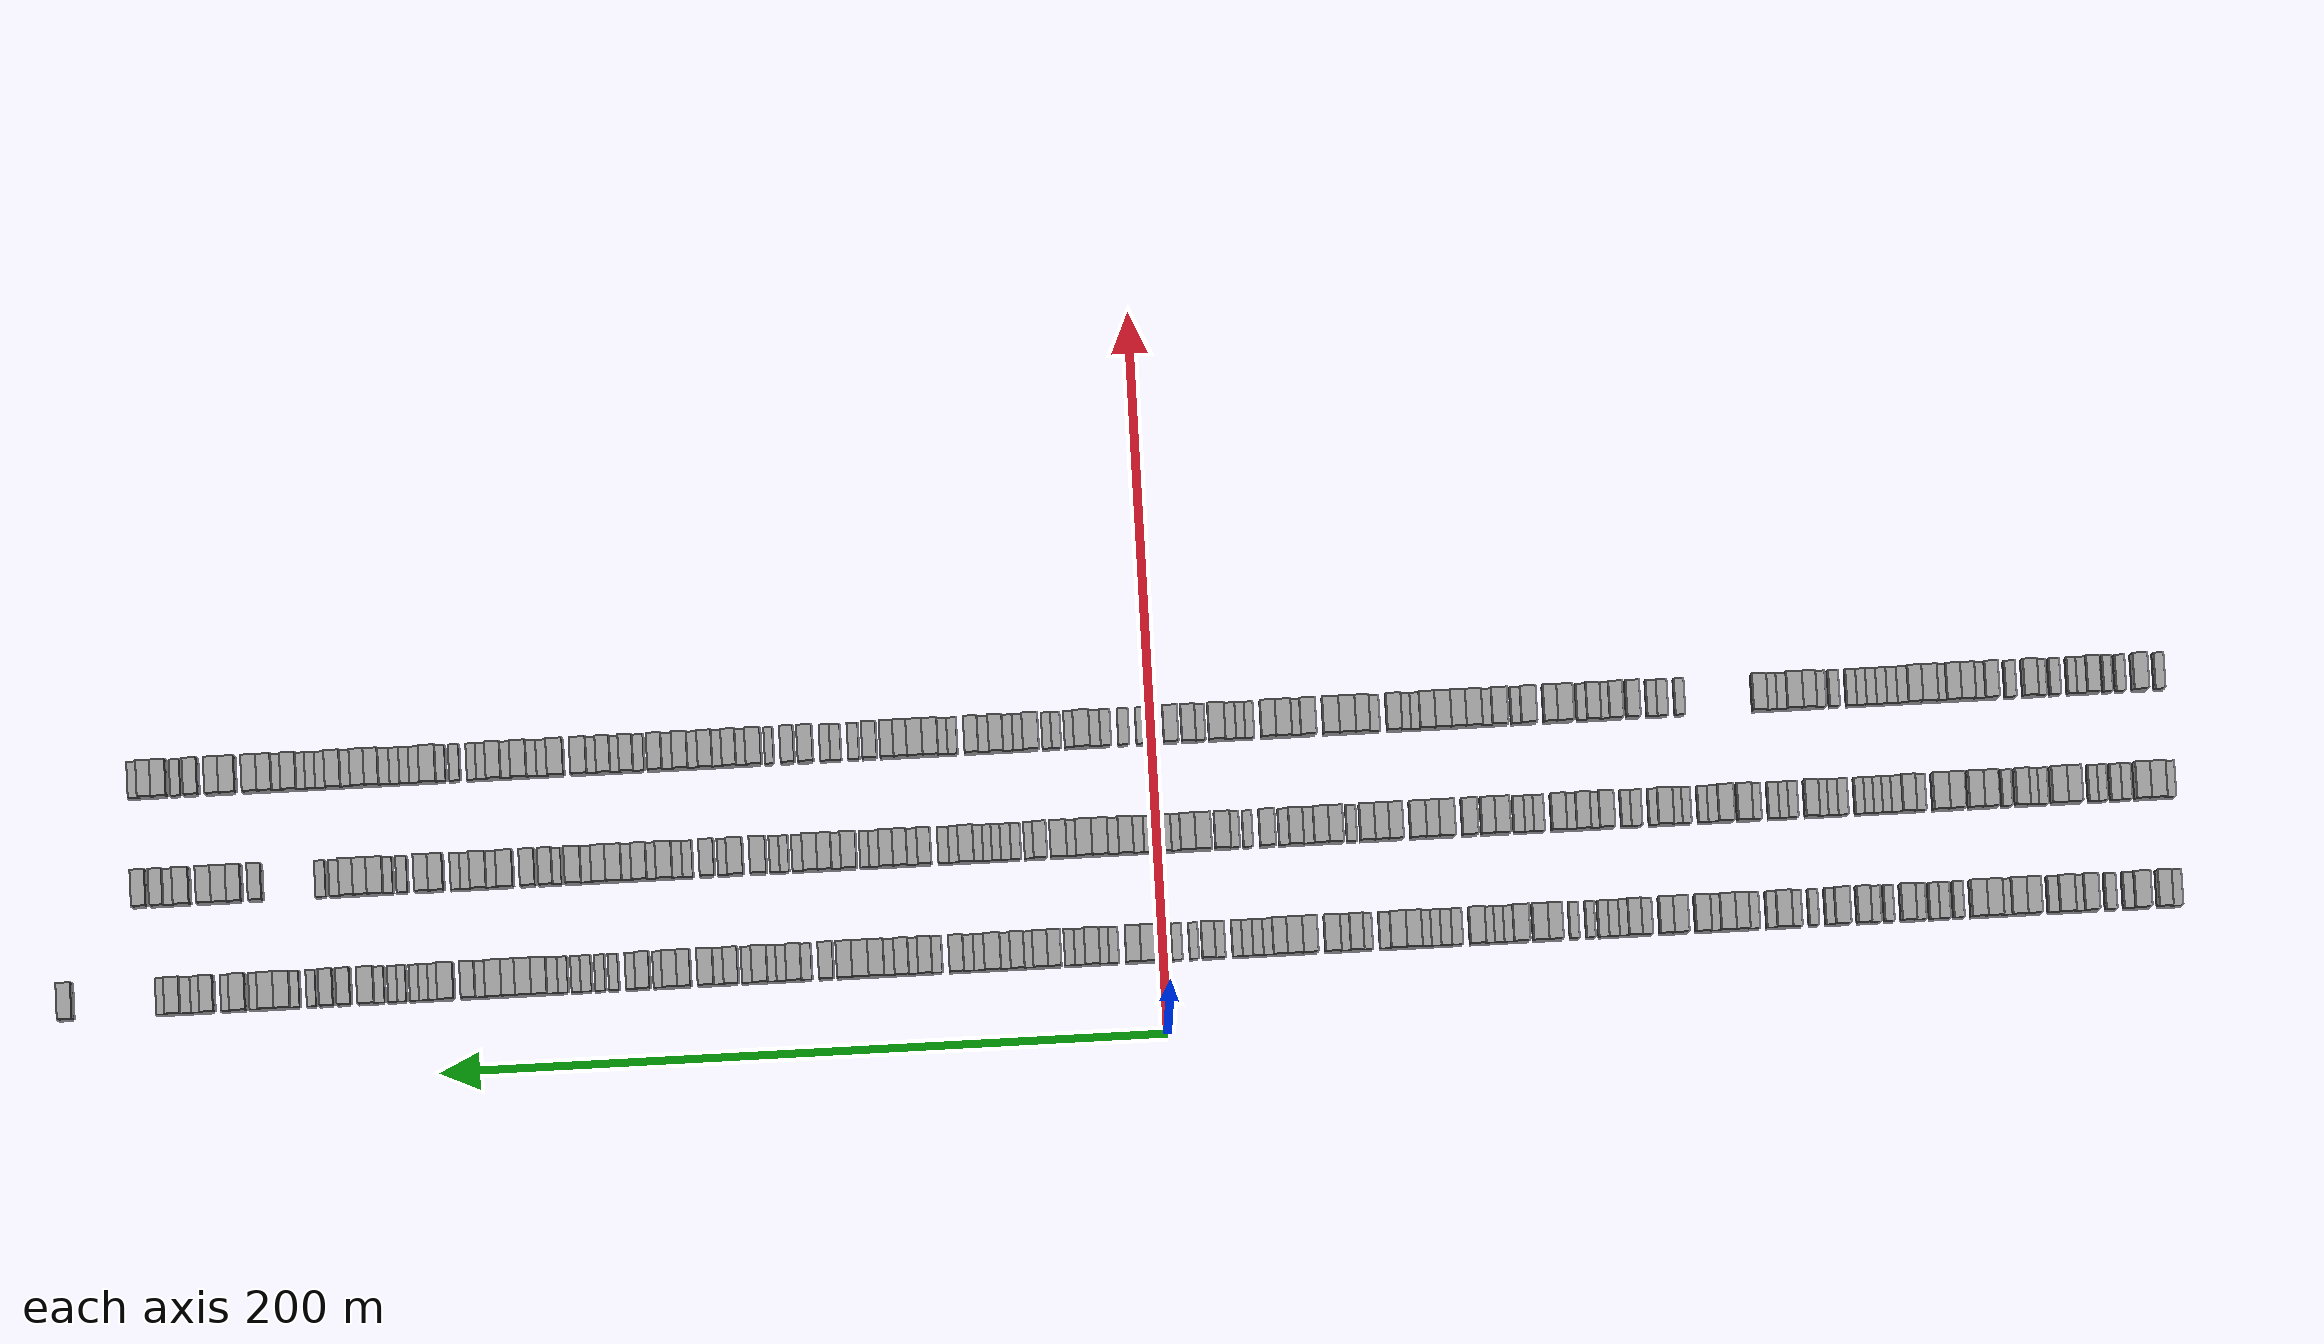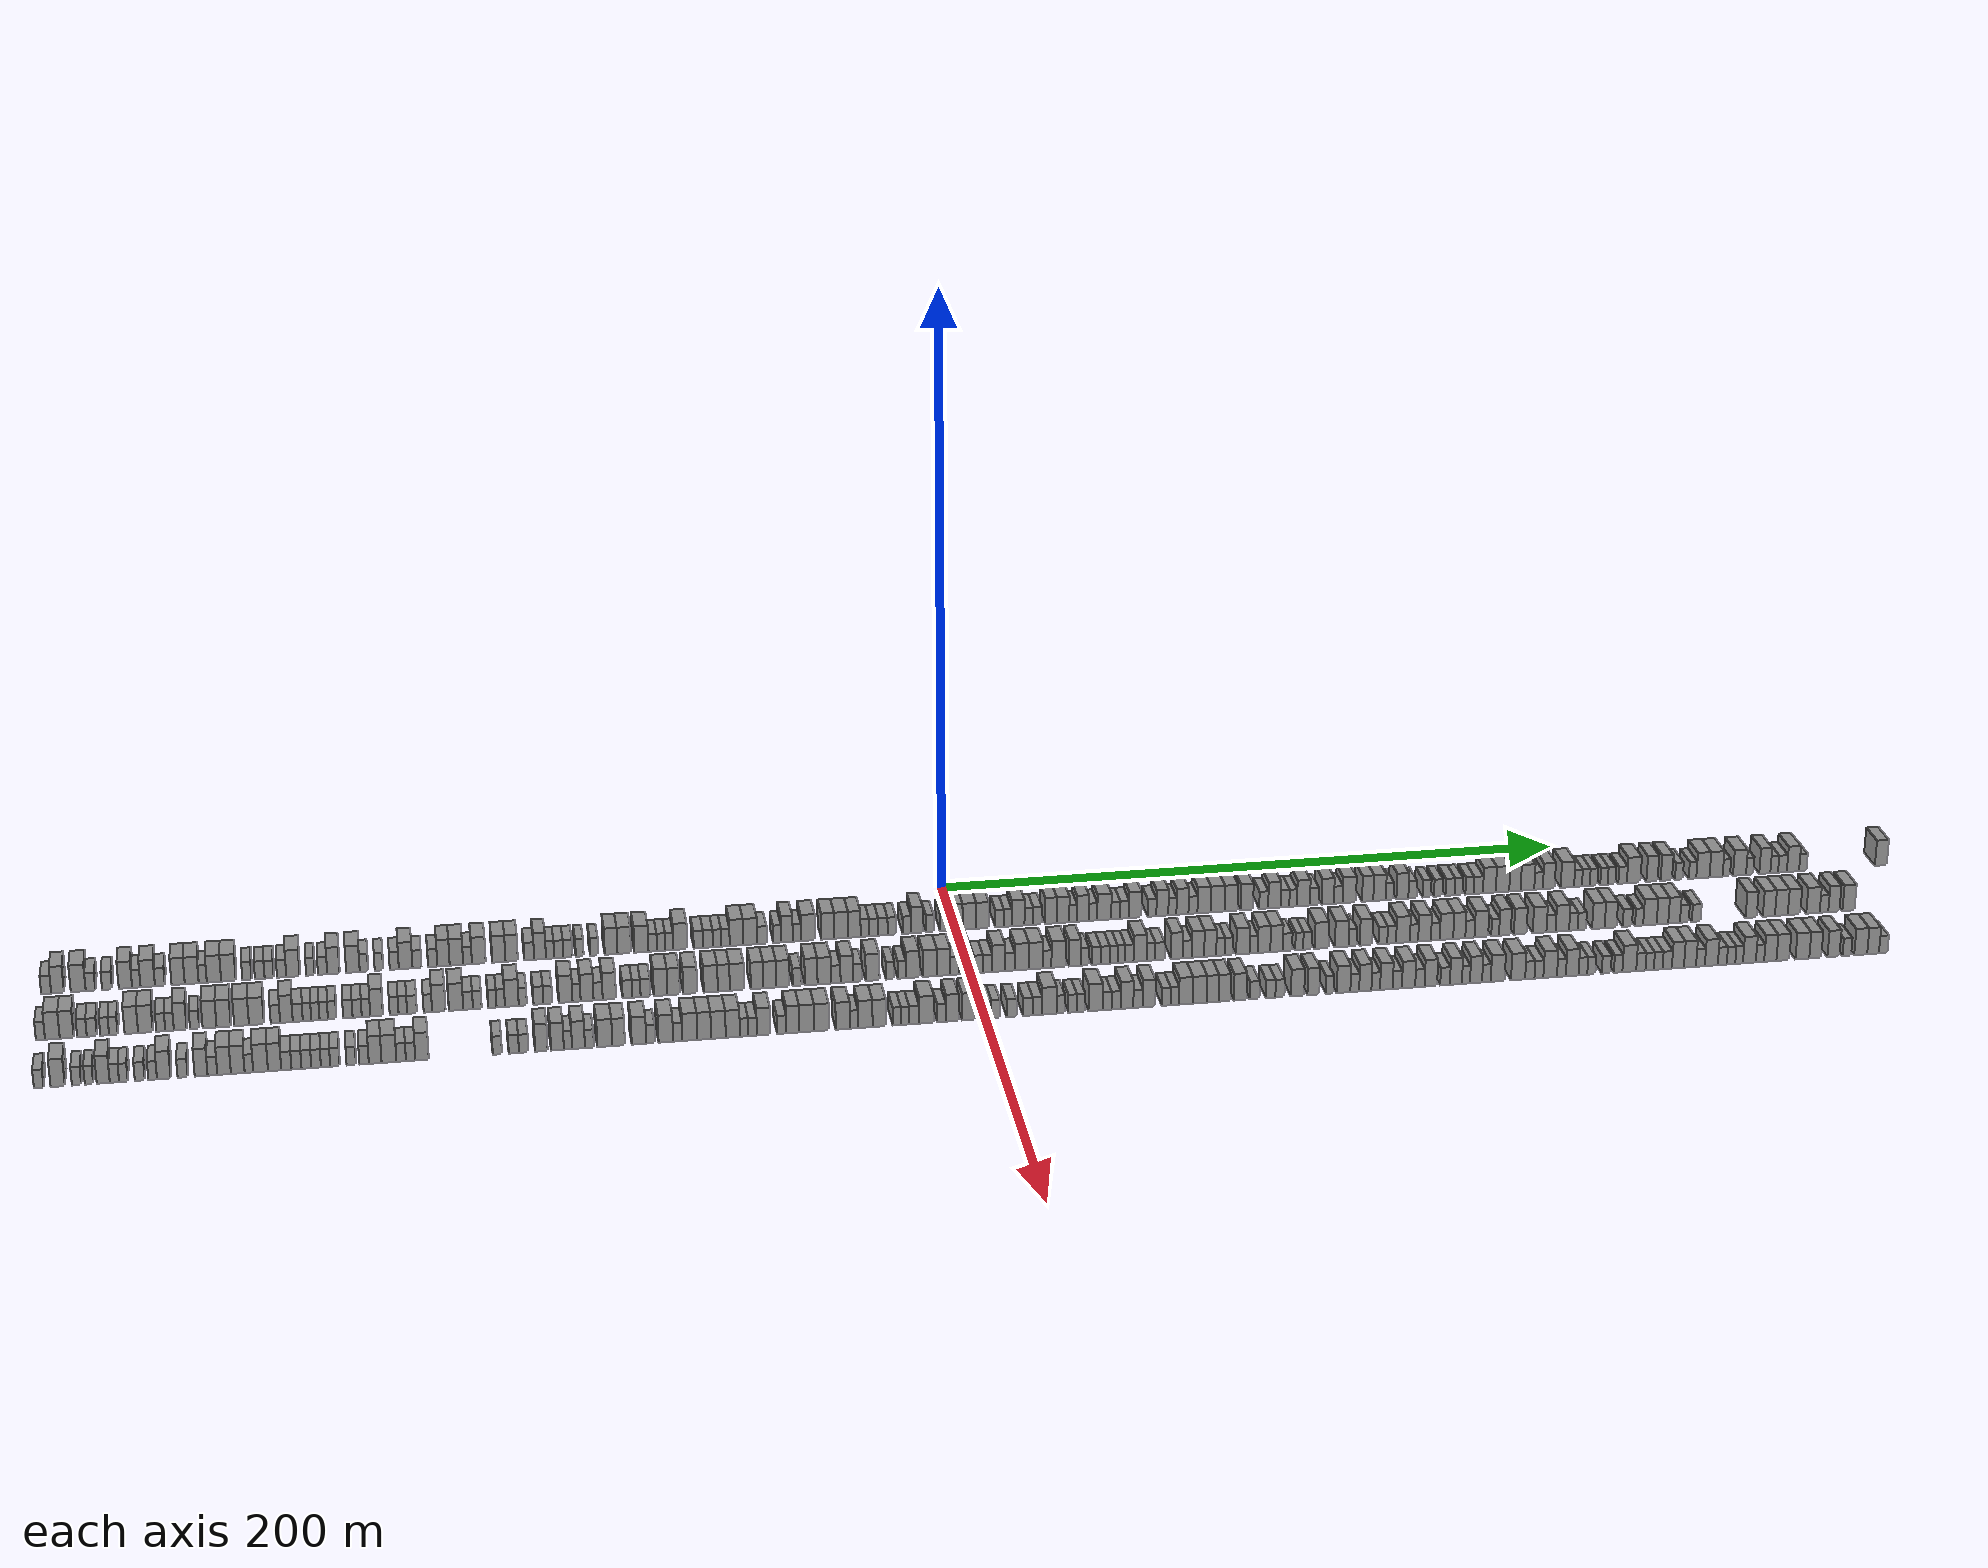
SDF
<sdf version="1.6">
 <world name="default">
  <scene>
   <sky><clouds><speed>12</speed></clouds></sky>
   <ambient>0.4 0.4 0.4 1</ambient>
   <background>0.7 0.7 0.7 1</background>
   <shadows>1</shadows>
  </scene>
  <gravity>0 0 -9.8066</gravity>
  <magnetic_field>6e-06 2.3e-05 -4.2e-05</magnetic_field>
  <physics default="0" name="default_physics" type="ode">
   <ode>
    <solver>
     <type>quick</type>
     <iters>10</iters>
     <sor>1.0</sor>
     <use_dynamic_moi_rescaling>0</use_dynamic_moi_rescaling>
    </solver>
    <constraints>
     <cfm>0</cfm>
     <erp>0.2</erp>
     <contact_max_correcting_vel>100</contact_max_correcting_vel>
     <contact_surface_layer>0.001</contact_surface_layer>
    </constraints>
   </ode>
   <max_step_size>0.004</max_step_size>
   <real_time_factor>1</real_time_factor>
   <real_time_update_rate>250</real_time_update_rate>
  </physics>
  <light name="sun" type="directional">
   <pose>0 0 10 0 0 0</pose>
   <diffuse>0.8 0.8 0.8 1</diffuse>
   <specular>0.2 0.2 0.2 1</specular>
   <attenuation>
    <range>1000</range>
    <constant>0.9</constant>
    <linear>0.01</linear>
    <quadratic>0.001</quadratic>
   </attenuation>
   <direction>-0.5 0.1 -0.9</direction>
  </light>
  <model name="building_1">
   <static>1</static>
   <pose>25.0000 -278.5188 0 0.000000 0.000000 0.000000</pose>
   <link name="link">
    <pose>0 0 3.00 0 0 0</pose>
    <collision name="collision"><geometry><box><size>10.0000 2.9624 6.0000</size></box></geometry></collision>
    <visual name="visual">
     <cast_shadows>0</cast_shadows>
     <geometry><box><size>10.0000 2.9624 6.0000</size></box></geometry>
     <material>
      <script>
       <uri>model://grey_wall/materials/scripts</uri>
       <uri>model://grey_wall/materials/textures</uri>
       <name>vrc/grey_wall</name>
      </script>
     </material>
    </visual>
   </link>
  </model>
  <model name="building_2">
   <static>1</static>
   <pose>25.0000 -275.1357 0 0.000000 0.000000 0.000000</pose>
   <link name="link">
    <pose>0 0 4.50 0 0 0</pose>
    <collision name="collision"><geometry><box><size>10.0000 3.8038 9.0000</size></box></geometry></collision>
    <visual name="visual">
     <cast_shadows>0</cast_shadows>
     <geometry><box><size>10.0000 3.8038 9.0000</size></box></geometry>
     <material>
      <script>
       <uri>model://grey_wall/materials/scripts</uri>
       <uri>model://grey_wall/materials/textures</uri>
       <name>vrc/grey_wall</name>
      </script>
     </material>
    </visual>
   </link>
  </model>
  <model name="building_3">
   <static>1</static>
   <pose>25.0000 -269.0056 0 0.000000 0.000000 0.000000</pose>
   <link name="link">
    <pose>0 0 4.50 0 0 0</pose>
    <collision name="collision"><geometry><box><size>10.0000 4.4563 9.0000</size></box></geometry></collision>
    <visual name="visual">
     <cast_shadows>0</cast_shadows>
     <geometry><box><size>10.0000 4.4563 9.0000</size></box></geometry>
     <material>
      <script>
       <uri>model://grey_wall/materials/scripts</uri>
       <uri>model://grey_wall/materials/textures</uri>
       <name>vrc/grey_wall</name>
      </script>
     </material>
    </visual>
   </link>
  </model>
  <model name="building_4">
   <static>1</static>
   <pose>25.0000 -265.3412 0 0.000000 0.000000 0.000000</pose>
   <link name="link">
    <pose>0 0 3.00 0 0 0</pose>
    <collision name="collision"><geometry><box><size>10.0000 2.8724 6.0000</size></box></geometry></collision>
    <visual name="visual">
     <cast_shadows>0</cast_shadows>
     <geometry><box><size>10.0000 2.8724 6.0000</size></box></geometry>
     <material>
      <script>
       <uri>model://grey_wall/materials/scripts</uri>
       <uri>model://grey_wall/materials/textures</uri>
       <name>vrc/grey_wall</name>
      </script>
     </material>
    </visual>
   </link>
  </model>
  <model name="building_5">
   <static>1</static>
   <pose>25.0000 -260.4188 0 0.000000 0.000000 0.000000</pose>
   <link name="link">
    <pose>0 0 3.00 0 0 0</pose>
    <collision name="collision"><geometry><box><size>10.0000 2.9724 6.0000</size></box></geometry></collision>
    <visual name="visual">
     <cast_shadows>0</cast_shadows>
     <geometry><box><size>10.0000 2.9724 6.0000</size></box></geometry>
     <material>
      <script>
       <uri>model://grey_wall/materials/scripts</uri>
       <uri>model://grey_wall/materials/textures</uri>
       <name>vrc/grey_wall</name>
      </script>
     </material>
    </visual>
   </link>
  </model>
  <model name="building_6">
   <static>1</static>
   <pose>25.0000 -254.9348 0 0.000000 0.000000 0.000000</pose>
   <link name="link">
    <pose>0 0 4.50 0 0 0</pose>
    <collision name="collision"><geometry><box><size>10.0000 3.9955 9.0000</size></box></geometry></collision>
    <visual name="visual">
     <cast_shadows>0</cast_shadows>
     <geometry><box><size>10.0000 3.9955 9.0000</size></box></geometry>
     <material>
      <script>
       <uri>model://grey_wall/materials/scripts</uri>
       <uri>model://grey_wall/materials/textures</uri>
       <name>vrc/grey_wall</name>
      </script>
     </material>
    </visual>
   </link>
  </model>
  <model name="building_7">
   <static>1</static>
   <pose>25.0000 -251.6873 0 0.000000 0.000000 0.000000</pose>
   <link name="link">
    <pose>0 0 3.00 0 0 0</pose>
    <collision name="collision"><geometry><box><size>10.0000 2.4995 6.0000</size></box></geometry></collision>
    <visual name="visual">
     <cast_shadows>0</cast_shadows>
     <geometry><box><size>10.0000 2.4995 6.0000</size></box></geometry>
     <material>
      <script>
       <uri>model://grey_wall/materials/scripts</uri>
       <uri>model://grey_wall/materials/textures</uri>
       <name>vrc/grey_wall</name>
      </script>
     </material>
    </visual>
   </link>
  </model>
  <model name="building_8">
   <static>1</static>
   <pose>25.0000 -248.2750 0 0.000000 0.000000 0.000000</pose>
   <link name="link">
    <pose>0 0 4.50 0 0 0</pose>
    <collision name="collision"><geometry><box><size>10.0000 4.3251 9.0000</size></box></geometry></collision>
    <visual name="visual">
     <cast_shadows>0</cast_shadows>
     <geometry><box><size>10.0000 4.3251 9.0000</size></box></geometry>
     <material>
      <script>
       <uri>model://grey_wall/materials/scripts</uri>
       <uri>model://grey_wall/materials/textures</uri>
       <name>vrc/grey_wall</name>
      </script>
     </material>
    </visual>
   </link>
  </model>
  <model name="building_9">
   <static>1</static>
   <pose>25.0000 -244.6391 0 0.000000 0.000000 0.000000</pose>
   <link name="link">
    <pose>0 0 3.00 0 0 0</pose>
    <collision name="collision"><geometry><box><size>10.0000 2.9468 6.0000</size></box></geometry></collision>
    <visual name="visual">
     <cast_shadows>0</cast_shadows>
     <geometry><box><size>10.0000 2.9468 6.0000</size></box></geometry>
     <material>
      <script>
       <uri>model://grey_wall/materials/scripts</uri>
       <uri>model://grey_wall/materials/textures</uri>
       <name>vrc/grey_wall</name>
      </script>
     </material>
    </visual>
   </link>
  </model>
  <model name="building_10">
   <static>1</static>
   <pose>25.0000 -239.1792 0 0.000000 0.000000 0.000000</pose>
   <link name="link">
    <pose>0 0 4.50 0 0 0</pose>
    <collision name="collision"><geometry><box><size>10.0000 3.9728 9.0000</size></box></geometry></collision>
    <visual name="visual">
     <cast_shadows>0</cast_shadows>
     <geometry><box><size>10.0000 3.9728 9.0000</size></box></geometry>
     <material>
      <script>
       <uri>model://grey_wall/materials/scripts</uri>
       <uri>model://grey_wall/materials/textures</uri>
       <name>vrc/grey_wall</name>
      </script>
     </material>
    </visual>
   </link>
  </model>
  <model name="building_11">
   <static>1</static>
   <pose>25.0000 -235.1122 0 0.000000 0.000000 0.000000</pose>
   <link name="link">
    <pose>0 0 4.50 0 0 0</pose>
    <collision name="collision"><geometry><box><size>10.0000 4.1613 9.0000</size></box></geometry></collision>
    <visual name="visual">
     <cast_shadows>0</cast_shadows>
     <geometry><box><size>10.0000 4.1613 9.0000</size></box></geometry>
     <material>
      <script>
       <uri>model://grey_wall/materials/scripts</uri>
       <uri>model://grey_wall/materials/textures</uri>
       <name>vrc/grey_wall</name>
      </script>
     </material>
    </visual>
   </link>
  </model>
  <model name="building_12">
   <static>1</static>
   <pose>25.0000 -231.8100 0 0.000000 0.000000 0.000000</pose>
   <link name="link">
    <pose>0 0 3.00 0 0 0</pose>
    <collision name="collision"><geometry><box><size>10.0000 2.4430 6.0000</size></box></geometry></collision>
    <visual name="visual">
     <cast_shadows>0</cast_shadows>
     <geometry><box><size>10.0000 2.4430 6.0000</size></box></geometry>
     <material>
      <script>
       <uri>model://grey_wall/materials/scripts</uri>
       <uri>model://grey_wall/materials/textures</uri>
       <name>vrc/grey_wall</name>
      </script>
     </material>
    </visual>
   </link>
  </model>
  <model name="building_13">
   <static>1</static>
   <pose>25.0000 -228.4294 0 0.000000 0.000000 0.000000</pose>
   <link name="link">
    <pose>0 0 4.50 0 0 0</pose>
    <collision name="collision"><geometry><box><size>10.0000 4.3182 9.0000</size></box></geometry></collision>
    <visual name="visual">
     <cast_shadows>0</cast_shadows>
     <geometry><box><size>10.0000 4.3182 9.0000</size></box></geometry>
     <material>
      <script>
       <uri>model://grey_wall/materials/scripts</uri>
       <uri>model://grey_wall/materials/textures</uri>
       <name>vrc/grey_wall</name>
      </script>
     </material>
    </visual>
   </link>
  </model>
  <model name="building_14">
   <static>1</static>
   <pose>25.0000 -224.0948 0 0.000000 0.000000 0.000000</pose>
   <link name="link">
    <pose>0 0 4.50 0 0 0</pose>
    <collision name="collision"><geometry><box><size>10.0000 4.3510 9.0000</size></box></geometry></collision>
    <visual name="visual">
     <cast_shadows>0</cast_shadows>
     <geometry><box><size>10.0000 4.3510 9.0000</size></box></geometry>
     <material>
      <script>
       <uri>model://grey_wall/materials/scripts</uri>
       <uri>model://grey_wall/materials/textures</uri>
       <name>vrc/grey_wall</name>
      </script>
     </material>
    </visual>
   </link>
  </model>
  <model name="building_15">
   <static>1</static>
   <pose>25.0000 -218.5361 0 0.000000 0.000000 0.000000</pose>
   <link name="link">
    <pose>0 0 3.00 0 0 0</pose>
    <collision name="collision"><geometry><box><size>10.0000 2.7663 6.0000</size></box></geometry></collision>
    <visual name="visual">
     <cast_shadows>0</cast_shadows>
     <geometry><box><size>10.0000 2.7663 6.0000</size></box></geometry>
     <material>
      <script>
       <uri>model://grey_wall/materials/scripts</uri>
       <uri>model://grey_wall/materials/textures</uri>
       <name>vrc/grey_wall</name>
      </script>
     </material>
    </visual>
   </link>
  </model>
  <model name="building_16">
   <static>1</static>
   <pose>25.0000 -214.6877 0 0.000000 0.000000 0.000000</pose>
   <link name="link">
    <pose>0 0 3.00 0 0 0</pose>
    <collision name="collision"><geometry><box><size>10.0000 2.9305 6.0000</size></box></geometry></collision>
    <visual name="visual">
     <cast_shadows>0</cast_shadows>
     <geometry><box><size>10.0000 2.9305 6.0000</size></box></geometry>
     <material>
      <script>
       <uri>model://grey_wall/materials/scripts</uri>
       <uri>model://grey_wall/materials/textures</uri>
       <name>vrc/grey_wall</name>
      </script>
     </material>
    </visual>
   </link>
  </model>
  <model name="building_17">
   <static>1</static>
   <pose>25.0000 -211.8568 0 0.000000 0.000000 0.000000</pose>
   <link name="link">
    <pose>0 0 3.00 0 0 0</pose>
    <collision name="collision"><geometry><box><size>10.0000 2.7313 6.0000</size></box></geometry></collision>
    <visual name="visual">
     <cast_shadows>0</cast_shadows>
     <geometry><box><size>10.0000 2.7313 6.0000</size></box></geometry>
     <material>
      <script>
       <uri>model://grey_wall/materials/scripts</uri>
       <uri>model://grey_wall/materials/textures</uri>
       <name>vrc/grey_wall</name>
      </script>
     </material>
    </visual>
   </link>
  </model>
  <model name="building_18">
   <static>1</static>
   <pose>25.0000 -208.0893 0 0.000000 0.000000 0.000000</pose>
   <link name="link">
    <pose>0 0 3.00 0 0 0</pose>
    <collision name="collision"><geometry><box><size>10.0000 2.8035 6.0000</size></box></geometry></collision>
    <visual name="visual">
     <cast_shadows>0</cast_shadows>
     <geometry><box><size>10.0000 2.8035 6.0000</size></box></geometry>
     <material>
      <script>
       <uri>model://grey_wall/materials/scripts</uri>
       <uri>model://grey_wall/materials/textures</uri>
       <name>vrc/grey_wall</name>
      </script>
     </material>
    </visual>
   </link>
  </model>
  <model name="building_19">
   <static>1</static>
   <pose>25.0000 -204.6888 0 0.000000 0.000000 0.000000</pose>
   <link name="link">
    <pose>0 0 4.50 0 0 0</pose>
    <collision name="collision"><geometry><box><size>10.0000 3.9975 9.0000</size></box></geometry></collision>
    <visual name="visual">
     <cast_shadows>0</cast_shadows>
     <geometry><box><size>10.0000 3.9975 9.0000</size></box></geometry>
     <material>
      <script>
       <uri>model://grey_wall/materials/scripts</uri>
       <uri>model://grey_wall/materials/textures</uri>
       <name>vrc/grey_wall</name>
      </script>
     </material>
    </visual>
   </link>
  </model>
  <model name="building_20">
   <static>1</static>
   <pose>25.0000 -199.4156 0 0.000000 0.000000 0.000000</pose>
   <link name="link">
    <pose>0 0 3.00 0 0 0</pose>
    <collision name="collision"><geometry><box><size>10.0000 2.5488 6.0000</size></box></geometry></collision>
    <visual name="visual">
     <cast_shadows>0</cast_shadows>
     <geometry><box><size>10.0000 2.5488 6.0000</size></box></geometry>
     <material>
      <script>
       <uri>model://grey_wall/materials/scripts</uri>
       <uri>model://grey_wall/materials/textures</uri>
       <name>vrc/grey_wall</name>
      </script>
     </material>
    </visual>
   </link>
  </model>
  <model name="building_21">
   <static>1</static>
   <pose>25.0000 -195.7328 0 0.000000 0.000000 0.000000</pose>
   <link name="link">
    <pose>0 0 3.00 0 0 0</pose>
    <collision name="collision"><geometry><box><size>10.0000 2.8169 6.0000</size></box></geometry></collision>
    <visual name="visual">
     <cast_shadows>0</cast_shadows>
     <geometry><box><size>10.0000 2.8169 6.0000</size></box></geometry>
     <material>
      <script>
       <uri>model://grey_wall/materials/scripts</uri>
       <uri>model://grey_wall/materials/textures</uri>
       <name>vrc/grey_wall</name>
      </script>
     </material>
    </visual>
   </link>
  </model>
  <model name="building_22">
   <static>1</static>
   <pose>25.0000 -192.4655 0 0.000000 0.000000 0.000000</pose>
   <link name="link">
    <pose>0 0 4.50 0 0 0</pose>
    <collision name="collision"><geometry><box><size>10.0000 3.7176 9.0000</size></box></geometry></collision>
    <visual name="visual">
     <cast_shadows>0</cast_shadows>
     <geometry><box><size>10.0000 3.7176 9.0000</size></box></geometry>
     <material>
      <script>
       <uri>model://grey_wall/materials/scripts</uri>
       <uri>model://grey_wall/materials/textures</uri>
       <name>vrc/grey_wall</name>
      </script>
     </material>
    </visual>
   </link>
  </model>
  <model name="building_23">
   <static>1</static>
   <pose>25.0000 -186.5539 0 0.000000 0.000000 0.000000</pose>
   <link name="link">
    <pose>0 0 4.50 0 0 0</pose>
    <collision name="collision"><geometry><box><size>10.0000 4.1057 9.0000</size></box></geometry></collision>
    <visual name="visual">
     <cast_shadows>0</cast_shadows>
     <geometry><box><size>10.0000 4.1057 9.0000</size></box></geometry>
     <material>
      <script>
       <uri>model://grey_wall/materials/scripts</uri>
       <uri>model://grey_wall/materials/textures</uri>
       <name>vrc/grey_wall</name>
      </script>
     </material>
    </visual>
   </link>
  </model>
  <model name="building_24">
   <static>1</static>
   <pose>25.0000 -183.2308 0 0.000000 0.000000 0.000000</pose>
   <link name="link">
    <pose>0 0 3.00 0 0 0</pose>
    <collision name="collision"><geometry><box><size>10.0000 2.5404 6.0000</size></box></geometry></collision>
    <visual name="visual">
     <cast_shadows>0</cast_shadows>
     <geometry><box><size>10.0000 2.5404 6.0000</size></box></geometry>
     <material>
      <script>
       <uri>model://grey_wall/materials/scripts</uri>
       <uri>model://grey_wall/materials/textures</uri>
       <name>vrc/grey_wall</name>
      </script>
     </material>
    </visual>
   </link>
  </model>
  <model name="building_25">
   <static>1</static>
   <pose>25.0000 -178.6758 0 0.000000 0.000000 0.000000</pose>
   <link name="link">
    <pose>0 0 3.00 0 0 0</pose>
    <collision name="collision"><geometry><box><size>10.0000 2.5698 6.0000</size></box></geometry></collision>
    <visual name="visual">
     <cast_shadows>0</cast_shadows>
     <geometry><box><size>10.0000 2.5698 6.0000</size></box></geometry>
     <material>
      <script>
       <uri>model://grey_wall/materials/scripts</uri>
       <uri>model://grey_wall/materials/textures</uri>
       <name>vrc/grey_wall</name>
      </script>
     </material>
    </visual>
   </link>
  </model>
  <model name="building_26">
   <static>1</static>
   <pose>25.0000 -174.0191 0 0.000000 0.000000 0.000000</pose>
   <link name="link">
    <pose>0 0 3.00 0 0 0</pose>
    <collision name="collision"><geometry><box><size>10.0000 2.7436 6.0000</size></box></geometry></collision>
    <visual name="visual">
     <cast_shadows>0</cast_shadows>
     <geometry><box><size>10.0000 2.7436 6.0000</size></box></geometry>
     <material>
      <script>
       <uri>model://grey_wall/materials/scripts</uri>
       <uri>model://grey_wall/materials/textures</uri>
       <name>vrc/grey_wall</name>
      </script>
     </material>
    </visual>
   </link>
  </model>
  <model name="building_27">
   <static>1</static>
   <pose>25.0000 -170.5623 0 0.000000 0.000000 0.000000</pose>
   <link name="link">
    <pose>0 0 4.50 0 0 0</pose>
    <collision name="collision"><geometry><box><size>10.0000 4.1702 9.0000</size></box></geometry></collision>
    <visual name="visual">
     <cast_shadows>0</cast_shadows>
     <geometry><box><size>10.0000 4.1702 9.0000</size></box></geometry>
     <material>
      <script>
       <uri>model://grey_wall/materials/scripts</uri>
       <uri>model://grey_wall/materials/textures</uri>
       <name>vrc/grey_wall</name>
      </script>
     </material>
    </visual>
   </link>
  </model>
  <model name="building_28">
   <static>1</static>
   <pose>25.0000 -167.1116 0 0.000000 0.000000 0.000000</pose>
   <link name="link">
    <pose>0 0 3.00 0 0 0</pose>
    <collision name="collision"><geometry><box><size>10.0000 2.7311 6.0000</size></box></geometry></collision>
    <visual name="visual">
     <cast_shadows>0</cast_shadows>
     <geometry><box><size>10.0000 2.7311 6.0000</size></box></geometry>
     <material>
      <script>
       <uri>model://grey_wall/materials/scripts</uri>
       <uri>model://grey_wall/materials/textures</uri>
       <name>vrc/grey_wall</name>
      </script>
     </material>
    </visual>
   </link>
  </model>
  <model name="building_29">
   <static>1</static>
   <pose>25.0000 -162.3323 0 0.000000 0.000000 0.000000</pose>
   <link name="link">
    <pose>0 0 3.00 0 0 0</pose>
    <collision name="collision"><geometry><box><size>10.0000 2.8275 6.0000</size></box></geometry></collision>
    <visual name="visual">
     <cast_shadows>0</cast_shadows>
     <geometry><box><size>10.0000 2.8275 6.0000</size></box></geometry>
     <material>
      <script>
       <uri>model://grey_wall/materials/scripts</uri>
       <uri>model://grey_wall/materials/textures</uri>
       <name>vrc/grey_wall</name>
      </script>
     </material>
    </visual>
   </link>
  </model>
  <model name="building_30">
   <static>1</static>
   <pose>25.0000 -159.0452 0 0.000000 0.000000 0.000000</pose>
   <link name="link">
    <pose>0 0 4.50 0 0 0</pose>
    <collision name="collision"><geometry><box><size>10.0000 3.7467 9.0000</size></box></geometry></collision>
    <visual name="visual">
     <cast_shadows>0</cast_shadows>
     <geometry><box><size>10.0000 3.7467 9.0000</size></box></geometry>
     <material>
      <script>
       <uri>model://grey_wall/materials/scripts</uri>
       <uri>model://grey_wall/materials/textures</uri>
       <name>vrc/grey_wall</name>
      </script>
     </material>
    </visual>
   </link>
  </model>
  <model name="building_31">
   <static>1</static>
   <pose>25.0000 -155.1113 0 0.000000 0.000000 0.000000</pose>
   <link name="link">
    <pose>0 0 4.50 0 0 0</pose>
    <collision name="collision"><geometry><box><size>10.0000 4.1211 9.0000</size></box></geometry></collision>
    <visual name="visual">
     <cast_shadows>0</cast_shadows>
     <geometry><box><size>10.0000 4.1211 9.0000</size></box></geometry>
     <material>
      <script>
       <uri>model://grey_wall/materials/scripts</uri>
       <uri>model://grey_wall/materials/textures</uri>
       <name>vrc/grey_wall</name>
      </script>
     </material>
    </visual>
   </link>
  </model>
  <model name="building_32">
   <static>1</static>
   <pose>25.0000 -151.7106 0 0.000000 0.000000 0.000000</pose>
   <link name="link">
    <pose>0 0 3.00 0 0 0</pose>
    <collision name="collision"><geometry><box><size>10.0000 2.6804 6.0000</size></box></geometry></collision>
    <visual name="visual">
     <cast_shadows>0</cast_shadows>
     <geometry><box><size>10.0000 2.6804 6.0000</size></box></geometry>
     <material>
      <script>
       <uri>model://grey_wall/materials/scripts</uri>
       <uri>model://grey_wall/materials/textures</uri>
       <name>vrc/grey_wall</name>
      </script>
     </material>
    </visual>
   </link>
  </model>
  <model name="building_33">
   <static>1</static>
   <pose>25.0000 -148.2665 0 0.000000 0.000000 0.000000</pose>
   <link name="link">
    <pose>0 0 4.50 0 0 0</pose>
    <collision name="collision"><geometry><box><size>10.0000 4.2079 9.0000</size></box></geometry></collision>
    <visual name="visual">
     <cast_shadows>0</cast_shadows>
     <geometry><box><size>10.0000 4.2079 9.0000</size></box></geometry>
     <material>
      <script>
       <uri>model://grey_wall/materials/scripts</uri>
       <uri>model://grey_wall/materials/textures</uri>
       <name>vrc/grey_wall</name>
      </script>
     </material>
    </visual>
   </link>
  </model>
  <model name="building_34">
   <static>1</static>
   <pose>25.0000 -142.1418 0 0.000000 0.000000 0.000000</pose>
   <link name="link">
    <pose>0 0 4.50 0 0 0</pose>
    <collision name="collision"><geometry><box><size>10.0000 4.0413 9.0000</size></box></geometry></collision>
    <visual name="visual">
     <cast_shadows>0</cast_shadows>
     <geometry><box><size>10.0000 4.0413 9.0000</size></box></geometry>
     <material>
      <script>
       <uri>model://grey_wall/materials/scripts</uri>
       <uri>model://grey_wall/materials/textures</uri>
       <name>vrc/grey_wall</name>
      </script>
     </material>
    </visual>
   </link>
  </model>
  <model name="building_35">
   <static>1</static>
   <pose>25.0000 -138.2296 0 0.000000 0.000000 0.000000</pose>
   <link name="link">
    <pose>0 0 4.50 0 0 0</pose>
    <collision name="collision"><geometry><box><size>10.0000 3.7831 9.0000</size></box></geometry></collision>
    <visual name="visual">
     <cast_shadows>0</cast_shadows>
     <geometry><box><size>10.0000 3.7831 9.0000</size></box></geometry>
     <material>
      <script>
       <uri>model://grey_wall/materials/scripts</uri>
       <uri>model://grey_wall/materials/textures</uri>
       <name>vrc/grey_wall</name>
      </script>
     </material>
    </visual>
   </link>
  </model>
  <model name="building_36">
   <static>1</static>
   <pose>25.0000 -132.8399 0 0.000000 0.000000 0.000000</pose>
   <link name="link">
    <pose>0 0 3.00 0 0 0</pose>
    <collision name="collision"><geometry><box><size>10.0000 2.9964 6.0000</size></box></geometry></collision>
    <visual name="visual">
     <cast_shadows>0</cast_shadows>
     <geometry><box><size>10.0000 2.9964 6.0000</size></box></geometry>
     <material>
      <script>
       <uri>model://grey_wall/materials/scripts</uri>
       <uri>model://grey_wall/materials/textures</uri>
       <name>vrc/grey_wall</name>
      </script>
     </material>
    </visual>
   </link>
  </model>
  <model name="building_37">
   <static>1</static>
   <pose>25.0000 -129.5317 0 0.000000 0.000000 0.000000</pose>
   <link name="link">
    <pose>0 0 4.50 0 0 0</pose>
    <collision name="collision"><geometry><box><size>10.0000 3.6201 9.0000</size></box></geometry></collision>
    <visual name="visual">
     <cast_shadows>0</cast_shadows>
     <geometry><box><size>10.0000 3.6201 9.0000</size></box></geometry>
     <material>
      <script>
       <uri>model://grey_wall/materials/scripts</uri>
       <uri>model://grey_wall/materials/textures</uri>
       <name>vrc/grey_wall</name>
      </script>
     </material>
    </visual>
   </link>
  </model>
  <model name="building_38">
   <static>1</static>
   <pose>25.0000 -126.4576 0 0.000000 0.000000 0.000000</pose>
   <link name="link">
    <pose>0 0 3.00 0 0 0</pose>
    <collision name="collision"><geometry><box><size>10.0000 2.5280 6.0000</size></box></geometry></collision>
    <visual name="visual">
     <cast_shadows>0</cast_shadows>
     <geometry><box><size>10.0000 2.5280 6.0000</size></box></geometry>
     <material>
      <script>
       <uri>model://grey_wall/materials/scripts</uri>
       <uri>model://grey_wall/materials/textures</uri>
       <name>vrc/grey_wall</name>
      </script>
     </material>
    </visual>
   </link>
  </model>
  <model name="building_39">
   <static>1</static>
   <pose>25.0000 -123.7760 0 0.000000 0.000000 0.000000</pose>
   <link name="link">
    <pose>0 0 3.00 0 0 0</pose>
    <collision name="collision"><geometry><box><size>10.0000 2.8352 6.0000</size></box></geometry></collision>
    <visual name="visual">
     <cast_shadows>0</cast_shadows>
     <geometry><box><size>10.0000 2.8352 6.0000</size></box></geometry>
     <material>
      <script>
       <uri>model://grey_wall/materials/scripts</uri>
       <uri>model://grey_wall/materials/textures</uri>
       <name>vrc/grey_wall</name>
      </script>
     </material>
    </visual>
   </link>
  </model>
  <model name="building_40">
   <static>1</static>
   <pose>25.0000 -120.9576 0 0.000000 0.000000 0.000000</pose>
   <link name="link">
    <pose>0 0 3.00 0 0 0</pose>
    <collision name="collision"><geometry><box><size>10.0000 2.8017 6.0000</size></box></geometry></collision>
    <visual name="visual">
     <cast_shadows>0</cast_shadows>
     <geometry><box><size>10.0000 2.8017 6.0000</size></box></geometry>
     <material>
      <script>
       <uri>model://grey_wall/materials/scripts</uri>
       <uri>model://grey_wall/materials/textures</uri>
       <name>vrc/grey_wall</name>
      </script>
     </material>
    </visual>
   </link>
  </model>
  <model name="building_41">
   <static>1</static>
   <pose>25.0000 -117.3510 0 0.000000 0.000000 0.000000</pose>
   <link name="link">
    <pose>0 0 3.00 0 0 0</pose>
    <collision name="collision"><geometry><box><size>10.0000 2.4115 6.0000</size></box></geometry></collision>
    <visual name="visual">
     <cast_shadows>0</cast_shadows>
     <geometry><box><size>10.0000 2.4115 6.0000</size></box></geometry>
     <material>
      <script>
       <uri>model://grey_wall/materials/scripts</uri>
       <uri>model://grey_wall/materials/textures</uri>
       <name>vrc/grey_wall</name>
      </script>
     </material>
    </visual>
   </link>
  </model>
  <model name="building_42">
   <static>1</static>
   <pose>25.0000 -112.8943 0 0.000000 0.000000 0.000000</pose>
   <link name="link">
    <pose>0 0 3.00 0 0 0</pose>
    <collision name="collision"><geometry><box><size>10.0000 2.5019 6.0000</size></box></geometry></collision>
    <visual name="visual">
     <cast_shadows>0</cast_shadows>
     <geometry><box><size>10.0000 2.5019 6.0000</size></box></geometry>
     <material>
      <script>
       <uri>model://grey_wall/materials/scripts</uri>
       <uri>model://grey_wall/materials/textures</uri>
       <name>vrc/grey_wall</name>
      </script>
     </material>
    </visual>
   </link>
  </model>
  <model name="building_43">
   <static>1</static>
   <pose>25.0000 -107.6780 0 0.000000 0.000000 0.000000</pose>
   <link name="link">
    <pose>0 0 4.50 0 0 0</pose>
    <collision name="collision"><geometry><box><size>10.0000 3.9306 9.0000</size></box></geometry></collision>
    <visual name="visual">
     <cast_shadows>0</cast_shadows>
     <geometry><box><size>10.0000 3.9306 9.0000</size></box></geometry>
     <material>
      <script>
       <uri>model://grey_wall/materials/scripts</uri>
       <uri>model://grey_wall/materials/textures</uri>
       <name>vrc/grey_wall</name>
      </script>
     </material>
    </visual>
   </link>
  </model>
  <model name="building_44">
   <static>1</static>
   <pose>25.0000 -103.6132 0 0.000000 0.000000 0.000000</pose>
   <link name="link">
    <pose>0 0 4.50 0 0 0</pose>
    <collision name="collision"><geometry><box><size>10.0000 4.1989 9.0000</size></box></geometry></collision>
    <visual name="visual">
     <cast_shadows>0</cast_shadows>
     <geometry><box><size>10.0000 4.1989 9.0000</size></box></geometry>
     <material>
      <script>
       <uri>model://grey_wall/materials/scripts</uri>
       <uri>model://grey_wall/materials/textures</uri>
       <name>vrc/grey_wall</name>
      </script>
     </material>
    </visual>
   </link>
  </model>
  <model name="building_45">
   <static>1</static>
   <pose>25.0000 -98.3265 0 0.000000 0.000000 0.000000</pose>
   <link name="link">
    <pose>0 0 4.50 0 0 0</pose>
    <collision name="collision"><geometry><box><size>10.0000 4.3746 9.0000</size></box></geometry></collision>
    <visual name="visual">
     <cast_shadows>0</cast_shadows>
     <geometry><box><size>10.0000 4.3746 9.0000</size></box></geometry>
     <material>
      <script>
       <uri>model://grey_wall/materials/scripts</uri>
       <uri>model://grey_wall/materials/textures</uri>
       <name>vrc/grey_wall</name>
      </script>
     </material>
    </visual>
   </link>
  </model>
  <model name="building_46">
   <static>1</static>
   <pose>25.0000 -94.8186 0 0.000000 0.000000 0.000000</pose>
   <link name="link">
    <pose>0 0 3.00 0 0 0</pose>
    <collision name="collision"><geometry><box><size>10.0000 2.6411 6.0000</size></box></geometry></collision>
    <visual name="visual">
     <cast_shadows>0</cast_shadows>
     <geometry><box><size>10.0000 2.6411 6.0000</size></box></geometry>
     <material>
      <script>
       <uri>model://grey_wall/materials/scripts</uri>
       <uri>model://grey_wall/materials/textures</uri>
       <name>vrc/grey_wall</name>
      </script>
     </material>
    </visual>
   </link>
  </model>
  <model name="building_47">
   <static>1</static>
   <pose>25.0000 -92.1925 0 0.000000 0.000000 0.000000</pose>
   <link name="link">
    <pose>0 0 3.00 0 0 0</pose>
    <collision name="collision"><geometry><box><size>10.0000 2.6111 6.0000</size></box></geometry></collision>
    <visual name="visual">
     <cast_shadows>0</cast_shadows>
     <geometry><box><size>10.0000 2.6111 6.0000</size></box></geometry>
     <material>
      <script>
       <uri>model://grey_wall/materials/scripts</uri>
       <uri>model://grey_wall/materials/textures</uri>
       <name>vrc/grey_wall</name>
      </script>
     </material>
    </visual>
   </link>
  </model>
  <model name="building_48">
   <static>1</static>
   <pose>25.0000 -89.6602 0 0.000000 0.000000 0.000000</pose>
   <link name="link">
    <pose>0 0 3.00 0 0 0</pose>
    <collision name="collision"><geometry><box><size>10.0000 2.4534 6.0000</size></box></geometry></collision>
    <visual name="visual">
     <cast_shadows>0</cast_shadows>
     <geometry><box><size>10.0000 2.4534 6.0000</size></box></geometry>
     <material>
      <script>
       <uri>model://grey_wall/materials/scripts</uri>
       <uri>model://grey_wall/materials/textures</uri>
       <name>vrc/grey_wall</name>
      </script>
     </material>
    </visual>
   </link>
  </model>
  <model name="building_49">
   <static>1</static>
   <pose>25.0000 -86.2906 0 0.000000 0.000000 0.000000</pose>
   <link name="link">
    <pose>0 0 4.50 0 0 0</pose>
    <collision name="collision"><geometry><box><size>10.0000 4.2859 9.0000</size></box></geometry></collision>
    <visual name="visual">
     <cast_shadows>0</cast_shadows>
     <geometry><box><size>10.0000 4.2859 9.0000</size></box></geometry>
     <material>
      <script>
       <uri>model://grey_wall/materials/scripts</uri>
       <uri>model://grey_wall/materials/textures</uri>
       <name>vrc/grey_wall</name>
      </script>
     </material>
    </visual>
   </link>
  </model>
  <model name="building_50">
   <static>1</static>
   <pose>25.0000 -80.6596 0 0.000000 0.000000 0.000000</pose>
   <link name="link">
    <pose>0 0 3.00 0 0 0</pose>
    <collision name="collision"><geometry><box><size>10.0000 2.9761 6.0000</size></box></geometry></collision>
    <visual name="visual">
     <cast_shadows>0</cast_shadows>
     <geometry><box><size>10.0000 2.9761 6.0000</size></box></geometry>
     <material>
      <script>
       <uri>model://grey_wall/materials/scripts</uri>
       <uri>model://grey_wall/materials/textures</uri>
       <name>vrc/grey_wall</name>
      </script>
     </material>
    </visual>
   </link>
  </model>
  <model name="building_51">
   <static>1</static>
   <pose>25.0000 -77.6832 0 0.000000 0.000000 0.000000</pose>
   <link name="link">
    <pose>0 0 3.00 0 0 0</pose>
    <collision name="collision"><geometry><box><size>10.0000 2.9765 6.0000</size></box></geometry></collision>
    <visual name="visual">
     <cast_shadows>0</cast_shadows>
     <geometry><box><size>10.0000 2.9765 6.0000</size></box></geometry>
     <material>
      <script>
       <uri>model://grey_wall/materials/scripts</uri>
       <uri>model://grey_wall/materials/textures</uri>
       <name>vrc/grey_wall</name>
      </script>
     </material>
    </visual>
   </link>
  </model>
  <model name="building_52">
   <static>1</static>
   <pose>25.0000 -74.8702 0 0.000000 0.000000 0.000000</pose>
   <link name="link">
    <pose>0 0 3.00 0 0 0</pose>
    <collision name="collision"><geometry><box><size>10.0000 2.6497 6.0000</size></box></geometry></collision>
    <visual name="visual">
     <cast_shadows>0</cast_shadows>
     <geometry><box><size>10.0000 2.6497 6.0000</size></box></geometry>
     <material>
      <script>
       <uri>model://grey_wall/materials/scripts</uri>
       <uri>model://grey_wall/materials/textures</uri>
       <name>vrc/grey_wall</name>
      </script>
     </material>
    </visual>
   </link>
  </model>
  <model name="building_53">
   <static>1</static>
   <pose>25.0000 -72.2562 0 0.000000 0.000000 0.000000</pose>
   <link name="link">
    <pose>0 0 3.00 0 0 0</pose>
    <collision name="collision"><geometry><box><size>10.0000 2.5783 6.0000</size></box></geometry></collision>
    <visual name="visual">
     <cast_shadows>0</cast_shadows>
     <geometry><box><size>10.0000 2.5783 6.0000</size></box></geometry>
     <material>
      <script>
       <uri>model://grey_wall/materials/scripts</uri>
       <uri>model://grey_wall/materials/textures</uri>
       <name>vrc/grey_wall</name>
      </script>
     </material>
    </visual>
   </link>
  </model>
  <model name="building_54">
   <static>1</static>
   <pose>25.0000 -68.8638 0 0.000000 0.000000 0.000000</pose>
   <link name="link">
    <pose>0 0 4.50 0 0 0</pose>
    <collision name="collision"><geometry><box><size>10.0000 4.2063 9.0000</size></box></geometry></collision>
    <visual name="visual">
     <cast_shadows>0</cast_shadows>
     <geometry><box><size>10.0000 4.2063 9.0000</size></box></geometry>
     <material>
      <script>
       <uri>model://grey_wall/materials/scripts</uri>
       <uri>model://grey_wall/materials/textures</uri>
       <name>vrc/grey_wall</name>
      </script>
     </material>
    </visual>
   </link>
  </model>
  <model name="building_55">
   <static>1</static>
   <pose>25.0000 -64.5815 0 0.000000 0.000000 0.000000</pose>
   <link name="link">
    <pose>0 0 4.50 0 0 0</pose>
    <collision name="collision"><geometry><box><size>10.0000 4.3584 9.0000</size></box></geometry></collision>
    <visual name="visual">
     <cast_shadows>0</cast_shadows>
     <geometry><box><size>10.0000 4.3584 9.0000</size></box></geometry>
     <material>
      <script>
       <uri>model://grey_wall/materials/scripts</uri>
       <uri>model://grey_wall/materials/textures</uri>
       <name>vrc/grey_wall</name>
      </script>
     </material>
    </visual>
   </link>
  </model>
  <model name="building_56">
   <static>1</static>
   <pose>25.0000 -60.9040 0 0.000000 0.000000 0.000000</pose>
   <link name="link">
    <pose>0 0 3.00 0 0 0</pose>
    <collision name="collision"><geometry><box><size>10.0000 2.9964 6.0000</size></box></geometry></collision>
    <visual name="visual">
     <cast_shadows>0</cast_shadows>
     <geometry><box><size>10.0000 2.9964 6.0000</size></box></geometry>
     <material>
      <script>
       <uri>model://grey_wall/materials/scripts</uri>
       <uri>model://grey_wall/materials/textures</uri>
       <name>vrc/grey_wall</name>
      </script>
     </material>
    </visual>
   </link>
  </model>
  <model name="building_57">
   <static>1</static>
   <pose>25.0000 -56.1907 0 0.000000 0.000000 0.000000</pose>
   <link name="link">
    <pose>0 0 3.00 0 0 0</pose>
    <collision name="collision"><geometry><box><size>10.0000 2.4303 6.0000</size></box></geometry></collision>
    <visual name="visual">
     <cast_shadows>0</cast_shadows>
     <geometry><box><size>10.0000 2.4303 6.0000</size></box></geometry>
     <material>
      <script>
       <uri>model://grey_wall/materials/scripts</uri>
       <uri>model://grey_wall/materials/textures</uri>
       <name>vrc/grey_wall</name>
      </script>
     </material>
    </visual>
   </link>
  </model>
  <model name="building_58">
   <static>1</static>
   <pose>25.0000 -53.1462 0 0.000000 0.000000 0.000000</pose>
   <link name="link">
    <pose>0 0 4.50 0 0 0</pose>
    <collision name="collision"><geometry><box><size>10.0000 3.6588 9.0000</size></box></geometry></collision>
    <visual name="visual">
     <cast_shadows>0</cast_shadows>
     <geometry><box><size>10.0000 3.6588 9.0000</size></box></geometry>
     <material>
      <script>
       <uri>model://grey_wall/materials/scripts</uri>
       <uri>model://grey_wall/materials/textures</uri>
       <name>vrc/grey_wall</name>
      </script>
     </material>
    </visual>
   </link>
  </model>
  <model name="building_59">
   <static>1</static>
   <pose>25.0000 -50.0211 0 0.000000 0.000000 0.000000</pose>
   <link name="link">
    <pose>0 0 3.00 0 0 0</pose>
    <collision name="collision"><geometry><box><size>10.0000 2.5912 6.0000</size></box></geometry></collision>
    <visual name="visual">
     <cast_shadows>0</cast_shadows>
     <geometry><box><size>10.0000 2.5912 6.0000</size></box></geometry>
     <material>
      <script>
       <uri>model://grey_wall/materials/scripts</uri>
       <uri>model://grey_wall/materials/textures</uri>
       <name>vrc/grey_wall</name>
      </script>
     </material>
    </visual>
   </link>
  </model>
  <model name="building_60">
   <static>1</static>
   <pose>25.0000 -46.5544 0 0.000000 0.000000 0.000000</pose>
   <link name="link">
    <pose>0 0 4.50 0 0 0</pose>
    <collision name="collision"><geometry><box><size>10.0000 4.3423 9.0000</size></box></geometry></collision>
    <visual name="visual">
     <cast_shadows>0</cast_shadows>
     <geometry><box><size>10.0000 4.3423 9.0000</size></box></geometry>
     <material>
      <script>
       <uri>model://grey_wall/materials/scripts</uri>
       <uri>model://grey_wall/materials/textures</uri>
       <name>vrc/grey_wall</name>
      </script>
     </material>
    </visual>
   </link>
  </model>
  <model name="building_61">
   <static>1</static>
   <pose>25.0000 -40.3584 0 0.000000 0.000000 0.000000</pose>
   <link name="link">
    <pose>0 0 4.50 0 0 0</pose>
    <collision name="collision"><geometry><box><size>10.0000 4.0495 9.0000</size></box></geometry></collision>
    <visual name="visual">
     <cast_shadows>0</cast_shadows>
     <geometry><box><size>10.0000 4.0495 9.0000</size></box></geometry>
     <material>
      <script>
       <uri>model://grey_wall/materials/scripts</uri>
       <uri>model://grey_wall/materials/textures</uri>
       <name>vrc/grey_wall</name>
      </script>
     </material>
    </visual>
   </link>
  </model>
  <model name="building_62">
   <static>1</static>
   <pose>25.0000 -36.1582 0 0.000000 0.000000 0.000000</pose>
   <link name="link">
    <pose>0 0 4.50 0 0 0</pose>
    <collision name="collision"><geometry><box><size>10.0000 4.3509 9.0000</size></box></geometry></collision>
    <visual name="visual">
     <cast_shadows>0</cast_shadows>
     <geometry><box><size>10.0000 4.3509 9.0000</size></box></geometry>
     <material>
      <script>
       <uri>model://grey_wall/materials/scripts</uri>
       <uri>model://grey_wall/materials/textures</uri>
       <name>vrc/grey_wall</name>
      </script>
     </material>
    </visual>
   </link>
  </model>
  <model name="building_63">
   <static>1</static>
   <pose>25.0000 -32.0426 0 0.000000 0.000000 0.000000</pose>
   <link name="link">
    <pose>0 0 4.50 0 0 0</pose>
    <collision name="collision"><geometry><box><size>10.0000 3.8803 9.0000</size></box></geometry></collision>
    <visual name="visual">
     <cast_shadows>0</cast_shadows>
     <geometry><box><size>10.0000 3.8803 9.0000</size></box></geometry>
     <material>
      <script>
       <uri>model://grey_wall/materials/scripts</uri>
       <uri>model://grey_wall/materials/textures</uri>
       <name>vrc/grey_wall</name>
      </script>
     </material>
    </visual>
   </link>
  </model>
  <model name="building_64">
   <static>1</static>
   <pose>25.0000 -28.7479 0 0.000000 0.000000 0.000000</pose>
   <link name="link">
    <pose>0 0 3.00 0 0 0</pose>
    <collision name="collision"><geometry><box><size>10.0000 2.7091 6.0000</size></box></geometry></collision>
    <visual name="visual">
     <cast_shadows>0</cast_shadows>
     <geometry><box><size>10.0000 2.7091 6.0000</size></box></geometry>
     <material>
      <script>
       <uri>model://grey_wall/materials/scripts</uri>
       <uri>model://grey_wall/materials/textures</uri>
       <name>vrc/grey_wall</name>
      </script>
     </material>
    </visual>
   </link>
  </model>
  <model name="building_65">
   <static>1</static>
   <pose>25.0000 -25.9696 0 0.000000 0.000000 0.000000</pose>
   <link name="link">
    <pose>0 0 3.00 0 0 0</pose>
    <collision name="collision"><geometry><box><size>10.0000 2.8474 6.0000</size></box></geometry></collision>
    <visual name="visual">
     <cast_shadows>0</cast_shadows>
     <geometry><box><size>10.0000 2.8474 6.0000</size></box></geometry>
     <material>
      <script>
       <uri>model://grey_wall/materials/scripts</uri>
       <uri>model://grey_wall/materials/textures</uri>
       <name>vrc/grey_wall</name>
      </script>
     </material>
    </visual>
   </link>
  </model>
  <model name="building_66">
   <static>1</static>
   <pose>25.0000 -23.0898 0 0.000000 0.000000 0.000000</pose>
   <link name="link">
    <pose>0 0 3.00 0 0 0</pose>
    <collision name="collision"><geometry><box><size>10.0000 2.9123 6.0000</size></box></geometry></collision>
    <visual name="visual">
     <cast_shadows>0</cast_shadows>
     <geometry><box><size>10.0000 2.9123 6.0000</size></box></geometry>
     <material>
      <script>
       <uri>model://grey_wall/materials/scripts</uri>
       <uri>model://grey_wall/materials/textures</uri>
       <name>vrc/grey_wall</name>
      </script>
     </material>
    </visual>
   </link>
  </model>
  <model name="building_67">
   <static>1</static>
   <pose>25.0000 -20.2765 0 0.000000 0.000000 0.000000</pose>
   <link name="link">
    <pose>0 0 3.00 0 0 0</pose>
    <collision name="collision"><geometry><box><size>10.0000 2.7142 6.0000</size></box></geometry></collision>
    <visual name="visual">
     <cast_shadows>0</cast_shadows>
     <geometry><box><size>10.0000 2.7142 6.0000</size></box></geometry>
     <material>
      <script>
       <uri>model://grey_wall/materials/scripts</uri>
       <uri>model://grey_wall/materials/textures</uri>
       <name>vrc/grey_wall</name>
      </script>
     </material>
    </visual>
   </link>
  </model>
  <model name="building_68">
   <static>1</static>
   <pose>25.0000 -15.5667 0 0.000000 0.000000 0.000000</pose>
   <link name="link">
    <pose>0 0 3.00 0 0 0</pose>
    <collision name="collision"><geometry><box><size>10.0000 2.7056 6.0000</size></box></geometry></collision>
    <visual name="visual">
     <cast_shadows>0</cast_shadows>
     <geometry><box><size>10.0000 2.7056 6.0000</size></box></geometry>
     <material>
      <script>
       <uri>model://grey_wall/materials/scripts</uri>
       <uri>model://grey_wall/materials/textures</uri>
       <name>vrc/grey_wall</name>
      </script>
     </material>
    </visual>
   </link>
  </model>
  <model name="building_69">
   <static>1</static>
   <pose>25.0000 -12.4061 0 0.000000 0.000000 0.000000</pose>
   <link name="link">
    <pose>0 0 4.50 0 0 0</pose>
    <collision name="collision"><geometry><box><size>10.0000 3.6156 9.0000</size></box></geometry></collision>
    <visual name="visual">
     <cast_shadows>0</cast_shadows>
     <geometry><box><size>10.0000 3.6156 9.0000</size></box></geometry>
     <material>
      <script>
       <uri>model://grey_wall/materials/scripts</uri>
       <uri>model://grey_wall/materials/textures</uri>
       <name>vrc/grey_wall</name>
      </script>
     </material>
    </visual>
   </link>
  </model>
  <model name="building_70">
   <static>1</static>
   <pose>25.0000 -8.3591 0 0.000000 0.000000 0.000000</pose>
   <link name="link">
    <pose>0 0 3.00 0 0 0</pose>
    <collision name="collision"><geometry><box><size>10.0000 2.4783 6.0000</size></box></geometry></collision>
    <visual name="visual">
     <cast_shadows>0</cast_shadows>
     <geometry><box><size>10.0000 2.4783 6.0000</size></box></geometry>
     <material>
      <script>
       <uri>model://grey_wall/materials/scripts</uri>
       <uri>model://grey_wall/materials/textures</uri>
       <name>vrc/grey_wall</name>
      </script>
     </material>
    </visual>
   </link>
  </model>
  <model name="building_71">
   <static>1</static>
   <pose>25.0000 -3.7026 0 0.000000 0.000000 0.000000</pose>
   <link name="link">
    <pose>0 0 3.00 0 0 0</pose>
    <collision name="collision"><geometry><box><size>10.0000 2.8347 6.0000</size></box></geometry></collision>
    <visual name="visual">
     <cast_shadows>0</cast_shadows>
     <geometry><box><size>10.0000 2.8347 6.0000</size></box></geometry>
     <material>
      <script>
       <uri>model://grey_wall/materials/scripts</uri>
       <uri>model://grey_wall/materials/textures</uri>
       <name>vrc/grey_wall</name>
      </script>
     </material>
    </visual>
   </link>
  </model>
  <model name="building_72">
   <static>1</static>
   <pose>25.0000 -0.1595 0 0.000000 0.000000 0.000000</pose>
   <link name="link">
    <pose>0 0 4.50 0 0 0</pose>
    <collision name="collision"><geometry><box><size>10.0000 4.2514 9.0000</size></box></geometry></collision>
    <visual name="visual">
     <cast_shadows>0</cast_shadows>
     <geometry><box><size>10.0000 4.2514 9.0000</size></box></geometry>
     <material>
      <script>
       <uri>model://grey_wall/materials/scripts</uri>
       <uri>model://grey_wall/materials/textures</uri>
       <name>vrc/grey_wall</name>
      </script>
     </material>
    </visual>
   </link>
  </model>
  <model name="building_73">
   <static>1</static>
   <pose>25.0000 4.1109 0 0.000000 0.000000 0.000000</pose>
   <link name="link">
    <pose>0 0 4.50 0 0 0</pose>
    <collision name="collision"><geometry><box><size>10.0000 4.2893 9.0000</size></box></geometry></collision>
    <visual name="visual">
     <cast_shadows>0</cast_shadows>
     <geometry><box><size>10.0000 4.2893 9.0000</size></box></geometry>
     <material>
      <script>
       <uri>model://grey_wall/materials/scripts</uri>
       <uri>model://grey_wall/materials/textures</uri>
       <name>vrc/grey_wall</name>
      </script>
     </material>
    </visual>
   </link>
  </model>
  <model name="building_74">
   <static>1</static>
   <pose>25.0000 8.2992 0 0.000000 0.000000 0.000000</pose>
   <link name="link">
    <pose>0 0 4.50 0 0 0</pose>
    <collision name="collision"><geometry><box><size>10.0000 4.0874 9.0000</size></box></geometry></collision>
    <visual name="visual">
     <cast_shadows>0</cast_shadows>
     <geometry><box><size>10.0000 4.0874 9.0000</size></box></geometry>
     <material>
      <script>
       <uri>model://grey_wall/materials/scripts</uri>
       <uri>model://grey_wall/materials/textures</uri>
       <name>vrc/grey_wall</name>
      </script>
     </material>
    </visual>
   </link>
  </model>
  <model name="building_75">
   <static>1</static>
   <pose>25.0000 13.6751 0 0.000000 0.000000 0.000000</pose>
   <link name="link">
    <pose>0 0 3.00 0 0 0</pose>
    <collision name="collision"><geometry><box><size>10.0000 2.6644 6.0000</size></box></geometry></collision>
    <visual name="visual">
     <cast_shadows>0</cast_shadows>
     <geometry><box><size>10.0000 2.6644 6.0000</size></box></geometry>
     <material>
      <script>
       <uri>model://grey_wall/materials/scripts</uri>
       <uri>model://grey_wall/materials/textures</uri>
       <name>vrc/grey_wall</name>
      </script>
     </material>
    </visual>
   </link>
  </model>
  <model name="building_76">
   <static>1</static>
   <pose>25.0000 16.2622 0 0.000000 0.000000 0.000000</pose>
   <link name="link">
    <pose>0 0 3.00 0 0 0</pose>
    <collision name="collision"><geometry><box><size>10.0000 2.5098 6.0000</size></box></geometry></collision>
    <visual name="visual">
     <cast_shadows>0</cast_shadows>
     <geometry><box><size>10.0000 2.5098 6.0000</size></box></geometry>
     <material>
      <script>
       <uri>model://grey_wall/materials/scripts</uri>
       <uri>model://grey_wall/materials/textures</uri>
       <name>vrc/grey_wall</name>
      </script>
     </material>
    </visual>
   </link>
  </model>
  <model name="building_77">
   <static>1</static>
   <pose>25.0000 19.5408 0 0.000000 0.000000 0.000000</pose>
   <link name="link">
    <pose>0 0 4.50 0 0 0</pose>
    <collision name="collision"><geometry><box><size>10.0000 4.0475 9.0000</size></box></geometry></collision>
    <visual name="visual">
     <cast_shadows>0</cast_shadows>
     <geometry><box><size>10.0000 4.0475 9.0000</size></box></geometry>
     <material>
      <script>
       <uri>model://grey_wall/materials/scripts</uri>
       <uri>model://grey_wall/materials/textures</uri>
       <name>vrc/grey_wall</name>
      </script>
     </material>
    </visual>
   </link>
  </model>
  <model name="building_78">
   <static>1</static>
   <pose>25.0000 22.9685 0 0.000000 0.000000 0.000000</pose>
   <link name="link">
    <pose>0 0 3.00 0 0 0</pose>
    <collision name="collision"><geometry><box><size>10.0000 2.8078 6.0000</size></box></geometry></collision>
    <visual name="visual">
     <cast_shadows>0</cast_shadows>
     <geometry><box><size>10.0000 2.8078 6.0000</size></box></geometry>
     <material>
      <script>
       <uri>model://grey_wall/materials/scripts</uri>
       <uri>model://grey_wall/materials/textures</uri>
       <name>vrc/grey_wall</name>
      </script>
     </material>
    </visual>
   </link>
  </model>
  <model name="building_79">
   <static>1</static>
   <pose>25.0000 25.7573 0 0.000000 0.000000 0.000000</pose>
   <link name="link">
    <pose>0 0 3.00 0 0 0</pose>
    <collision name="collision"><geometry><box><size>10.0000 2.7698 6.0000</size></box></geometry></collision>
    <visual name="visual">
     <cast_shadows>0</cast_shadows>
     <geometry><box><size>10.0000 2.7698 6.0000</size></box></geometry>
     <material>
      <script>
       <uri>model://grey_wall/materials/scripts</uri>
       <uri>model://grey_wall/materials/textures</uri>
       <name>vrc/grey_wall</name>
      </script>
     </material>
    </visual>
   </link>
  </model>
  <model name="building_80">
   <static>1</static>
   <pose>25.0000 29.9776 0 0.000000 0.000000 0.000000</pose>
   <link name="link">
    <pose>0 0 4.50 0 0 0</pose>
    <collision name="collision"><geometry><box><size>10.0000 3.6709 9.0000</size></box></geometry></collision>
    <visual name="visual">
     <cast_shadows>0</cast_shadows>
     <geometry><box><size>10.0000 3.6709 9.0000</size></box></geometry>
     <material>
      <script>
       <uri>model://grey_wall/materials/scripts</uri>
       <uri>model://grey_wall/materials/textures</uri>
       <name>vrc/grey_wall</name>
      </script>
     </material>
    </visual>
   </link>
  </model>
  <model name="building_81">
   <static>1</static>
   <pose>25.0000 33.8170 0 0.000000 0.000000 0.000000</pose>
   <link name="link">
    <pose>0 0 4.50 0 0 0</pose>
    <collision name="collision"><geometry><box><size>10.0000 4.0079 9.0000</size></box></geometry></collision>
    <visual name="visual">
     <cast_shadows>0</cast_shadows>
     <geometry><box><size>10.0000 4.0079 9.0000</size></box></geometry>
     <material>
      <script>
       <uri>model://grey_wall/materials/scripts</uri>
       <uri>model://grey_wall/materials/textures</uri>
       <name>vrc/grey_wall</name>
      </script>
     </material>
    </visual>
   </link>
  </model>
  <model name="building_82">
   <static>1</static>
   <pose>25.0000 37.0328 0 0.000000 0.000000 0.000000</pose>
   <link name="link">
    <pose>0 0 3.00 0 0 0</pose>
    <collision name="collision"><geometry><box><size>10.0000 2.4236 6.0000</size></box></geometry></collision>
    <visual name="visual">
     <cast_shadows>0</cast_shadows>
     <geometry><box><size>10.0000 2.4236 6.0000</size></box></geometry>
     <material>
      <script>
       <uri>model://grey_wall/materials/scripts</uri>
       <uri>model://grey_wall/materials/textures</uri>
       <name>vrc/grey_wall</name>
      </script>
     </material>
    </visual>
   </link>
  </model>
  <model name="building_83">
   <static>1</static>
   <pose>25.0000 40.1356 0 0.000000 0.000000 0.000000</pose>
   <link name="link">
    <pose>0 0 4.50 0 0 0</pose>
    <collision name="collision"><geometry><box><size>10.0000 3.7819 9.0000</size></box></geometry></collision>
    <visual name="visual">
     <cast_shadows>0</cast_shadows>
     <geometry><box><size>10.0000 3.7819 9.0000</size></box></geometry>
     <material>
      <script>
       <uri>model://grey_wall/materials/scripts</uri>
       <uri>model://grey_wall/materials/textures</uri>
       <name>vrc/grey_wall</name>
      </script>
     </material>
    </visual>
   </link>
  </model>
  <model name="building_84">
   <static>1</static>
   <pose>25.0000 43.3741 0 0.000000 0.000000 0.000000</pose>
   <link name="link">
    <pose>0 0 3.00 0 0 0</pose>
    <collision name="collision"><geometry><box><size>10.0000 2.6952 6.0000</size></box></geometry></collision>
    <visual name="visual">
     <cast_shadows>0</cast_shadows>
     <geometry><box><size>10.0000 2.6952 6.0000</size></box></geometry>
     <material>
      <script>
       <uri>model://grey_wall/materials/scripts</uri>
       <uri>model://grey_wall/materials/textures</uri>
       <name>vrc/grey_wall</name>
      </script>
     </material>
    </visual>
   </link>
  </model>
  <model name="building_85">
   <static>1</static>
   <pose>25.0000 46.9542 0 0.000000 0.000000 0.000000</pose>
   <link name="link">
    <pose>0 0 4.50 0 0 0</pose>
    <collision name="collision"><geometry><box><size>10.0000 4.4650 9.0000</size></box></geometry></collision>
    <visual name="visual">
     <cast_shadows>0</cast_shadows>
     <geometry><box><size>10.0000 4.4650 9.0000</size></box></geometry>
     <material>
      <script>
       <uri>model://grey_wall/materials/scripts</uri>
       <uri>model://grey_wall/materials/textures</uri>
       <name>vrc/grey_wall</name>
      </script>
     </material>
    </visual>
   </link>
  </model>
  <model name="building_86">
   <static>1</static>
   <pose>25.0000 50.6215 0 0.000000 0.000000 0.000000</pose>
   <link name="link">
    <pose>0 0 3.00 0 0 0</pose>
    <collision name="collision"><geometry><box><size>10.0000 2.8697 6.0000</size></box></geometry></collision>
    <visual name="visual">
     <cast_shadows>0</cast_shadows>
     <geometry><box><size>10.0000 2.8697 6.0000</size></box></geometry>
     <material>
      <script>
       <uri>model://grey_wall/materials/scripts</uri>
       <uri>model://grey_wall/materials/textures</uri>
       <name>vrc/grey_wall</name>
      </script>
     </material>
    </visual>
   </link>
  </model>
  <model name="building_87">
   <static>1</static>
   <pose>25.0000 53.4656 0 0.000000 0.000000 0.000000</pose>
   <link name="link">
    <pose>0 0 3.00 0 0 0</pose>
    <collision name="collision"><geometry><box><size>10.0000 2.8185 6.0000</size></box></geometry></collision>
    <visual name="visual">
     <cast_shadows>0</cast_shadows>
     <geometry><box><size>10.0000 2.8185 6.0000</size></box></geometry>
     <material>
      <script>
       <uri>model://grey_wall/materials/scripts</uri>
       <uri>model://grey_wall/materials/textures</uri>
       <name>vrc/grey_wall</name>
      </script>
     </material>
    </visual>
   </link>
  </model>
  <model name="building_88">
   <static>1</static>
   <pose>25.0000 56.8361 0 0.000000 0.000000 0.000000</pose>
   <link name="link">
    <pose>0 0 4.50 0 0 0</pose>
    <collision name="collision"><geometry><box><size>10.0000 3.9224 9.0000</size></box></geometry></collision>
    <visual name="visual">
     <cast_shadows>0</cast_shadows>
     <geometry><box><size>10.0000 3.9224 9.0000</size></box></geometry>
     <material>
      <script>
       <uri>model://grey_wall/materials/scripts</uri>
       <uri>model://grey_wall/materials/textures</uri>
       <name>vrc/grey_wall</name>
      </script>
     </material>
    </visual>
   </link>
  </model>
  <model name="building_89">
   <static>1</static>
   <pose>25.0000 62.1917 0 0.000000 0.000000 0.000000</pose>
   <link name="link">
    <pose>0 0 3.00 0 0 0</pose>
    <collision name="collision"><geometry><box><size>10.0000 2.7889 6.0000</size></box></geometry></collision>
    <visual name="visual">
     <cast_shadows>0</cast_shadows>
     <geometry><box><size>10.0000 2.7889 6.0000</size></box></geometry>
     <material>
      <script>
       <uri>model://grey_wall/materials/scripts</uri>
       <uri>model://grey_wall/materials/textures</uri>
       <name>vrc/grey_wall</name>
      </script>
     </material>
    </visual>
   </link>
  </model>
  <model name="building_90">
   <static>1</static>
   <pose>25.0000 65.5030 0 0.000000 0.000000 0.000000</pose>
   <link name="link">
    <pose>0 0 4.50 0 0 0</pose>
    <collision name="collision"><geometry><box><size>10.0000 3.8338 9.0000</size></box></geometry></collision>
    <visual name="visual">
     <cast_shadows>0</cast_shadows>
     <geometry><box><size>10.0000 3.8338 9.0000</size></box></geometry>
     <material>
      <script>
       <uri>model://grey_wall/materials/scripts</uri>
       <uri>model://grey_wall/materials/textures</uri>
       <name>vrc/grey_wall</name>
      </script>
     </material>
    </visual>
   </link>
  </model>
  <model name="building_91">
   <static>1</static>
   <pose>25.0000 68.7122 0 0.000000 0.000000 0.000000</pose>
   <link name="link">
    <pose>0 0 3.00 0 0 0</pose>
    <collision name="collision"><geometry><box><size>10.0000 2.5846 6.0000</size></box></geometry></collision>
    <visual name="visual">
     <cast_shadows>0</cast_shadows>
     <geometry><box><size>10.0000 2.5846 6.0000</size></box></geometry>
     <material>
      <script>
       <uri>model://grey_wall/materials/scripts</uri>
       <uri>model://grey_wall/materials/textures</uri>
       <name>vrc/grey_wall</name>
      </script>
     </material>
    </visual>
   </link>
  </model>
  <model name="building_92">
   <static>1</static>
   <pose>25.0000 71.9384 0 0.000000 0.000000 0.000000</pose>
   <link name="link">
    <pose>0 0 4.50 0 0 0</pose>
    <collision name="collision"><geometry><box><size>10.0000 3.8677 9.0000</size></box></geometry></collision>
    <visual name="visual">
     <cast_shadows>0</cast_shadows>
     <geometry><box><size>10.0000 3.8677 9.0000</size></box></geometry>
     <material>
      <script>
       <uri>model://grey_wall/materials/scripts</uri>
       <uri>model://grey_wall/materials/textures</uri>
       <name>vrc/grey_wall</name>
      </script>
     </material>
    </visual>
   </link>
  </model>
  <model name="building_93">
   <static>1</static>
   <pose>25.0000 75.3101 0 0.000000 0.000000 0.000000</pose>
   <link name="link">
    <pose>0 0 3.00 0 0 0</pose>
    <collision name="collision"><geometry><box><size>10.0000 2.8759 6.0000</size></box></geometry></collision>
    <visual name="visual">
     <cast_shadows>0</cast_shadows>
     <geometry><box><size>10.0000 2.8759 6.0000</size></box></geometry>
     <material>
      <script>
       <uri>model://grey_wall/materials/scripts</uri>
       <uri>model://grey_wall/materials/textures</uri>
       <name>vrc/grey_wall</name>
      </script>
     </material>
    </visual>
   </link>
  </model>
  <model name="building_94">
   <static>1</static>
   <pose>25.0000 78.8832 0 0.000000 0.000000 0.000000</pose>
   <link name="link">
    <pose>0 0 4.50 0 0 0</pose>
    <collision name="collision"><geometry><box><size>10.0000 4.2703 9.0000</size></box></geometry></collision>
    <visual name="visual">
     <cast_shadows>0</cast_shadows>
     <geometry><box><size>10.0000 4.2703 9.0000</size></box></geometry>
     <material>
      <script>
       <uri>model://grey_wall/materials/scripts</uri>
       <uri>model://grey_wall/materials/textures</uri>
       <name>vrc/grey_wall</name>
      </script>
     </material>
    </visual>
   </link>
  </model>
  <model name="building_95">
   <static>1</static>
   <pose>25.0000 83.2593 0 0.000000 0.000000 0.000000</pose>
   <link name="link">
    <pose>0 0 4.50 0 0 0</pose>
    <collision name="collision"><geometry><box><size>10.0000 4.4819 9.0000</size></box></geometry></collision>
    <visual name="visual">
     <cast_shadows>0</cast_shadows>
     <geometry><box><size>10.0000 4.4819 9.0000</size></box></geometry>
     <material>
      <script>
       <uri>model://grey_wall/materials/scripts</uri>
       <uri>model://grey_wall/materials/textures</uri>
       <name>vrc/grey_wall</name>
      </script>
     </material>
    </visual>
   </link>
  </model>
  <model name="building_96">
   <static>1</static>
   <pose>25.0000 87.5805 0 0.000000 0.000000 0.000000</pose>
   <link name="link">
    <pose>0 0 4.50 0 0 0</pose>
    <collision name="collision"><geometry><box><size>10.0000 4.1606 9.0000</size></box></geometry></collision>
    <visual name="visual">
     <cast_shadows>0</cast_shadows>
     <geometry><box><size>10.0000 4.1606 9.0000</size></box></geometry>
     <material>
      <script>
       <uri>model://grey_wall/materials/scripts</uri>
       <uri>model://grey_wall/materials/textures</uri>
       <name>vrc/grey_wall</name>
      </script>
     </material>
    </visual>
   </link>
  </model>
  <model name="building_97">
   <static>1</static>
   <pose>25.0000 92.6432 0 0.000000 0.000000 0.000000</pose>
   <link name="link">
    <pose>0 0 4.50 0 0 0</pose>
    <collision name="collision"><geometry><box><size>10.0000 3.9647 9.0000</size></box></geometry></collision>
    <visual name="visual">
     <cast_shadows>0</cast_shadows>
     <geometry><box><size>10.0000 3.9647 9.0000</size></box></geometry>
     <material>
      <script>
       <uri>model://grey_wall/materials/scripts</uri>
       <uri>model://grey_wall/materials/textures</uri>
       <name>vrc/grey_wall</name>
      </script>
     </material>
    </visual>
   </link>
  </model>
  <model name="building_98">
   <static>1</static>
   <pose>25.0000 98.0626 0 0.000000 0.000000 0.000000</pose>
   <link name="link">
    <pose>0 0 3.00 0 0 0</pose>
    <collision name="collision"><geometry><box><size>10.0000 2.8742 6.0000</size></box></geometry></collision>
    <visual name="visual">
     <cast_shadows>0</cast_shadows>
     <geometry><box><size>10.0000 2.8742 6.0000</size></box></geometry>
     <material>
      <script>
       <uri>model://grey_wall/materials/scripts</uri>
       <uri>model://grey_wall/materials/textures</uri>
       <name>vrc/grey_wall</name>
      </script>
     </material>
    </visual>
   </link>
  </model>
  <model name="building_99">
   <static>1</static>
   <pose>25.0000 101.5281 0 0.000000 0.000000 0.000000</pose>
   <link name="link">
    <pose>0 0 4.50 0 0 0</pose>
    <collision name="collision"><geometry><box><size>10.0000 4.0567 9.0000</size></box></geometry></collision>
    <visual name="visual">
     <cast_shadows>0</cast_shadows>
     <geometry><box><size>10.0000 4.0567 9.0000</size></box></geometry>
     <material>
      <script>
       <uri>model://grey_wall/materials/scripts</uri>
       <uri>model://grey_wall/materials/textures</uri>
       <name>vrc/grey_wall</name>
      </script>
     </material>
    </visual>
   </link>
  </model>
  <model name="building_100">
   <static>1</static>
   <pose>25.0000 104.9408 0 0.000000 0.000000 0.000000</pose>
   <link name="link">
    <pose>0 0 3.00 0 0 0</pose>
    <collision name="collision"><geometry><box><size>10.0000 2.7688 6.0000</size></box></geometry></collision>
    <visual name="visual">
     <cast_shadows>0</cast_shadows>
     <geometry><box><size>10.0000 2.7688 6.0000</size></box></geometry>
     <material>
      <script>
       <uri>model://grey_wall/materials/scripts</uri>
       <uri>model://grey_wall/materials/textures</uri>
       <name>vrc/grey_wall</name>
      </script>
     </material>
    </visual>
   </link>
  </model>
  <model name="building_101">
   <static>1</static>
   <pose>25.0000 107.5602 0 0.000000 0.000000 0.000000</pose>
   <link name="link">
    <pose>0 0 3.00 0 0 0</pose>
    <collision name="collision"><geometry><box><size>10.0000 2.4700 6.0000</size></box></geometry></collision>
    <visual name="visual">
     <cast_shadows>0</cast_shadows>
     <geometry><box><size>10.0000 2.4700 6.0000</size></box></geometry>
     <material>
      <script>
       <uri>model://grey_wall/materials/scripts</uri>
       <uri>model://grey_wall/materials/textures</uri>
       <name>vrc/grey_wall</name>
      </script>
     </material>
    </visual>
   </link>
  </model>
  <model name="building_102">
   <static>1</static>
   <pose>25.0000 110.8871 0 0.000000 0.000000 0.000000</pose>
   <link name="link">
    <pose>0 0 4.50 0 0 0</pose>
    <collision name="collision"><geometry><box><size>10.0000 4.1836 9.0000</size></box></geometry></collision>
    <visual name="visual">
     <cast_shadows>0</cast_shadows>
     <geometry><box><size>10.0000 4.1836 9.0000</size></box></geometry>
     <material>
      <script>
       <uri>model://grey_wall/materials/scripts</uri>
       <uri>model://grey_wall/materials/textures</uri>
       <name>vrc/grey_wall</name>
      </script>
     </material>
    </visual>
   </link>
  </model>
  <model name="building_103">
   <static>1</static>
   <pose>25.0000 114.3902 0 0.000000 0.000000 0.000000</pose>
   <link name="link">
    <pose>0 0 3.00 0 0 0</pose>
    <collision name="collision"><geometry><box><size>10.0000 2.8227 6.0000</size></box></geometry></collision>
    <visual name="visual">
     <cast_shadows>0</cast_shadows>
     <geometry><box><size>10.0000 2.8227 6.0000</size></box></geometry>
     <material>
      <script>
       <uri>model://grey_wall/materials/scripts</uri>
       <uri>model://grey_wall/materials/textures</uri>
       <name>vrc/grey_wall</name>
      </script>
     </material>
    </visual>
   </link>
  </model>
  <model name="building_104">
   <static>1</static>
   <pose>25.0000 118.7775 0 0.000000 0.000000 0.000000</pose>
   <link name="link">
    <pose>0 0 4.50 0 0 0</pose>
    <collision name="collision"><geometry><box><size>10.0000 3.9520 9.0000</size></box></geometry></collision>
    <visual name="visual">
     <cast_shadows>0</cast_shadows>
     <geometry><box><size>10.0000 3.9520 9.0000</size></box></geometry>
     <material>
      <script>
       <uri>model://grey_wall/materials/scripts</uri>
       <uri>model://grey_wall/materials/textures</uri>
       <name>vrc/grey_wall</name>
      </script>
     </material>
    </visual>
   </link>
  </model>
  <model name="building_105">
   <static>1</static>
   <pose>25.0000 122.1627 0 0.000000 0.000000 0.000000</pose>
   <link name="link">
    <pose>0 0 3.00 0 0 0</pose>
    <collision name="collision"><geometry><box><size>10.0000 2.8183 6.0000</size></box></geometry></collision>
    <visual name="visual">
     <cast_shadows>0</cast_shadows>
     <geometry><box><size>10.0000 2.8183 6.0000</size></box></geometry>
     <material>
      <script>
       <uri>model://grey_wall/materials/scripts</uri>
       <uri>model://grey_wall/materials/textures</uri>
       <name>vrc/grey_wall</name>
      </script>
     </material>
    </visual>
   </link>
  </model>
  <model name="building_106">
   <static>1</static>
   <pose>25.0000 125.7240 0 0.000000 0.000000 0.000000</pose>
   <link name="link">
    <pose>0 0 4.50 0 0 0</pose>
    <collision name="collision"><geometry><box><size>10.0000 4.3044 9.0000</size></box></geometry></collision>
    <visual name="visual">
     <cast_shadows>0</cast_shadows>
     <geometry><box><size>10.0000 4.3044 9.0000</size></box></geometry>
     <material>
      <script>
       <uri>model://grey_wall/materials/scripts</uri>
       <uri>model://grey_wall/materials/textures</uri>
       <name>vrc/grey_wall</name>
      </script>
     </material>
    </visual>
   </link>
  </model>
  <model name="building_107">
   <static>1</static>
   <pose>25.0000 131.7097 0 0.000000 0.000000 0.000000</pose>
   <link name="link">
    <pose>0 0 4.50 0 0 0</pose>
    <collision name="collision"><geometry><box><size>10.0000 3.6670 9.0000</size></box></geometry></collision>
    <visual name="visual">
     <cast_shadows>0</cast_shadows>
     <geometry><box><size>10.0000 3.6670 9.0000</size></box></geometry>
     <material>
      <script>
       <uri>model://grey_wall/materials/scripts</uri>
       <uri>model://grey_wall/materials/textures</uri>
       <name>vrc/grey_wall</name>
      </script>
     </material>
    </visual>
   </link>
  </model>
  <model name="building_108">
   <static>1</static>
   <pose>25.0000 135.5676 0 0.000000 0.000000 0.000000</pose>
   <link name="link">
    <pose>0 0 4.50 0 0 0</pose>
    <collision name="collision"><geometry><box><size>10.0000 4.0488 9.0000</size></box></geometry></collision>
    <visual name="visual">
     <cast_shadows>0</cast_shadows>
     <geometry><box><size>10.0000 4.0488 9.0000</size></box></geometry>
     <material>
      <script>
       <uri>model://grey_wall/materials/scripts</uri>
       <uri>model://grey_wall/materials/textures</uri>
       <name>vrc/grey_wall</name>
      </script>
     </material>
    </visual>
   </link>
  </model>
  <model name="building_109">
   <static>1</static>
   <pose>25.0000 138.8299 0 0.000000 0.000000 0.000000</pose>
   <link name="link">
    <pose>0 0 3.00 0 0 0</pose>
    <collision name="collision"><geometry><box><size>10.0000 2.4757 6.0000</size></box></geometry></collision>
    <visual name="visual">
     <cast_shadows>0</cast_shadows>
     <geometry><box><size>10.0000 2.4757 6.0000</size></box></geometry>
     <material>
      <script>
       <uri>model://grey_wall/materials/scripts</uri>
       <uri>model://grey_wall/materials/textures</uri>
       <name>vrc/grey_wall</name>
      </script>
     </material>
    </visual>
   </link>
  </model>
  <model name="building_110">
   <static>1</static>
   <pose>25.0000 143.0041 0 0.000000 0.000000 0.000000</pose>
   <link name="link">
    <pose>0 0 4.50 0 0 0</pose>
    <collision name="collision"><geometry><box><size>10.0000 3.8727 9.0000</size></box></geometry></collision>
    <visual name="visual">
     <cast_shadows>0</cast_shadows>
     <geometry><box><size>10.0000 3.8727 9.0000</size></box></geometry>
     <material>
      <script>
       <uri>model://grey_wall/materials/scripts</uri>
       <uri>model://grey_wall/materials/textures</uri>
       <name>vrc/grey_wall</name>
      </script>
     </material>
    </visual>
   </link>
  </model>
  <model name="building_111">
   <static>1</static>
   <pose>25.0000 146.2888 0 0.000000 0.000000 0.000000</pose>
   <link name="link">
    <pose>0 0 3.00 0 0 0</pose>
    <collision name="collision"><geometry><box><size>10.0000 2.6967 6.0000</size></box></geometry></collision>
    <visual name="visual">
     <cast_shadows>0</cast_shadows>
     <geometry><box><size>10.0000 2.6967 6.0000</size></box></geometry>
     <material>
      <script>
       <uri>model://grey_wall/materials/scripts</uri>
       <uri>model://grey_wall/materials/textures</uri>
       <name>vrc/grey_wall</name>
      </script>
     </material>
    </visual>
   </link>
  </model>
  <model name="building_112">
   <static>1</static>
   <pose>25.0000 150.9653 0 0.000000 0.000000 0.000000</pose>
   <link name="link">
    <pose>0 0 3.00 0 0 0</pose>
    <collision name="collision"><geometry><box><size>10.0000 2.6562 6.0000</size></box></geometry></collision>
    <visual name="visual">
     <cast_shadows>0</cast_shadows>
     <geometry><box><size>10.0000 2.6562 6.0000</size></box></geometry>
     <material>
      <script>
       <uri>model://grey_wall/materials/scripts</uri>
       <uri>model://grey_wall/materials/textures</uri>
       <name>vrc/grey_wall</name>
      </script>
     </material>
    </visual>
   </link>
  </model>
  <model name="building_113">
   <static>1</static>
   <pose>25.0000 154.6771 0 0.000000 0.000000 0.000000</pose>
   <link name="link">
    <pose>0 0 3.00 0 0 0</pose>
    <collision name="collision"><geometry><box><size>10.0000 2.7674 6.0000</size></box></geometry></collision>
    <visual name="visual">
     <cast_shadows>0</cast_shadows>
     <geometry><box><size>10.0000 2.7674 6.0000</size></box></geometry>
     <material>
      <script>
       <uri>model://grey_wall/materials/scripts</uri>
       <uri>model://grey_wall/materials/textures</uri>
       <name>vrc/grey_wall</name>
      </script>
     </material>
    </visual>
   </link>
  </model>
  <model name="building_114">
   <static>1</static>
   <pose>25.0000 158.5410 0 0.000000 0.000000 0.000000</pose>
   <link name="link">
    <pose>0 0 3.00 0 0 0</pose>
    <collision name="collision"><geometry><box><size>10.0000 2.9604 6.0000</size></box></geometry></collision>
    <visual name="visual">
     <cast_shadows>0</cast_shadows>
     <geometry><box><size>10.0000 2.9604 6.0000</size></box></geometry>
     <material>
      <script>
       <uri>model://grey_wall/materials/scripts</uri>
       <uri>model://grey_wall/materials/textures</uri>
       <name>vrc/grey_wall</name>
      </script>
     </material>
    </visual>
   </link>
  </model>
  <model name="building_115">
   <static>1</static>
   <pose>25.0000 161.2959 0 0.000000 0.000000 0.000000</pose>
   <link name="link">
    <pose>0 0 3.00 0 0 0</pose>
    <collision name="collision"><geometry><box><size>10.0000 2.5495 6.0000</size></box></geometry></collision>
    <visual name="visual">
     <cast_shadows>0</cast_shadows>
     <geometry><box><size>10.0000 2.5495 6.0000</size></box></geometry>
     <material>
      <script>
       <uri>model://grey_wall/materials/scripts</uri>
       <uri>model://grey_wall/materials/textures</uri>
       <name>vrc/grey_wall</name>
      </script>
     </material>
    </visual>
   </link>
  </model>
  <model name="building_116">
   <static>1</static>
   <pose>25.0000 164.9317 0 0.000000 0.000000 0.000000</pose>
   <link name="link">
    <pose>0 0 3.00 0 0 0</pose>
    <collision name="collision"><geometry><box><size>10.0000 2.7222 6.0000</size></box></geometry></collision>
    <visual name="visual">
     <cast_shadows>0</cast_shadows>
     <geometry><box><size>10.0000 2.7222 6.0000</size></box></geometry>
     <material>
      <script>
       <uri>model://grey_wall/materials/scripts</uri>
       <uri>model://grey_wall/materials/textures</uri>
       <name>vrc/grey_wall</name>
      </script>
     </material>
    </visual>
   </link>
  </model>
  <model name="building_117">
   <static>1</static>
   <pose>25.0000 167.7919 0 0.000000 0.000000 0.000000</pose>
   <link name="link">
    <pose>0 0 3.00 0 0 0</pose>
    <collision name="collision"><geometry><box><size>10.0000 2.9983 6.0000</size></box></geometry></collision>
    <visual name="visual">
     <cast_shadows>0</cast_shadows>
     <geometry><box><size>10.0000 2.9983 6.0000</size></box></geometry>
     <material>
      <script>
       <uri>model://grey_wall/materials/scripts</uri>
       <uri>model://grey_wall/materials/textures</uri>
       <name>vrc/grey_wall</name>
      </script>
     </material>
    </visual>
   </link>
  </model>
  <model name="building_118">
   <static>1</static>
   <pose>25.0000 171.4049 0 0.000000 0.000000 0.000000</pose>
   <link name="link">
    <pose>0 0 4.50 0 0 0</pose>
    <collision name="collision"><geometry><box><size>10.0000 4.2276 9.0000</size></box></geometry></collision>
    <visual name="visual">
     <cast_shadows>0</cast_shadows>
     <geometry><box><size>10.0000 4.2276 9.0000</size></box></geometry>
     <material>
      <script>
       <uri>model://grey_wall/materials/scripts</uri>
       <uri>model://grey_wall/materials/textures</uri>
       <name>vrc/grey_wall</name>
      </script>
     </material>
    </visual>
   </link>
  </model>
  <model name="building_119">
   <static>1</static>
   <pose>25.0000 175.7273 0 0.000000 0.000000 0.000000</pose>
   <link name="link">
    <pose>0 0 4.50 0 0 0</pose>
    <collision name="collision"><geometry><box><size>10.0000 4.4171 9.0000</size></box></geometry></collision>
    <visual name="visual">
     <cast_shadows>0</cast_shadows>
     <geometry><box><size>10.0000 4.4171 9.0000</size></box></geometry>
     <material>
      <script>
       <uri>model://grey_wall/materials/scripts</uri>
       <uri>model://grey_wall/materials/textures</uri>
       <name>vrc/grey_wall</name>
      </script>
     </material>
    </visual>
   </link>
  </model>
  <model name="building_120">
   <static>1</static>
   <pose>25.0000 179.7919 0 0.000000 0.000000 0.000000</pose>
   <link name="link">
    <pose>0 0 4.50 0 0 0</pose>
    <collision name="collision"><geometry><box><size>10.0000 3.7121 9.0000</size></box></geometry></collision>
    <visual name="visual">
     <cast_shadows>0</cast_shadows>
     <geometry><box><size>10.0000 3.7121 9.0000</size></box></geometry>
     <material>
      <script>
       <uri>model://grey_wall/materials/scripts</uri>
       <uri>model://grey_wall/materials/textures</uri>
       <name>vrc/grey_wall</name>
      </script>
     </material>
    </visual>
   </link>
  </model>
  <model name="building_121">
   <static>1</static>
   <pose>25.0000 183.8972 0 0.000000 0.000000 0.000000</pose>
   <link name="link">
    <pose>0 0 4.50 0 0 0</pose>
    <collision name="collision"><geometry><box><size>10.0000 4.4984 9.0000</size></box></geometry></collision>
    <visual name="visual">
     <cast_shadows>0</cast_shadows>
     <geometry><box><size>10.0000 4.4984 9.0000</size></box></geometry>
     <material>
      <script>
       <uri>model://grey_wall/materials/scripts</uri>
       <uri>model://grey_wall/materials/textures</uri>
       <name>vrc/grey_wall</name>
      </script>
     </material>
    </visual>
   </link>
  </model>
  <model name="building_122">
   <static>1</static>
   <pose>25.0000 187.5481 0 0.000000 0.000000 0.000000</pose>
   <link name="link">
    <pose>0 0 3.00 0 0 0</pose>
    <collision name="collision"><geometry><box><size>10.0000 2.8034 6.0000</size></box></geometry></collision>
    <visual name="visual">
     <cast_shadows>0</cast_shadows>
     <geometry><box><size>10.0000 2.8034 6.0000</size></box></geometry>
     <material>
      <script>
       <uri>model://grey_wall/materials/scripts</uri>
       <uri>model://grey_wall/materials/textures</uri>
       <name>vrc/grey_wall</name>
      </script>
     </material>
    </visual>
   </link>
  </model>
  <model name="building_123">
   <static>1</static>
   <pose>25.0000 190.8951 0 0.000000 0.000000 0.000000</pose>
   <link name="link">
    <pose>0 0 4.50 0 0 0</pose>
    <collision name="collision"><geometry><box><size>10.0000 3.8906 9.0000</size></box></geometry></collision>
    <visual name="visual">
     <cast_shadows>0</cast_shadows>
     <geometry><box><size>10.0000 3.8906 9.0000</size></box></geometry>
     <material>
      <script>
       <uri>model://grey_wall/materials/scripts</uri>
       <uri>model://grey_wall/materials/textures</uri>
       <name>vrc/grey_wall</name>
      </script>
     </material>
    </visual>
   </link>
  </model>
  <model name="building_124">
   <static>1</static>
   <pose>25.0000 197.0521 0 0.000000 0.000000 0.000000</pose>
   <link name="link">
    <pose>0 0 4.50 0 0 0</pose>
    <collision name="collision"><geometry><box><size>10.0000 4.4235 9.0000</size></box></geometry></collision>
    <visual name="visual">
     <cast_shadows>0</cast_shadows>
     <geometry><box><size>10.0000 4.4235 9.0000</size></box></geometry>
     <material>
      <script>
       <uri>model://grey_wall/materials/scripts</uri>
       <uri>model://grey_wall/materials/textures</uri>
       <name>vrc/grey_wall</name>
      </script>
     </material>
    </visual>
   </link>
  </model>
  <model name="building_125">
   <static>1</static>
   <pose>25.0000 200.5565 0 0.000000 0.000000 0.000000</pose>
   <link name="link">
    <pose>0 0 3.00 0 0 0</pose>
    <collision name="collision"><geometry><box><size>10.0000 2.5853 6.0000</size></box></geometry></collision>
    <visual name="visual">
     <cast_shadows>0</cast_shadows>
     <geometry><box><size>10.0000 2.5853 6.0000</size></box></geometry>
     <material>
      <script>
       <uri>model://grey_wall/materials/scripts</uri>
       <uri>model://grey_wall/materials/textures</uri>
       <name>vrc/grey_wall</name>
      </script>
     </material>
    </visual>
   </link>
  </model>
  <model name="building_126">
   <static>1</static>
   <pose>25.0000 203.1362 0 0.000000 0.000000 0.000000</pose>
   <link name="link">
    <pose>0 0 3.00 0 0 0</pose>
    <collision name="collision"><geometry><box><size>10.0000 2.5741 6.0000</size></box></geometry></collision>
    <visual name="visual">
     <cast_shadows>0</cast_shadows>
     <geometry><box><size>10.0000 2.5741 6.0000</size></box></geometry>
     <material>
      <script>
       <uri>model://grey_wall/materials/scripts</uri>
       <uri>model://grey_wall/materials/textures</uri>
       <name>vrc/grey_wall</name>
      </script>
     </material>
    </visual>
   </link>
  </model>
  <model name="building_127">
   <static>1</static>
   <pose>25.0000 205.6638 0 0.000000 0.000000 0.000000</pose>
   <link name="link">
    <pose>0 0 3.00 0 0 0</pose>
    <collision name="collision"><geometry><box><size>10.0000 2.4813 6.0000</size></box></geometry></collision>
    <visual name="visual">
     <cast_shadows>0</cast_shadows>
     <geometry><box><size>10.0000 2.4813 6.0000</size></box></geometry>
     <material>
      <script>
       <uri>model://grey_wall/materials/scripts</uri>
       <uri>model://grey_wall/materials/textures</uri>
       <name>vrc/grey_wall</name>
      </script>
     </material>
    </visual>
   </link>
  </model>
  <model name="building_128">
   <static>1</static>
   <pose>25.0000 209.1239 0 0.000000 0.000000 0.000000</pose>
   <link name="link">
    <pose>0 0 3.00 0 0 0</pose>
    <collision name="collision"><geometry><box><size>10.0000 2.4389 6.0000</size></box></geometry></collision>
    <visual name="visual">
     <cast_shadows>0</cast_shadows>
     <geometry><box><size>10.0000 2.4389 6.0000</size></box></geometry>
     <material>
      <script>
       <uri>model://grey_wall/materials/scripts</uri>
       <uri>model://grey_wall/materials/textures</uri>
       <name>vrc/grey_wall</name>
      </script>
     </material>
    </visual>
   </link>
  </model>
  <model name="building_129">
   <static>1</static>
   <pose>25.0000 211.6077 0 0.000000 0.000000 0.000000</pose>
   <link name="link">
    <pose>0 0 3.00 0 0 0</pose>
    <collision name="collision"><geometry><box><size>10.0000 2.5287 6.0000</size></box></geometry></collision>
    <visual name="visual">
     <cast_shadows>0</cast_shadows>
     <geometry><box><size>10.0000 2.5287 6.0000</size></box></geometry>
     <material>
      <script>
       <uri>model://grey_wall/materials/scripts</uri>
       <uri>model://grey_wall/materials/textures</uri>
       <name>vrc/grey_wall</name>
      </script>
     </material>
    </visual>
   </link>
  </model>
  <model name="building_130">
   <static>1</static>
   <pose>25.0000 215.2789 0 0.000000 0.000000 0.000000</pose>
   <link name="link">
    <pose>0 0 3.00 0 0 0</pose>
    <collision name="collision"><geometry><box><size>10.0000 2.8137 6.0000</size></box></geometry></collision>
    <visual name="visual">
     <cast_shadows>0</cast_shadows>
     <geometry><box><size>10.0000 2.8137 6.0000</size></box></geometry>
     <material>
      <script>
       <uri>model://grey_wall/materials/scripts</uri>
       <uri>model://grey_wall/materials/textures</uri>
       <name>vrc/grey_wall</name>
      </script>
     </material>
    </visual>
   </link>
  </model>
  <model name="building_131">
   <static>1</static>
   <pose>25.0000 218.9237 0 0.000000 0.000000 0.000000</pose>
   <link name="link">
    <pose>0 0 4.50 0 0 0</pose>
    <collision name="collision"><geometry><box><size>10.0000 4.4757 9.0000</size></box></geometry></collision>
    <visual name="visual">
     <cast_shadows>0</cast_shadows>
     <geometry><box><size>10.0000 4.4757 9.0000</size></box></geometry>
     <material>
      <script>
       <uri>model://grey_wall/materials/scripts</uri>
       <uri>model://grey_wall/materials/textures</uri>
       <name>vrc/grey_wall</name>
      </script>
     </material>
    </visual>
   </link>
  </model>
  <model name="building_132">
   <static>1</static>
   <pose>25.0000 225.0184 0 0.000000 0.000000 0.000000</pose>
   <link name="link">
    <pose>0 0 4.50 0 0 0</pose>
    <collision name="collision"><geometry><box><size>10.0000 3.7138 9.0000</size></box></geometry></collision>
    <visual name="visual">
     <cast_shadows>0</cast_shadows>
     <geometry><box><size>10.0000 3.7138 9.0000</size></box></geometry>
     <material>
      <script>
       <uri>model://grey_wall/materials/scripts</uri>
       <uri>model://grey_wall/materials/textures</uri>
       <name>vrc/grey_wall</name>
      </script>
     </material>
    </visual>
   </link>
  </model>
  <model name="building_133">
   <static>1</static>
   <pose>25.0000 229.7597 0 0.000000 0.000000 0.000000</pose>
   <link name="link">
    <pose>0 0 4.50 0 0 0</pose>
    <collision name="collision"><geometry><box><size>10.0000 3.7688 9.0000</size></box></geometry></collision>
    <visual name="visual">
     <cast_shadows>0</cast_shadows>
     <geometry><box><size>10.0000 3.7688 9.0000</size></box></geometry>
     <material>
      <script>
       <uri>model://grey_wall/materials/scripts</uri>
       <uri>model://grey_wall/materials/textures</uri>
       <name>vrc/grey_wall</name>
      </script>
     </material>
    </visual>
   </link>
  </model>
  <model name="building_134">
   <static>1</static>
   <pose>25.0000 233.9187 0 0.000000 0.000000 0.000000</pose>
   <link name="link">
    <pose>0 0 3.00 0 0 0</pose>
    <collision name="collision"><geometry><box><size>10.0000 2.5491 6.0000</size></box></geometry></collision>
    <visual name="visual">
     <cast_shadows>0</cast_shadows>
     <geometry><box><size>10.0000 2.5491 6.0000</size></box></geometry>
     <material>
      <script>
       <uri>model://grey_wall/materials/scripts</uri>
       <uri>model://grey_wall/materials/textures</uri>
       <name>vrc/grey_wall</name>
      </script>
     </material>
    </visual>
   </link>
  </model>
  <model name="building_135">
   <static>1</static>
   <pose>25.0000 238.4565 0 0.000000 0.000000 0.000000</pose>
   <link name="link">
    <pose>0 0 3.00 0 0 0</pose>
    <collision name="collision"><geometry><box><size>10.0000 2.5264 6.0000</size></box></geometry></collision>
    <visual name="visual">
     <cast_shadows>0</cast_shadows>
     <geometry><box><size>10.0000 2.5264 6.0000</size></box></geometry>
     <material>
      <script>
       <uri>model://grey_wall/materials/scripts</uri>
       <uri>model://grey_wall/materials/textures</uri>
       <name>vrc/grey_wall</name>
      </script>
     </material>
    </visual>
   </link>
  </model>
  <model name="building_136">
   <static>1</static>
   <pose>25.0000 241.9171 0 0.000000 0.000000 0.000000</pose>
   <link name="link">
    <pose>0 0 4.50 0 0 0</pose>
    <collision name="collision"><geometry><box><size>10.0000 4.3949 9.0000</size></box></geometry></collision>
    <visual name="visual">
     <cast_shadows>0</cast_shadows>
     <geometry><box><size>10.0000 4.3949 9.0000</size></box></geometry>
     <material>
      <script>
       <uri>model://grey_wall/materials/scripts</uri>
       <uri>model://grey_wall/materials/textures</uri>
       <name>vrc/grey_wall</name>
      </script>
     </material>
    </visual>
   </link>
  </model>
  <model name="building_137">
   <static>1</static>
   <pose>25.0000 246.3042 0 0.000000 0.000000 0.000000</pose>
   <link name="link">
    <pose>0 0 4.50 0 0 0</pose>
    <collision name="collision"><geometry><box><size>10.0000 4.3792 9.0000</size></box></geometry></collision>
    <visual name="visual">
     <cast_shadows>0</cast_shadows>
     <geometry><box><size>10.0000 4.3792 9.0000</size></box></geometry>
     <material>
      <script>
       <uri>model://grey_wall/materials/scripts</uri>
       <uri>model://grey_wall/materials/textures</uri>
       <name>vrc/grey_wall</name>
      </script>
     </material>
    </visual>
   </link>
  </model>
  <model name="building_138">
   <static>1</static>
   <pose>25.0000 249.7152 0 0.000000 0.000000 0.000000</pose>
   <link name="link">
    <pose>0 0 3.00 0 0 0</pose>
    <collision name="collision"><geometry><box><size>10.0000 2.4429 6.0000</size></box></geometry></collision>
    <visual name="visual">
     <cast_shadows>0</cast_shadows>
     <geometry><box><size>10.0000 2.4429 6.0000</size></box></geometry>
     <material>
      <script>
       <uri>model://grey_wall/materials/scripts</uri>
       <uri>model://grey_wall/materials/textures</uri>
       <name>vrc/grey_wall</name>
      </script>
     </material>
    </visual>
   </link>
  </model>
  <model name="building_139">
   <static>1</static>
   <pose>25.0000 254.1139 0 0.000000 0.000000 0.000000</pose>
   <link name="link">
    <pose>0 0 4.50 0 0 0</pose>
    <collision name="collision"><geometry><box><size>10.0000 4.3544 9.0000</size></box></geometry></collision>
    <visual name="visual">
     <cast_shadows>0</cast_shadows>
     <geometry><box><size>10.0000 4.3544 9.0000</size></box></geometry>
     <material>
      <script>
       <uri>model://grey_wall/materials/scripts</uri>
       <uri>model://grey_wall/materials/textures</uri>
       <name>vrc/grey_wall</name>
      </script>
     </material>
    </visual>
   </link>
  </model>
  <model name="building_140">
   <static>1</static>
   <pose>25.0000 257.4949 0 0.000000 0.000000 0.000000</pose>
   <link name="link">
    <pose>0 0 3.00 0 0 0</pose>
    <collision name="collision"><geometry><box><size>10.0000 2.4076 6.0000</size></box></geometry></collision>
    <visual name="visual">
     <cast_shadows>0</cast_shadows>
     <geometry><box><size>10.0000 2.4076 6.0000</size></box></geometry>
     <material>
      <script>
       <uri>model://grey_wall/materials/scripts</uri>
       <uri>model://grey_wall/materials/textures</uri>
       <name>vrc/grey_wall</name>
      </script>
     </material>
    </visual>
   </link>
  </model>
  <model name="building_141">
   <static>1</static>
   <pose>25.0000 262.5554 0 0.000000 0.000000 0.000000</pose>
   <link name="link">
    <pose>0 0 4.50 0 0 0</pose>
    <collision name="collision"><geometry><box><size>10.0000 3.7135 9.0000</size></box></geometry></collision>
    <visual name="visual">
     <cast_shadows>0</cast_shadows>
     <geometry><box><size>10.0000 3.7135 9.0000</size></box></geometry>
     <material>
      <script>
       <uri>model://grey_wall/materials/scripts</uri>
       <uri>model://grey_wall/materials/textures</uri>
       <name>vrc/grey_wall</name>
      </script>
     </material>
    </visual>
   </link>
  </model>
  <model name="building_142">
   <static>1</static>
   <pose>25.0000 265.7044 0 0.000000 0.000000 0.000000</pose>
   <link name="link">
    <pose>0 0 3.00 0 0 0</pose>
    <collision name="collision"><geometry><box><size>10.0000 2.5844 6.0000</size></box></geometry></collision>
    <visual name="visual">
     <cast_shadows>0</cast_shadows>
     <geometry><box><size>10.0000 2.5844 6.0000</size></box></geometry>
     <material>
      <script>
       <uri>model://grey_wall/materials/scripts</uri>
       <uri>model://grey_wall/materials/textures</uri>
       <name>vrc/grey_wall</name>
      </script>
     </material>
    </visual>
   </link>
  </model>
  <model name="building_143">
   <static>1</static>
   <pose>25.0000 268.4600 0 0.000000 0.000000 0.000000</pose>
   <link name="link">
    <pose>0 0 3.00 0 0 0</pose>
    <collision name="collision"><geometry><box><size>10.0000 2.9269 6.0000</size></box></geometry></collision>
    <visual name="visual">
     <cast_shadows>0</cast_shadows>
     <geometry><box><size>10.0000 2.9269 6.0000</size></box></geometry>
     <material>
      <script>
       <uri>model://grey_wall/materials/scripts</uri>
       <uri>model://grey_wall/materials/textures</uri>
       <name>vrc/grey_wall</name>
      </script>
     </material>
    </visual>
   </link>
  </model>
  <model name="building_144">
   <static>1</static>
   <pose>25.0000 271.9730 0 0.000000 0.000000 0.000000</pose>
   <link name="link">
    <pose>0 0 4.50 0 0 0</pose>
    <collision name="collision"><geometry><box><size>10.0000 4.0991 9.0000</size></box></geometry></collision>
    <visual name="visual">
     <cast_shadows>0</cast_shadows>
     <geometry><box><size>10.0000 4.0991 9.0000</size></box></geometry>
     <material>
      <script>
       <uri>model://grey_wall/materials/scripts</uri>
       <uri>model://grey_wall/materials/textures</uri>
       <name>vrc/grey_wall</name>
      </script>
     </material>
    </visual>
   </link>
  </model>
  <model name="building_145">
   <static>1</static>
   <pose>25.0000 275.2586 0 0.000000 0.000000 0.000000</pose>
   <link name="link">
    <pose>0 0 3.00 0 0 0</pose>
    <collision name="collision"><geometry><box><size>10.0000 2.4721 6.0000</size></box></geometry></collision>
    <visual name="visual">
     <cast_shadows>0</cast_shadows>
     <geometry><box><size>10.0000 2.4721 6.0000</size></box></geometry>
     <material>
      <script>
       <uri>model://grey_wall/materials/scripts</uri>
       <uri>model://grey_wall/materials/textures</uri>
       <name>vrc/grey_wall</name>
      </script>
     </material>
    </visual>
   </link>
  </model>
  <model name="building_146">
   <static>1</static>
   <pose>25.0000 301.4821 0 0.000000 0.000000 0.000000</pose>
   <link name="link">
    <pose>0 0 4.50 0 0 0</pose>
    <collision name="collision"><geometry><box><size>10.0000 3.9916 9.0000</size></box></geometry></collision>
    <visual name="visual">
     <cast_shadows>0</cast_shadows>
     <geometry><box><size>10.0000 3.9916 9.0000</size></box></geometry>
     <material>
      <script>
       <uri>model://grey_wall/materials/scripts</uri>
       <uri>model://grey_wall/materials/textures</uri>
       <name>vrc/grey_wall</name>
      </script>
     </material>
    </visual>
   </link>
  </model>
  <model name="building_147">
   <static>1</static>
   <pose>55.0000 -278.6737 0 0.000000 0.000000 0.000000</pose>
   <link name="link">
    <pose>0 0 3.00 0 0 0</pose>
    <collision name="collision"><geometry><box><size>10.0000 2.6526 6.0000</size></box></geometry></collision>
    <visual name="visual">
     <cast_shadows>0</cast_shadows>
     <geometry><box><size>10.0000 2.6526 6.0000</size></box></geometry>
     <material>
      <script>
       <uri>model://grey_wall/materials/scripts</uri>
       <uri>model://grey_wall/materials/textures</uri>
       <name>vrc/grey_wall</name>
      </script>
     </material>
    </visual>
   </link>
  </model>
  <model name="building_148">
   <static>1</static>
   <pose>55.0000 -275.1987 0 0.000000 0.000000 0.000000</pose>
   <link name="link">
    <pose>0 0 4.50 0 0 0</pose>
    <collision name="collision"><geometry><box><size>10.0000 4.2975 9.0000</size></box></geometry></collision>
    <visual name="visual">
     <cast_shadows>0</cast_shadows>
     <geometry><box><size>10.0000 4.2975 9.0000</size></box></geometry>
     <material>
      <script>
       <uri>model://grey_wall/materials/scripts</uri>
       <uri>model://grey_wall/materials/textures</uri>
       <name>vrc/grey_wall</name>
      </script>
     </material>
    </visual>
   </link>
  </model>
  <model name="building_149">
   <static>1</static>
   <pose>55.0000 -271.0229 0 0.000000 0.000000 0.000000</pose>
   <link name="link">
    <pose>0 0 4.50 0 0 0</pose>
    <collision name="collision"><geometry><box><size>10.0000 4.0540 9.0000</size></box></geometry></collision>
    <visual name="visual">
     <cast_shadows>0</cast_shadows>
     <geometry><box><size>10.0000 4.0540 9.0000</size></box></geometry>
     <material>
      <script>
       <uri>model://grey_wall/materials/scripts</uri>
       <uri>model://grey_wall/materials/textures</uri>
       <name>vrc/grey_wall</name>
      </script>
     </material>
    </visual>
   </link>
  </model>
  <model name="building_150">
   <static>1</static>
   <pose>55.0000 -266.5959 0 0.000000 0.000000 0.000000</pose>
   <link name="link">
    <pose>0 0 3.00 0 0 0</pose>
    <collision name="collision"><geometry><box><size>10.0000 2.8000 6.0000</size></box></geometry></collision>
    <visual name="visual">
     <cast_shadows>0</cast_shadows>
     <geometry><box><size>10.0000 2.8000 6.0000</size></box></geometry>
     <material>
      <script>
       <uri>model://grey_wall/materials/scripts</uri>
       <uri>model://grey_wall/materials/textures</uri>
       <name>vrc/grey_wall</name>
      </script>
     </material>
    </visual>
   </link>
  </model>
  <model name="building_151">
   <static>1</static>
   <pose>55.0000 -263.7241 0 0.000000 0.000000 0.000000</pose>
   <link name="link">
    <pose>0 0 3.00 0 0 0</pose>
    <collision name="collision"><geometry><box><size>10.0000 2.9434 6.0000</size></box></geometry></collision>
    <visual name="visual">
     <cast_shadows>0</cast_shadows>
     <geometry><box><size>10.0000 2.9434 6.0000</size></box></geometry>
     <material>
      <script>
       <uri>model://grey_wall/materials/scripts</uri>
       <uri>model://grey_wall/materials/textures</uri>
       <name>vrc/grey_wall</name>
      </script>
     </material>
    </visual>
   </link>
  </model>
  <model name="building_152">
   <static>1</static>
   <pose>55.0000 -259.9841 0 0.000000 0.000000 0.000000</pose>
   <link name="link">
    <pose>0 0 3.00 0 0 0</pose>
    <collision name="collision"><geometry><box><size>10.0000 2.5366 6.0000</size></box></geometry></collision>
    <visual name="visual">
     <cast_shadows>0</cast_shadows>
     <geometry><box><size>10.0000 2.5366 6.0000</size></box></geometry>
     <material>
      <script>
       <uri>model://grey_wall/materials/scripts</uri>
       <uri>model://grey_wall/materials/textures</uri>
       <name>vrc/grey_wall</name>
      </script>
     </material>
    </visual>
   </link>
  </model>
  <model name="building_153">
   <static>1</static>
   <pose>55.0000 -257.4505 0 0.000000 0.000000 0.000000</pose>
   <link name="link">
    <pose>0 0 3.00 0 0 0</pose>
    <collision name="collision"><geometry><box><size>10.0000 2.5308 6.0000</size></box></geometry></collision>
    <visual name="visual">
     <cast_shadows>0</cast_shadows>
     <geometry><box><size>10.0000 2.5308 6.0000</size></box></geometry>
     <material>
      <script>
       <uri>model://grey_wall/materials/scripts</uri>
       <uri>model://grey_wall/materials/textures</uri>
       <name>vrc/grey_wall</name>
      </script>
     </material>
    </visual>
   </link>
  </model>
  <model name="building_154">
   <static>1</static>
   <pose>55.0000 -252.1973 0 0.000000 0.000000 0.000000</pose>
   <link name="link">
    <pose>0 0 4.50 0 0 0</pose>
    <collision name="collision"><geometry><box><size>10.0000 3.9756 9.0000</size></box></geometry></collision>
    <visual name="visual">
     <cast_shadows>0</cast_shadows>
     <geometry><box><size>10.0000 3.9756 9.0000</size></box></geometry>
     <material>
      <script>
       <uri>model://grey_wall/materials/scripts</uri>
       <uri>model://grey_wall/materials/textures</uri>
       <name>vrc/grey_wall</name>
      </script>
     </material>
    </visual>
   </link>
  </model>
  <model name="building_155">
   <static>1</static>
   <pose>55.0000 -248.0690 0 0.000000 0.000000 0.000000</pose>
   <link name="link">
    <pose>0 0 4.50 0 0 0</pose>
    <collision name="collision"><geometry><box><size>10.0000 4.2809 9.0000</size></box></geometry></collision>
    <visual name="visual">
     <cast_shadows>0</cast_shadows>
     <geometry><box><size>10.0000 4.2809 9.0000</size></box></geometry>
     <material>
      <script>
       <uri>model://grey_wall/materials/scripts</uri>
       <uri>model://grey_wall/materials/textures</uri>
       <name>vrc/grey_wall</name>
      </script>
     </material>
    </visual>
   </link>
  </model>
  <model name="building_156">
   <static>1</static>
   <pose>55.0000 -243.6100 0 0.000000 0.000000 0.000000</pose>
   <link name="link">
    <pose>0 0 3.00 0 0 0</pose>
    <collision name="collision"><geometry><box><size>10.0000 2.6371 6.0000</size></box></geometry></collision>
    <visual name="visual">
     <cast_shadows>0</cast_shadows>
     <geometry><box><size>10.0000 2.6371 6.0000</size></box></geometry>
     <material>
      <script>
       <uri>model://grey_wall/materials/scripts</uri>
       <uri>model://grey_wall/materials/textures</uri>
       <name>vrc/grey_wall</name>
      </script>
     </material>
    </visual>
   </link>
  </model>
  <model name="building_157">
   <static>1</static>
   <pose>55.0000 -241.0347 0 0.000000 0.000000 0.000000</pose>
   <link name="link">
    <pose>0 0 3.00 0 0 0</pose>
    <collision name="collision"><geometry><box><size>10.0000 2.5135 6.0000</size></box></geometry></collision>
    <visual name="visual">
     <cast_shadows>0</cast_shadows>
     <geometry><box><size>10.0000 2.5135 6.0000</size></box></geometry>
     <material>
      <script>
       <uri>model://grey_wall/materials/scripts</uri>
       <uri>model://grey_wall/materials/textures</uri>
       <name>vrc/grey_wall</name>
      </script>
     </material>
    </visual>
   </link>
  </model>
  <model name="building_158">
   <static>1</static>
   <pose>55.0000 -237.9075 0 0.000000 0.000000 0.000000</pose>
   <link name="link">
    <pose>0 0 4.50 0 0 0</pose>
    <collision name="collision"><geometry><box><size>10.0000 3.7409 9.0000</size></box></geometry></collision>
    <visual name="visual">
     <cast_shadows>0</cast_shadows>
     <geometry><box><size>10.0000 3.7409 9.0000</size></box></geometry>
     <material>
      <script>
       <uri>model://grey_wall/materials/scripts</uri>
       <uri>model://grey_wall/materials/textures</uri>
       <name>vrc/grey_wall</name>
      </script>
     </material>
    </visual>
   </link>
  </model>
  <model name="building_159">
   <static>1</static>
   <pose>55.0000 -233.6934 0 0.000000 0.000000 0.000000</pose>
   <link name="link">
    <pose>0 0 3.00 0 0 0</pose>
    <collision name="collision"><geometry><box><size>10.0000 2.6874 6.0000</size></box></geometry></collision>
    <visual name="visual">
     <cast_shadows>0</cast_shadows>
     <geometry><box><size>10.0000 2.6874 6.0000</size></box></geometry>
     <material>
      <script>
       <uri>model://grey_wall/materials/scripts</uri>
       <uri>model://grey_wall/materials/textures</uri>
       <name>vrc/grey_wall</name>
      </script>
     </material>
    </visual>
   </link>
  </model>
  <model name="building_160">
   <static>1</static>
   <pose>55.0000 -229.3016 0 0.000000 0.000000 0.000000</pose>
   <link name="link">
    <pose>0 0 4.50 0 0 0</pose>
    <collision name="collision"><geometry><box><size>10.0000 4.0961 9.0000</size></box></geometry></collision>
    <visual name="visual">
     <cast_shadows>0</cast_shadows>
     <geometry><box><size>10.0000 4.0961 9.0000</size></box></geometry>
     <material>
      <script>
       <uri>model://grey_wall/materials/scripts</uri>
       <uri>model://grey_wall/materials/textures</uri>
       <name>vrc/grey_wall</name>
      </script>
     </material>
    </visual>
   </link>
  </model>
  <model name="building_161">
   <static>1</static>
   <pose>55.0000 -225.1613 0 0.000000 0.000000 0.000000</pose>
   <link name="link">
    <pose>0 0 4.50 0 0 0</pose>
    <collision name="collision"><geometry><box><size>10.0000 4.1845 9.0000</size></box></geometry></collision>
    <visual name="visual">
     <cast_shadows>0</cast_shadows>
     <geometry><box><size>10.0000 4.1845 9.0000</size></box></geometry>
     <material>
      <script>
       <uri>model://grey_wall/materials/scripts</uri>
       <uri>model://grey_wall/materials/textures</uri>
       <name>vrc/grey_wall</name>
      </script>
     </material>
    </visual>
   </link>
  </model>
  <model name="building_162">
   <static>1</static>
   <pose>55.0000 -219.9013 0 0.000000 0.000000 0.000000</pose>
   <link name="link">
    <pose>0 0 4.50 0 0 0</pose>
    <collision name="collision"><geometry><box><size>10.0000 4.3354 9.0000</size></box></geometry></collision>
    <visual name="visual">
     <cast_shadows>0</cast_shadows>
     <geometry><box><size>10.0000 4.3354 9.0000</size></box></geometry>
     <material>
      <script>
       <uri>model://grey_wall/materials/scripts</uri>
       <uri>model://grey_wall/materials/textures</uri>
       <name>vrc/grey_wall</name>
      </script>
     </material>
    </visual>
   </link>
  </model>
  <model name="building_163">
   <static>1</static>
   <pose>55.0000 -215.5321 0 0.000000 0.000000 0.000000</pose>
   <link name="link">
    <pose>0 0 4.50 0 0 0</pose>
    <collision name="collision"><geometry><box><size>10.0000 4.4032 9.0000</size></box></geometry></collision>
    <visual name="visual">
     <cast_shadows>0</cast_shadows>
     <geometry><box><size>10.0000 4.4032 9.0000</size></box></geometry>
     <material>
      <script>
       <uri>model://grey_wall/materials/scripts</uri>
       <uri>model://grey_wall/materials/textures</uri>
       <name>vrc/grey_wall</name>
      </script>
     </material>
    </visual>
   </link>
  </model>
  <model name="building_164">
   <static>1</static>
   <pose>55.0000 -209.9298 0 0.000000 0.000000 0.000000</pose>
   <link name="link">
    <pose>0 0 3.00 0 0 0</pose>
    <collision name="collision"><geometry><box><size>10.0000 2.8014 6.0000</size></box></geometry></collision>
    <visual name="visual">
     <cast_shadows>0</cast_shadows>
     <geometry><box><size>10.0000 2.8014 6.0000</size></box></geometry>
     <material>
      <script>
       <uri>model://grey_wall/materials/scripts</uri>
       <uri>model://grey_wall/materials/textures</uri>
       <name>vrc/grey_wall</name>
      </script>
     </material>
    </visual>
   </link>
  </model>
  <model name="building_165">
   <static>1</static>
   <pose>55.0000 -206.6754 0 0.000000 0.000000 0.000000</pose>
   <link name="link">
    <pose>0 0 4.50 0 0 0</pose>
    <collision name="collision"><geometry><box><size>10.0000 3.7074 9.0000</size></box></geometry></collision>
    <visual name="visual">
     <cast_shadows>0</cast_shadows>
     <geometry><box><size>10.0000 3.7074 9.0000</size></box></geometry>
     <material>
      <script>
       <uri>model://grey_wall/materials/scripts</uri>
       <uri>model://grey_wall/materials/textures</uri>
       <name>vrc/grey_wall</name>
      </script>
     </material>
    </visual>
   </link>
  </model>
  <model name="building_166">
   <static>1</static>
   <pose>55.0000 -203.3421 0 0.000000 0.000000 0.000000</pose>
   <link name="link">
    <pose>0 0 3.00 0 0 0</pose>
    <collision name="collision"><geometry><box><size>10.0000 2.9592 6.0000</size></box></geometry></collision>
    <visual name="visual">
     <cast_shadows>0</cast_shadows>
     <geometry><box><size>10.0000 2.9592 6.0000</size></box></geometry>
     <material>
      <script>
       <uri>model://grey_wall/materials/scripts</uri>
       <uri>model://grey_wall/materials/textures</uri>
       <name>vrc/grey_wall</name>
      </script>
     </material>
    </visual>
   </link>
  </model>
  <model name="building_167">
   <static>1</static>
   <pose>55.0000 -200.6035 0 0.000000 0.000000 0.000000</pose>
   <link name="link">
    <pose>0 0 3.00 0 0 0</pose>
    <collision name="collision"><geometry><box><size>10.0000 2.5182 6.0000</size></box></geometry></collision>
    <visual name="visual">
     <cast_shadows>0</cast_shadows>
     <geometry><box><size>10.0000 2.5182 6.0000</size></box></geometry>
     <material>
      <script>
       <uri>model://grey_wall/materials/scripts</uri>
       <uri>model://grey_wall/materials/textures</uri>
       <name>vrc/grey_wall</name>
      </script>
     </material>
    </visual>
   </link>
  </model>
  <model name="building_168">
   <static>1</static>
   <pose>55.0000 -198.1250 0 0.000000 0.000000 0.000000</pose>
   <link name="link">
    <pose>0 0 3.00 0 0 0</pose>
    <collision name="collision"><geometry><box><size>10.0000 2.4387 6.0000</size></box></geometry></collision>
    <visual name="visual">
     <cast_shadows>0</cast_shadows>
     <geometry><box><size>10.0000 2.4387 6.0000</size></box></geometry>
     <material>
      <script>
       <uri>model://grey_wall/materials/scripts</uri>
       <uri>model://grey_wall/materials/textures</uri>
       <name>vrc/grey_wall</name>
      </script>
     </material>
    </visual>
   </link>
  </model>
  <model name="building_169">
   <static>1</static>
   <pose>55.0000 -195.6668 0 0.000000 0.000000 0.000000</pose>
   <link name="link">
    <pose>0 0 3.00 0 0 0</pose>
    <collision name="collision"><geometry><box><size>10.0000 2.4777 6.0000</size></box></geometry></collision>
    <visual name="visual">
     <cast_shadows>0</cast_shadows>
     <geometry><box><size>10.0000 2.4777 6.0000</size></box></geometry>
     <material>
      <script>
       <uri>model://grey_wall/materials/scripts</uri>
       <uri>model://grey_wall/materials/textures</uri>
       <name>vrc/grey_wall</name>
      </script>
     </material>
    </visual>
   </link>
  </model>
  <model name="building_170">
   <static>1</static>
   <pose>55.0000 -193.1720 0 0.000000 0.000000 0.000000</pose>
   <link name="link">
    <pose>0 0 3.00 0 0 0</pose>
    <collision name="collision"><geometry><box><size>10.0000 2.5119 6.0000</size></box></geometry></collision>
    <visual name="visual">
     <cast_shadows>0</cast_shadows>
     <geometry><box><size>10.0000 2.5119 6.0000</size></box></geometry>
     <material>
      <script>
       <uri>model://grey_wall/materials/scripts</uri>
       <uri>model://grey_wall/materials/textures</uri>
       <name>vrc/grey_wall</name>
      </script>
     </material>
    </visual>
   </link>
  </model>
  <model name="building_171">
   <static>1</static>
   <pose>55.0000 -188.5149 0 0.000000 0.000000 0.000000</pose>
   <link name="link">
    <pose>0 0 3.00 0 0 0</pose>
    <collision name="collision"><geometry><box><size>10.0000 2.8025 6.0000</size></box></geometry></collision>
    <visual name="visual">
     <cast_shadows>0</cast_shadows>
     <geometry><box><size>10.0000 2.8025 6.0000</size></box></geometry>
     <material>
      <script>
       <uri>model://grey_wall/materials/scripts</uri>
       <uri>model://grey_wall/materials/textures</uri>
       <name>vrc/grey_wall</name>
      </script>
     </material>
    </visual>
   </link>
  </model>
  <model name="building_172">
   <static>1</static>
   <pose>55.0000 -185.7574 0 0.000000 0.000000 0.000000</pose>
   <link name="link">
    <pose>0 0 3.00 0 0 0</pose>
    <collision name="collision"><geometry><box><size>10.0000 2.7124 6.0000</size></box></geometry></collision>
    <visual name="visual">
     <cast_shadows>0</cast_shadows>
     <geometry><box><size>10.0000 2.7124 6.0000</size></box></geometry>
     <material>
      <script>
       <uri>model://grey_wall/materials/scripts</uri>
       <uri>model://grey_wall/materials/textures</uri>
       <name>vrc/grey_wall</name>
      </script>
     </material>
    </visual>
   </link>
  </model>
  <model name="building_173">
   <static>1</static>
   <pose>55.0000 -183.1334 0 0.000000 0.000000 0.000000</pose>
   <link name="link">
    <pose>0 0 3.00 0 0 0</pose>
    <collision name="collision"><geometry><box><size>10.0000 2.5355 6.0000</size></box></geometry></collision>
    <visual name="visual">
     <cast_shadows>0</cast_shadows>
     <geometry><box><size>10.0000 2.5355 6.0000</size></box></geometry>
     <material>
      <script>
       <uri>model://grey_wall/materials/scripts</uri>
       <uri>model://grey_wall/materials/textures</uri>
       <name>vrc/grey_wall</name>
      </script>
     </material>
    </visual>
   </link>
  </model>
  <model name="building_174">
   <static>1</static>
   <pose>55.0000 -179.9949 0 0.000000 0.000000 0.000000</pose>
   <link name="link">
    <pose>0 0 4.50 0 0 0</pose>
    <collision name="collision"><geometry><box><size>10.0000 3.7415 9.0000</size></box></geometry></collision>
    <visual name="visual">
     <cast_shadows>0</cast_shadows>
     <geometry><box><size>10.0000 3.7415 9.0000</size></box></geometry>
     <material>
      <script>
       <uri>model://grey_wall/materials/scripts</uri>
       <uri>model://grey_wall/materials/textures</uri>
       <name>vrc/grey_wall</name>
      </script>
     </material>
    </visual>
   </link>
  </model>
  <model name="building_175">
   <static>1</static>
   <pose>55.0000 -174.8035 0 0.000000 0.000000 0.000000</pose>
   <link name="link">
    <pose>0 0 3.00 0 0 0</pose>
    <collision name="collision"><geometry><box><size>10.0000 2.6413 6.0000</size></box></geometry></collision>
    <visual name="visual">
     <cast_shadows>0</cast_shadows>
     <geometry><box><size>10.0000 2.6413 6.0000</size></box></geometry>
     <material>
      <script>
       <uri>model://grey_wall/materials/scripts</uri>
       <uri>model://grey_wall/materials/textures</uri>
       <name>vrc/grey_wall</name>
      </script>
     </material>
    </visual>
   </link>
  </model>
  <model name="building_176">
   <static>1</static>
   <pose>55.0000 -172.2052 0 0.000000 0.000000 0.000000</pose>
   <link name="link">
    <pose>0 0 3.00 0 0 0</pose>
    <collision name="collision"><geometry><box><size>10.0000 2.5553 6.0000</size></box></geometry></collision>
    <visual name="visual">
     <cast_shadows>0</cast_shadows>
     <geometry><box><size>10.0000 2.5553 6.0000</size></box></geometry>
     <material>
      <script>
       <uri>model://grey_wall/materials/scripts</uri>
       <uri>model://grey_wall/materials/textures</uri>
       <name>vrc/grey_wall</name>
      </script>
     </material>
    </visual>
   </link>
  </model>
  <model name="building_177">
   <static>1</static>
   <pose>55.0000 -169.4721 0 0.000000 0.000000 0.000000</pose>
   <link name="link">
    <pose>0 0 3.00 0 0 0</pose>
    <collision name="collision"><geometry><box><size>10.0000 2.9108 6.0000</size></box></geometry></collision>
    <visual name="visual">
     <cast_shadows>0</cast_shadows>
     <geometry><box><size>10.0000 2.9108 6.0000</size></box></geometry>
     <material>
      <script>
       <uri>model://grey_wall/materials/scripts</uri>
       <uri>model://grey_wall/materials/textures</uri>
       <name>vrc/grey_wall</name>
      </script>
     </material>
    </visual>
   </link>
  </model>
  <model name="building_178">
   <static>1</static>
   <pose>55.0000 -164.7598 0 0.000000 0.000000 0.000000</pose>
   <link name="link">
    <pose>0 0 3.00 0 0 0</pose>
    <collision name="collision"><geometry><box><size>10.0000 2.5138 6.0000</size></box></geometry></collision>
    <visual name="visual">
     <cast_shadows>0</cast_shadows>
     <geometry><box><size>10.0000 2.5138 6.0000</size></box></geometry>
     <material>
      <script>
       <uri>model://grey_wall/materials/scripts</uri>
       <uri>model://grey_wall/materials/textures</uri>
       <name>vrc/grey_wall</name>
      </script>
     </material>
    </visual>
   </link>
  </model>
  <model name="building_179">
   <static>1</static>
   <pose>55.0000 -161.4939 0 0.000000 0.000000 0.000000</pose>
   <link name="link">
    <pose>0 0 4.50 0 0 0</pose>
    <collision name="collision"><geometry><box><size>10.0000 4.0181 9.0000</size></box></geometry></collision>
    <visual name="visual">
     <cast_shadows>0</cast_shadows>
     <geometry><box><size>10.0000 4.0181 9.0000</size></box></geometry>
     <material>
      <script>
       <uri>model://grey_wall/materials/scripts</uri>
       <uri>model://grey_wall/materials/textures</uri>
       <name>vrc/grey_wall</name>
      </script>
     </material>
    </visual>
   </link>
  </model>
  <model name="building_180">
   <static>1</static>
   <pose>55.0000 -156.3448 0 0.000000 0.000000 0.000000</pose>
   <link name="link">
    <pose>0 0 4.50 0 0 0</pose>
    <collision name="collision"><geometry><box><size>10.0000 4.2801 9.0000</size></box></geometry></collision>
    <visual name="visual">
     <cast_shadows>0</cast_shadows>
     <geometry><box><size>10.0000 4.2801 9.0000</size></box></geometry>
     <material>
      <script>
       <uri>model://grey_wall/materials/scripts</uri>
       <uri>model://grey_wall/materials/textures</uri>
       <name>vrc/grey_wall</name>
      </script>
     </material>
    </visual>
   </link>
  </model>
  <model name="building_181">
   <static>1</static>
   <pose>55.0000 -152.7643 0 0.000000 0.000000 0.000000</pose>
   <link name="link">
    <pose>0 0 3.00 0 0 0</pose>
    <collision name="collision"><geometry><box><size>10.0000 2.8809 6.0000</size></box></geometry></collision>
    <visual name="visual">
     <cast_shadows>0</cast_shadows>
     <geometry><box><size>10.0000 2.8809 6.0000</size></box></geometry>
     <material>
      <script>
       <uri>model://grey_wall/materials/scripts</uri>
       <uri>model://grey_wall/materials/textures</uri>
       <name>vrc/grey_wall</name>
      </script>
     </material>
    </visual>
   </link>
  </model>
  <model name="building_182">
   <static>1</static>
   <pose>55.0000 -150.0149 0 0.000000 0.000000 0.000000</pose>
   <link name="link">
    <pose>0 0 3.00 0 0 0</pose>
    <collision name="collision"><geometry><box><size>10.0000 2.6179 6.0000</size></box></geometry></collision>
    <visual name="visual">
     <cast_shadows>0</cast_shadows>
     <geometry><box><size>10.0000 2.6179 6.0000</size></box></geometry>
     <material>
      <script>
       <uri>model://grey_wall/materials/scripts</uri>
       <uri>model://grey_wall/materials/textures</uri>
       <name>vrc/grey_wall</name>
      </script>
     </material>
    </visual>
   </link>
  </model>
  <model name="building_183">
   <static>1</static>
   <pose>55.0000 -145.4830 0 0.000000 0.000000 0.000000</pose>
   <link name="link">
    <pose>0 0 3.00 0 0 0</pose>
    <collision name="collision"><geometry><box><size>10.0000 2.4460 6.0000</size></box></geometry></collision>
    <visual name="visual">
     <cast_shadows>0</cast_shadows>
     <geometry><box><size>10.0000 2.4460 6.0000</size></box></geometry>
     <material>
      <script>
       <uri>model://grey_wall/materials/scripts</uri>
       <uri>model://grey_wall/materials/textures</uri>
       <name>vrc/grey_wall</name>
      </script>
     </material>
    </visual>
   </link>
  </model>
  <model name="building_184">
   <static>1</static>
   <pose>55.0000 -143.0104 0 0.000000 0.000000 0.000000</pose>
   <link name="link">
    <pose>0 0 3.00 0 0 0</pose>
    <collision name="collision"><geometry><box><size>10.0000 2.4992 6.0000</size></box></geometry></collision>
    <visual name="visual">
     <cast_shadows>0</cast_shadows>
     <geometry><box><size>10.0000 2.4992 6.0000</size></box></geometry>
     <material>
      <script>
       <uri>model://grey_wall/materials/scripts</uri>
       <uri>model://grey_wall/materials/textures</uri>
       <name>vrc/grey_wall</name>
      </script>
     </material>
    </visual>
   </link>
  </model>
  <model name="building_185">
   <static>1</static>
   <pose>55.0000 -139.6831 0 0.000000 0.000000 0.000000</pose>
   <link name="link">
    <pose>0 0 4.50 0 0 0</pose>
    <collision name="collision"><geometry><box><size>10.0000 4.1555 9.0000</size></box></geometry></collision>
    <visual name="visual">
     <cast_shadows>0</cast_shadows>
     <geometry><box><size>10.0000 4.1555 9.0000</size></box></geometry>
     <material>
      <script>
       <uri>model://grey_wall/materials/scripts</uri>
       <uri>model://grey_wall/materials/textures</uri>
       <name>vrc/grey_wall</name>
      </script>
     </material>
    </visual>
   </link>
  </model>
  <model name="building_186">
   <static>1</static>
   <pose>55.0000 -136.3929 0 0.000000 0.000000 0.000000</pose>
   <link name="link">
    <pose>0 0 3.00 0 0 0</pose>
    <collision name="collision"><geometry><box><size>10.0000 2.4247 6.0000</size></box></geometry></collision>
    <visual name="visual">
     <cast_shadows>0</cast_shadows>
     <geometry><box><size>10.0000 2.4247 6.0000</size></box></geometry>
     <material>
      <script>
       <uri>model://grey_wall/materials/scripts</uri>
       <uri>model://grey_wall/materials/textures</uri>
       <name>vrc/grey_wall</name>
      </script>
     </material>
    </visual>
   </link>
  </model>
  <model name="building_187">
   <static>1</static>
   <pose>55.0000 -131.6922 0 0.000000 0.000000 0.000000</pose>
   <link name="link">
    <pose>0 0 3.00 0 0 0</pose>
    <collision name="collision"><geometry><box><size>10.0000 2.9767 6.0000</size></box></geometry></collision>
    <visual name="visual">
     <cast_shadows>0</cast_shadows>
     <geometry><box><size>10.0000 2.9767 6.0000</size></box></geometry>
     <material>
      <script>
       <uri>model://grey_wall/materials/scripts</uri>
       <uri>model://grey_wall/materials/textures</uri>
       <name>vrc/grey_wall</name>
      </script>
     </material>
    </visual>
   </link>
  </model>
  <model name="building_188">
   <static>1</static>
   <pose>55.0000 -128.8823 0 0.000000 0.000000 0.000000</pose>
   <link name="link">
    <pose>0 0 3.00 0 0 0</pose>
    <collision name="collision"><geometry><box><size>10.0000 2.6431 6.0000</size></box></geometry></collision>
    <visual name="visual">
     <cast_shadows>0</cast_shadows>
     <geometry><box><size>10.0000 2.6431 6.0000</size></box></geometry>
     <material>
      <script>
       <uri>model://grey_wall/materials/scripts</uri>
       <uri>model://grey_wall/materials/textures</uri>
       <name>vrc/grey_wall</name>
      </script>
     </material>
    </visual>
   </link>
  </model>
  <model name="building_189">
   <static>1</static>
   <pose>55.0000 -123.5171 0 0.000000 0.000000 0.000000</pose>
   <link name="link">
    <pose>0 0 4.50 0 0 0</pose>
    <collision name="collision"><geometry><box><size>10.0000 4.0874 9.0000</size></box></geometry></collision>
    <visual name="visual">
     <cast_shadows>0</cast_shadows>
     <geometry><box><size>10.0000 4.0874 9.0000</size></box></geometry>
     <material>
      <script>
       <uri>model://grey_wall/materials/scripts</uri>
       <uri>model://grey_wall/materials/textures</uri>
       <name>vrc/grey_wall</name>
      </script>
     </material>
    </visual>
   </link>
  </model>
  <model name="building_190">
   <static>1</static>
   <pose>55.0000 -120.2467 0 0.000000 0.000000 0.000000</pose>
   <link name="link">
    <pose>0 0 3.00 0 0 0</pose>
    <collision name="collision"><geometry><box><size>10.0000 2.4534 6.0000</size></box></geometry></collision>
    <visual name="visual">
     <cast_shadows>0</cast_shadows>
     <geometry><box><size>10.0000 2.4534 6.0000</size></box></geometry>
     <material>
      <script>
       <uri>model://grey_wall/materials/scripts</uri>
       <uri>model://grey_wall/materials/textures</uri>
       <name>vrc/grey_wall</name>
      </script>
     </material>
    </visual>
   </link>
  </model>
  <model name="building_191">
   <static>1</static>
   <pose>55.0000 -117.0737 0 0.000000 0.000000 0.000000</pose>
   <link name="link">
    <pose>0 0 4.50 0 0 0</pose>
    <collision name="collision"><geometry><box><size>10.0000 3.8924 9.0000</size></box></geometry></collision>
    <visual name="visual">
     <cast_shadows>0</cast_shadows>
     <geometry><box><size>10.0000 3.8924 9.0000</size></box></geometry>
     <material>
      <script>
       <uri>model://grey_wall/materials/scripts</uri>
       <uri>model://grey_wall/materials/textures</uri>
       <name>vrc/grey_wall</name>
      </script>
     </material>
    </visual>
   </link>
  </model>
  <model name="building_192">
   <static>1</static>
   <pose>55.0000 -113.7496 0 0.000000 0.000000 0.000000</pose>
   <link name="link">
    <pose>0 0 3.00 0 0 0</pose>
    <collision name="collision"><geometry><box><size>10.0000 2.7558 6.0000</size></box></geometry></collision>
    <visual name="visual">
     <cast_shadows>0</cast_shadows>
     <geometry><box><size>10.0000 2.7558 6.0000</size></box></geometry>
     <material>
      <script>
       <uri>model://grey_wall/materials/scripts</uri>
       <uri>model://grey_wall/materials/textures</uri>
       <name>vrc/grey_wall</name>
      </script>
     </material>
    </visual>
   </link>
  </model>
  <model name="building_193">
   <static>1</static>
   <pose>55.0000 -110.3648 0 0.000000 0.000000 0.000000</pose>
   <link name="link">
    <pose>0 0 4.50 0 0 0</pose>
    <collision name="collision"><geometry><box><size>10.0000 4.0139 9.0000</size></box></geometry></collision>
    <visual name="visual">
     <cast_shadows>0</cast_shadows>
     <geometry><box><size>10.0000 4.0139 9.0000</size></box></geometry>
     <material>
      <script>
       <uri>model://grey_wall/materials/scripts</uri>
       <uri>model://grey_wall/materials/textures</uri>
       <name>vrc/grey_wall</name>
      </script>
     </material>
    </visual>
   </link>
  </model>
  <model name="building_194">
   <static>1</static>
   <pose>55.0000 -104.8925 0 0.000000 0.000000 0.000000</pose>
   <link name="link">
    <pose>0 0 3.00 0 0 0</pose>
    <collision name="collision"><geometry><box><size>10.0000 2.9306 6.0000</size></box></geometry></collision>
    <visual name="visual">
     <cast_shadows>0</cast_shadows>
     <geometry><box><size>10.0000 2.9306 6.0000</size></box></geometry>
     <material>
      <script>
       <uri>model://grey_wall/materials/scripts</uri>
       <uri>model://grey_wall/materials/textures</uri>
       <name>vrc/grey_wall</name>
      </script>
     </material>
    </visual>
   </link>
  </model>
  <model name="building_195">
   <static>1</static>
   <pose>55.0000 -102.1771 0 0.000000 0.000000 0.000000</pose>
   <link name="link">
    <pose>0 0 3.00 0 0 0</pose>
    <collision name="collision"><geometry><box><size>10.0000 2.5002 6.0000</size></box></geometry></collision>
    <visual name="visual">
     <cast_shadows>0</cast_shadows>
     <geometry><box><size>10.0000 2.5002 6.0000</size></box></geometry>
     <material>
      <script>
       <uri>model://grey_wall/materials/scripts</uri>
       <uri>model://grey_wall/materials/textures</uri>
       <name>vrc/grey_wall</name>
      </script>
     </material>
    </visual>
   </link>
  </model>
  <model name="building_196">
   <static>1</static>
   <pose>55.0000 -99.4334 0 0.000000 0.000000 0.000000</pose>
   <link name="link">
    <pose>0 0 3.00 0 0 0</pose>
    <collision name="collision"><geometry><box><size>10.0000 2.9874 6.0000</size></box></geometry></collision>
    <visual name="visual">
     <cast_shadows>0</cast_shadows>
     <geometry><box><size>10.0000 2.9874 6.0000</size></box></geometry>
     <material>
      <script>
       <uri>model://grey_wall/materials/scripts</uri>
       <uri>model://grey_wall/materials/textures</uri>
       <name>vrc/grey_wall</name>
      </script>
     </material>
    </visual>
   </link>
  </model>
  <model name="building_197">
   <static>1</static>
   <pose>55.0000 -94.8916 0 0.000000 0.000000 0.000000</pose>
   <link name="link">
    <pose>0 0 4.50 0 0 0</pose>
    <collision name="collision"><geometry><box><size>10.0000 4.0961 9.0000</size></box></geometry></collision>
    <visual name="visual">
     <cast_shadows>0</cast_shadows>
     <geometry><box><size>10.0000 4.0961 9.0000</size></box></geometry>
     <material>
      <script>
       <uri>model://grey_wall/materials/scripts</uri>
       <uri>model://grey_wall/materials/textures</uri>
       <name>vrc/grey_wall</name>
      </script>
     </material>
    </visual>
   </link>
  </model>
  <model name="building_198">
   <static>1</static>
   <pose>55.0000 -90.9437 0 0.000000 0.000000 0.000000</pose>
   <link name="link">
    <pose>0 0 4.50 0 0 0</pose>
    <collision name="collision"><geometry><box><size>10.0000 3.7998 9.0000</size></box></geometry></collision>
    <visual name="visual">
     <cast_shadows>0</cast_shadows>
     <geometry><box><size>10.0000 3.7998 9.0000</size></box></geometry>
     <material>
      <script>
       <uri>model://grey_wall/materials/scripts</uri>
       <uri>model://grey_wall/materials/textures</uri>
       <name>vrc/grey_wall</name>
      </script>
     </material>
    </visual>
   </link>
  </model>
  <model name="building_199">
   <static>1</static>
   <pose>55.0000 -85.9226 0 0.000000 0.000000 0.000000</pose>
   <link name="link">
    <pose>0 0 4.50 0 0 0</pose>
    <collision name="collision"><geometry><box><size>10.0000 4.2424 9.0000</size></box></geometry></collision>
    <visual name="visual">
     <cast_shadows>0</cast_shadows>
     <geometry><box><size>10.0000 4.2424 9.0000</size></box></geometry>
     <material>
      <script>
       <uri>model://grey_wall/materials/scripts</uri>
       <uri>model://grey_wall/materials/textures</uri>
       <name>vrc/grey_wall</name>
      </script>
     </material>
    </visual>
   </link>
  </model>
  <model name="building_200">
   <static>1</static>
   <pose>55.0000 -79.6617 0 0.000000 0.000000 0.000000</pose>
   <link name="link">
    <pose>0 0 4.50 0 0 0</pose>
    <collision name="collision"><geometry><box><size>10.0000 4.2793 9.0000</size></box></geometry></collision>
    <visual name="visual">
     <cast_shadows>0</cast_shadows>
     <geometry><box><size>10.0000 4.2793 9.0000</size></box></geometry>
     <material>
      <script>
       <uri>model://grey_wall/materials/scripts</uri>
       <uri>model://grey_wall/materials/textures</uri>
       <name>vrc/grey_wall</name>
      </script>
     </material>
    </visual>
   </link>
  </model>
  <model name="building_201">
   <static>1</static>
   <pose>55.0000 -75.6978 0 0.000000 0.000000 0.000000</pose>
   <link name="link">
    <pose>0 0 4.50 0 0 0</pose>
    <collision name="collision"><geometry><box><size>10.0000 3.6485 9.0000</size></box></geometry></collision>
    <visual name="visual">
     <cast_shadows>0</cast_shadows>
     <geometry><box><size>10.0000 3.6485 9.0000</size></box></geometry>
     <material>
      <script>
       <uri>model://grey_wall/materials/scripts</uri>
       <uri>model://grey_wall/materials/textures</uri>
       <name>vrc/grey_wall</name>
      </script>
     </material>
    </visual>
   </link>
  </model>
  <model name="building_202">
   <static>1</static>
   <pose>55.0000 -71.6821 0 0.000000 0.000000 0.000000</pose>
   <link name="link">
    <pose>0 0 4.50 0 0 0</pose>
    <collision name="collision"><geometry><box><size>10.0000 4.3829 9.0000</size></box></geometry></collision>
    <visual name="visual">
     <cast_shadows>0</cast_shadows>
     <geometry><box><size>10.0000 4.3829 9.0000</size></box></geometry>
     <material>
      <script>
       <uri>model://grey_wall/materials/scripts</uri>
       <uri>model://grey_wall/materials/textures</uri>
       <name>vrc/grey_wall</name>
      </script>
     </material>
    </visual>
   </link>
  </model>
  <model name="building_203">
   <static>1</static>
   <pose>55.0000 -65.5681 0 0.000000 0.000000 0.000000</pose>
   <link name="link">
    <pose>0 0 4.50 0 0 0</pose>
    <collision name="collision"><geometry><box><size>10.0000 3.8451 9.0000</size></box></geometry></collision>
    <visual name="visual">
     <cast_shadows>0</cast_shadows>
     <geometry><box><size>10.0000 3.8451 9.0000</size></box></geometry>
     <material>
      <script>
       <uri>model://grey_wall/materials/scripts</uri>
       <uri>model://grey_wall/materials/textures</uri>
       <name>vrc/grey_wall</name>
      </script>
     </material>
    </visual>
   </link>
  </model>
  <model name="building_204">
   <static>1</static>
   <pose>55.0000 -61.6935 0 0.000000 0.000000 0.000000</pose>
   <link name="link">
    <pose>0 0 4.50 0 0 0</pose>
    <collision name="collision"><geometry><box><size>10.0000 3.9040 9.0000</size></box></geometry></collision>
    <visual name="visual">
     <cast_shadows>0</cast_shadows>
     <geometry><box><size>10.0000 3.9040 9.0000</size></box></geometry>
     <material>
      <script>
       <uri>model://grey_wall/materials/scripts</uri>
       <uri>model://grey_wall/materials/textures</uri>
       <name>vrc/grey_wall</name>
      </script>
     </material>
    </visual>
   </link>
  </model>
  <model name="building_205">
   <static>1</static>
   <pose>55.0000 -57.7324 0 0.000000 0.000000 0.000000</pose>
   <link name="link">
    <pose>0 0 4.50 0 0 0</pose>
    <collision name="collision"><geometry><box><size>10.0000 4.0182 9.0000</size></box></geometry></collision>
    <visual name="visual">
     <cast_shadows>0</cast_shadows>
     <geometry><box><size>10.0000 4.0182 9.0000</size></box></geometry>
     <material>
      <script>
       <uri>model://grey_wall/materials/scripts</uri>
       <uri>model://grey_wall/materials/textures</uri>
       <name>vrc/grey_wall</name>
      </script>
     </material>
    </visual>
   </link>
  </model>
  <model name="building_206">
   <static>1</static>
   <pose>55.0000 -53.3707 0 0.000000 0.000000 0.000000</pose>
   <link name="link">
    <pose>0 0 3.00 0 0 0</pose>
    <collision name="collision"><geometry><box><size>10.0000 2.7052 6.0000</size></box></geometry></collision>
    <visual name="visual">
     <cast_shadows>0</cast_shadows>
     <geometry><box><size>10.0000 2.7052 6.0000</size></box></geometry>
     <material>
      <script>
       <uri>model://grey_wall/materials/scripts</uri>
       <uri>model://grey_wall/materials/textures</uri>
       <name>vrc/grey_wall</name>
      </script>
     </material>
    </visual>
   </link>
  </model>
  <model name="building_207">
   <static>1</static>
   <pose>55.0000 -49.0708 0 0.000000 0.000000 0.000000</pose>
   <link name="link">
    <pose>0 0 4.50 0 0 0</pose>
    <collision name="collision"><geometry><box><size>10.0000 3.8946 9.0000</size></box></geometry></collision>
    <visual name="visual">
     <cast_shadows>0</cast_shadows>
     <geometry><box><size>10.0000 3.8946 9.0000</size></box></geometry>
     <material>
      <script>
       <uri>model://grey_wall/materials/scripts</uri>
       <uri>model://grey_wall/materials/textures</uri>
       <name>vrc/grey_wall</name>
      </script>
     </material>
    </visual>
   </link>
  </model>
  <model name="building_208">
   <static>1</static>
   <pose>55.0000 -45.0708 0 0.000000 0.000000 0.000000</pose>
   <link name="link">
    <pose>0 0 4.50 0 0 0</pose>
    <collision name="collision"><geometry><box><size>10.0000 4.1054 9.0000</size></box></geometry></collision>
    <visual name="visual">
     <cast_shadows>0</cast_shadows>
     <geometry><box><size>10.0000 4.1054 9.0000</size></box></geometry>
     <material>
      <script>
       <uri>model://grey_wall/materials/scripts</uri>
       <uri>model://grey_wall/materials/textures</uri>
       <name>vrc/grey_wall</name>
      </script>
     </material>
    </visual>
   </link>
  </model>
  <model name="building_209">
   <static>1</static>
   <pose>55.0000 -41.5473 0 0.000000 0.000000 0.000000</pose>
   <link name="link">
    <pose>0 0 3.00 0 0 0</pose>
    <collision name="collision"><geometry><box><size>10.0000 2.9417 6.0000</size></box></geometry></collision>
    <visual name="visual">
     <cast_shadows>0</cast_shadows>
     <geometry><box><size>10.0000 2.9417 6.0000</size></box></geometry>
     <material>
      <script>
       <uri>model://grey_wall/materials/scripts</uri>
       <uri>model://grey_wall/materials/textures</uri>
       <name>vrc/grey_wall</name>
      </script>
     </material>
    </visual>
   </link>
  </model>
  <model name="building_210">
   <static>1</static>
   <pose>55.0000 -38.1308 0 0.000000 0.000000 0.000000</pose>
   <link name="link">
    <pose>0 0 4.50 0 0 0</pose>
    <collision name="collision"><geometry><box><size>10.0000 3.8912 9.0000</size></box></geometry></collision>
    <visual name="visual">
     <cast_shadows>0</cast_shadows>
     <geometry><box><size>10.0000 3.8912 9.0000</size></box></geometry>
     <material>
      <script>
       <uri>model://grey_wall/materials/scripts</uri>
       <uri>model://grey_wall/materials/textures</uri>
       <name>vrc/grey_wall</name>
      </script>
     </material>
    </visual>
   </link>
  </model>
  <model name="building_211">
   <static>1</static>
   <pose>55.0000 -34.7824 0 0.000000 0.000000 0.000000</pose>
   <link name="link">
    <pose>0 0 3.00 0 0 0</pose>
    <collision name="collision"><geometry><box><size>10.0000 2.8056 6.0000</size></box></geometry></collision>
    <visual name="visual">
     <cast_shadows>0</cast_shadows>
     <geometry><box><size>10.0000 2.8056 6.0000</size></box></geometry>
     <material>
      <script>
       <uri>model://grey_wall/materials/scripts</uri>
       <uri>model://grey_wall/materials/textures</uri>
       <name>vrc/grey_wall</name>
      </script>
     </material>
    </visual>
   </link>
  </model>
  <model name="building_212">
   <static>1</static>
   <pose>55.0000 -30.2515 0 0.000000 0.000000 0.000000</pose>
   <link name="link">
    <pose>0 0 4.50 0 0 0</pose>
    <collision name="collision"><geometry><box><size>10.0000 4.2562 9.0000</size></box></geometry></collision>
    <visual name="visual">
     <cast_shadows>0</cast_shadows>
     <geometry><box><size>10.0000 4.2562 9.0000</size></box></geometry>
     <material>
      <script>
       <uri>model://grey_wall/materials/scripts</uri>
       <uri>model://grey_wall/materials/textures</uri>
       <name>vrc/grey_wall</name>
      </script>
     </material>
    </visual>
   </link>
  </model>
  <model name="building_213">
   <static>1</static>
   <pose>55.0000 -24.8271 0 0.000000 0.000000 0.000000</pose>
   <link name="link">
    <pose>0 0 3.00 0 0 0</pose>
    <collision name="collision"><geometry><box><size>10.0000 2.5927 6.0000</size></box></geometry></collision>
    <visual name="visual">
     <cast_shadows>0</cast_shadows>
     <geometry><box><size>10.0000 2.5927 6.0000</size></box></geometry>
     <material>
      <script>
       <uri>model://grey_wall/materials/scripts</uri>
       <uri>model://grey_wall/materials/textures</uri>
       <name>vrc/grey_wall</name>
      </script>
     </material>
    </visual>
   </link>
  </model>
  <model name="building_214">
   <static>1</static>
   <pose>55.0000 -21.2975 0 0.000000 0.000000 0.000000</pose>
   <link name="link">
    <pose>0 0 3.00 0 0 0</pose>
    <collision name="collision"><geometry><box><size>10.0000 2.4666 6.0000</size></box></geometry></collision>
    <visual name="visual">
     <cast_shadows>0</cast_shadows>
     <geometry><box><size>10.0000 2.4666 6.0000</size></box></geometry>
     <material>
      <script>
       <uri>model://grey_wall/materials/scripts</uri>
       <uri>model://grey_wall/materials/textures</uri>
       <name>vrc/grey_wall</name>
      </script>
     </material>
    </visual>
   </link>
  </model>
  <model name="building_215">
   <static>1</static>
   <pose>55.0000 -17.9265 0 0.000000 0.000000 0.000000</pose>
   <link name="link">
    <pose>0 0 4.50 0 0 0</pose>
    <collision name="collision"><geometry><box><size>10.0000 4.2754 9.0000</size></box></geometry></collision>
    <visual name="visual">
     <cast_shadows>0</cast_shadows>
     <geometry><box><size>10.0000 4.2754 9.0000</size></box></geometry>
     <material>
      <script>
       <uri>model://grey_wall/materials/scripts</uri>
       <uri>model://grey_wall/materials/textures</uri>
       <name>vrc/grey_wall</name>
      </script>
     </material>
    </visual>
   </link>
  </model>
  <model name="building_216">
   <static>1</static>
   <pose>55.0000 -12.6081 0 0.000000 0.000000 0.000000</pose>
   <link name="link">
    <pose>0 0 4.50 0 0 0</pose>
    <collision name="collision"><geometry><box><size>10.0000 4.3614 9.0000</size></box></geometry></collision>
    <visual name="visual">
     <cast_shadows>0</cast_shadows>
     <geometry><box><size>10.0000 4.3614 9.0000</size></box></geometry>
     <material>
      <script>
       <uri>model://grey_wall/materials/scripts</uri>
       <uri>model://grey_wall/materials/textures</uri>
       <name>vrc/grey_wall</name>
      </script>
     </material>
    </visual>
   </link>
  </model>
  <model name="building_217">
   <static>1</static>
   <pose>55.0000 -8.3592 0 0.000000 0.000000 0.000000</pose>
   <link name="link">
    <pose>0 0 4.50 0 0 0</pose>
    <collision name="collision"><geometry><box><size>10.0000 4.1364 9.0000</size></box></geometry></collision>
    <visual name="visual">
     <cast_shadows>0</cast_shadows>
     <geometry><box><size>10.0000 4.1364 9.0000</size></box></geometry>
     <material>
      <script>
       <uri>model://grey_wall/materials/scripts</uri>
       <uri>model://grey_wall/materials/textures</uri>
       <name>vrc/grey_wall</name>
      </script>
     </material>
    </visual>
   </link>
  </model>
  <model name="building_218">
   <static>1</static>
   <pose>55.0000 -5.0209 0 0.000000 0.000000 0.000000</pose>
   <link name="link">
    <pose>0 0 3.00 0 0 0</pose>
    <collision name="collision"><geometry><box><size>10.0000 2.5402 6.0000</size></box></geometry></collision>
    <visual name="visual">
     <cast_shadows>0</cast_shadows>
     <geometry><box><size>10.0000 2.5402 6.0000</size></box></geometry>
     <material>
      <script>
       <uri>model://grey_wall/materials/scripts</uri>
       <uri>model://grey_wall/materials/textures</uri>
       <name>vrc/grey_wall</name>
      </script>
     </material>
    </visual>
   </link>
  </model>
  <model name="building_219">
   <static>1</static>
   <pose>55.0000 -1.9200 0 0.000000 0.000000 0.000000</pose>
   <link name="link">
    <pose>0 0 4.50 0 0 0</pose>
    <collision name="collision"><geometry><box><size>10.0000 3.6615 9.0000</size></box></geometry></collision>
    <visual name="visual">
     <cast_shadows>0</cast_shadows>
     <geometry><box><size>10.0000 3.6615 9.0000</size></box></geometry>
     <material>
      <script>
       <uri>model://grey_wall/materials/scripts</uri>
       <uri>model://grey_wall/materials/textures</uri>
       <name>vrc/grey_wall</name>
      </script>
     </material>
    </visual>
   </link>
  </model>
  <model name="building_220">
   <static>1</static>
   <pose>55.0000 2.3395 0 0.000000 0.000000 0.000000</pose>
   <link name="link">
    <pose>0 0 3.00 0 0 0</pose>
    <collision name="collision"><geometry><box><size>10.0000 2.8575 6.0000</size></box></geometry></collision>
    <visual name="visual">
     <cast_shadows>0</cast_shadows>
     <geometry><box><size>10.0000 2.8575 6.0000</size></box></geometry>
     <material>
      <script>
       <uri>model://grey_wall/materials/scripts</uri>
       <uri>model://grey_wall/materials/textures</uri>
       <name>vrc/grey_wall</name>
      </script>
     </material>
    </visual>
   </link>
  </model>
  <model name="building_221">
   <static>1</static>
   <pose>55.0000 5.2145 0 0.000000 0.000000 0.000000</pose>
   <link name="link">
    <pose>0 0 3.00 0 0 0</pose>
    <collision name="collision"><geometry><box><size>10.0000 2.8925 6.0000</size></box></geometry></collision>
    <visual name="visual">
     <cast_shadows>0</cast_shadows>
     <geometry><box><size>10.0000 2.8925 6.0000</size></box></geometry>
     <material>
      <script>
       <uri>model://grey_wall/materials/scripts</uri>
       <uri>model://grey_wall/materials/textures</uri>
       <name>vrc/grey_wall</name>
      </script>
     </material>
    </visual>
   </link>
  </model>
  <model name="building_222">
   <static>1</static>
   <pose>55.0000 8.6713 0 0.000000 0.000000 0.000000</pose>
   <link name="link">
    <pose>0 0 4.50 0 0 0</pose>
    <collision name="collision"><geometry><box><size>10.0000 4.0210 9.0000</size></box></geometry></collision>
    <visual name="visual">
     <cast_shadows>0</cast_shadows>
     <geometry><box><size>10.0000 4.0210 9.0000</size></box></geometry>
     <material>
      <script>
       <uri>model://grey_wall/materials/scripts</uri>
       <uri>model://grey_wall/materials/textures</uri>
       <name>vrc/grey_wall</name>
      </script>
     </material>
    </visual>
   </link>
  </model>
  <model name="building_223">
   <static>1</static>
   <pose>55.0000 12.1625 0 0.000000 0.000000 0.000000</pose>
   <link name="link">
    <pose>0 0 3.00 0 0 0</pose>
    <collision name="collision"><geometry><box><size>10.0000 2.9615 6.0000</size></box></geometry></collision>
    <visual name="visual">
     <cast_shadows>0</cast_shadows>
     <geometry><box><size>10.0000 2.9615 6.0000</size></box></geometry>
     <material>
      <script>
       <uri>model://grey_wall/materials/scripts</uri>
       <uri>model://grey_wall/materials/textures</uri>
       <name>vrc/grey_wall</name>
      </script>
     </material>
    </visual>
   </link>
  </model>
  <model name="building_224">
   <static>1</static>
   <pose>55.0000 15.8355 0 0.000000 0.000000 0.000000</pose>
   <link name="link">
    <pose>0 0 4.50 0 0 0</pose>
    <collision name="collision"><geometry><box><size>10.0000 4.3845 9.0000</size></box></geometry></collision>
    <visual name="visual">
     <cast_shadows>0</cast_shadows>
     <geometry><box><size>10.0000 4.3845 9.0000</size></box></geometry>
     <material>
      <script>
       <uri>model://grey_wall/materials/scripts</uri>
       <uri>model://grey_wall/materials/textures</uri>
       <name>vrc/grey_wall</name>
      </script>
     </material>
    </visual>
   </link>
  </model>
  <model name="building_225">
   <static>1</static>
   <pose>55.0000 20.2554 0 0.000000 0.000000 0.000000</pose>
   <link name="link">
    <pose>0 0 4.50 0 0 0</pose>
    <collision name="collision"><geometry><box><size>10.0000 4.4554 9.0000</size></box></geometry></collision>
    <visual name="visual">
     <cast_shadows>0</cast_shadows>
     <geometry><box><size>10.0000 4.4554 9.0000</size></box></geometry>
     <material>
      <script>
       <uri>model://grey_wall/materials/scripts</uri>
       <uri>model://grey_wall/materials/textures</uri>
       <name>vrc/grey_wall</name>
      </script>
     </material>
    </visual>
   </link>
  </model>
  <model name="building_226">
   <static>1</static>
   <pose>55.0000 23.7434 0 0.000000 0.000000 0.000000</pose>
   <link name="link">
    <pose>0 0 3.00 0 0 0</pose>
    <collision name="collision"><geometry><box><size>10.0000 2.5206 6.0000</size></box></geometry></collision>
    <visual name="visual">
     <cast_shadows>0</cast_shadows>
     <geometry><box><size>10.0000 2.5206 6.0000</size></box></geometry>
     <material>
      <script>
       <uri>model://grey_wall/materials/scripts</uri>
       <uri>model://grey_wall/materials/textures</uri>
       <name>vrc/grey_wall</name>
      </script>
     </material>
    </visual>
   </link>
  </model>
  <model name="building_227">
   <static>1</static>
   <pose>55.0000 27.2350 0 0.000000 0.000000 0.000000</pose>
   <link name="link">
    <pose>0 0 4.50 0 0 0</pose>
    <collision name="collision"><geometry><box><size>10.0000 4.4625 9.0000</size></box></geometry></collision>
    <visual name="visual">
     <cast_shadows>0</cast_shadows>
     <geometry><box><size>10.0000 4.4625 9.0000</size></box></geometry>
     <material>
      <script>
       <uri>model://grey_wall/materials/scripts</uri>
       <uri>model://grey_wall/materials/textures</uri>
       <name>vrc/grey_wall</name>
      </script>
     </material>
    </visual>
   </link>
  </model>
  <model name="building_228">
   <static>1</static>
   <pose>55.0000 32.3172 0 0.000000 0.000000 0.000000</pose>
   <link name="link">
    <pose>0 0 4.50 0 0 0</pose>
    <collision name="collision"><geometry><box><size>10.0000 3.7020 9.0000</size></box></geometry></collision>
    <visual name="visual">
     <cast_shadows>0</cast_shadows>
     <geometry><box><size>10.0000 3.7020 9.0000</size></box></geometry>
     <material>
      <script>
       <uri>model://grey_wall/materials/scripts</uri>
       <uri>model://grey_wall/materials/textures</uri>
       <name>vrc/grey_wall</name>
      </script>
     </material>
    </visual>
   </link>
  </model>
  <model name="building_229">
   <static>1</static>
   <pose>55.0000 35.4018 0 0.000000 0.000000 0.000000</pose>
   <link name="link">
    <pose>0 0 3.00 0 0 0</pose>
    <collision name="collision"><geometry><box><size>10.0000 2.4671 6.0000</size></box></geometry></collision>
    <visual name="visual">
     <cast_shadows>0</cast_shadows>
     <geometry><box><size>10.0000 2.4671 6.0000</size></box></geometry>
     <material>
      <script>
       <uri>model://grey_wall/materials/scripts</uri>
       <uri>model://grey_wall/materials/textures</uri>
       <name>vrc/grey_wall</name>
      </script>
     </material>
    </visual>
   </link>
  </model>
  <model name="building_230">
   <static>1</static>
   <pose>55.0000 38.9971 0 0.000000 0.000000 0.000000</pose>
   <link name="link">
    <pose>0 0 3.00 0 0 0</pose>
    <collision name="collision"><geometry><box><size>10.0000 2.7234 6.0000</size></box></geometry></collision>
    <visual name="visual">
     <cast_shadows>0</cast_shadows>
     <geometry><box><size>10.0000 2.7234 6.0000</size></box></geometry>
     <material>
      <script>
       <uri>model://grey_wall/materials/scripts</uri>
       <uri>model://grey_wall/materials/textures</uri>
       <name>vrc/grey_wall</name>
      </script>
     </material>
    </visual>
   </link>
  </model>
  <model name="building_231">
   <static>1</static>
   <pose>55.0000 41.7504 0 0.000000 0.000000 0.000000</pose>
   <link name="link">
    <pose>0 0 3.00 0 0 0</pose>
    <collision name="collision"><geometry><box><size>10.0000 2.7832 6.0000</size></box></geometry></collision>
    <visual name="visual">
     <cast_shadows>0</cast_shadows>
     <geometry><box><size>10.0000 2.7832 6.0000</size></box></geometry>
     <material>
      <script>
       <uri>model://grey_wall/materials/scripts</uri>
       <uri>model://grey_wall/materials/textures</uri>
       <name>vrc/grey_wall</name>
      </script>
     </material>
    </visual>
   </link>
  </model>
  <model name="building_232">
   <static>1</static>
   <pose>55.0000 44.3689 0 0.000000 0.000000 0.000000</pose>
   <link name="link">
    <pose>0 0 3.00 0 0 0</pose>
    <collision name="collision"><geometry><box><size>10.0000 2.4539 6.0000</size></box></geometry></collision>
    <visual name="visual">
     <cast_shadows>0</cast_shadows>
     <geometry><box><size>10.0000 2.4539 6.0000</size></box></geometry>
     <material>
      <script>
       <uri>model://grey_wall/materials/scripts</uri>
       <uri>model://grey_wall/materials/textures</uri>
       <name>vrc/grey_wall</name>
      </script>
     </material>
    </visual>
   </link>
  </model>
  <model name="building_233">
   <static>1</static>
   <pose>55.0000 46.8061 0 0.000000 0.000000 0.000000</pose>
   <link name="link">
    <pose>0 0 3.00 0 0 0</pose>
    <collision name="collision"><geometry><box><size>10.0000 2.4205 6.0000</size></box></geometry></collision>
    <visual name="visual">
     <cast_shadows>0</cast_shadows>
     <geometry><box><size>10.0000 2.4205 6.0000</size></box></geometry>
     <material>
      <script>
       <uri>model://grey_wall/materials/scripts</uri>
       <uri>model://grey_wall/materials/textures</uri>
       <name>vrc/grey_wall</name>
      </script>
     </material>
    </visual>
   </link>
  </model>
  <model name="building_234">
   <static>1</static>
   <pose>55.0000 49.3015 0 0.000000 0.000000 0.000000</pose>
   <link name="link">
    <pose>0 0 3.00 0 0 0</pose>
    <collision name="collision"><geometry><box><size>10.0000 2.5702 6.0000</size></box></geometry></collision>
    <visual name="visual">
     <cast_shadows>0</cast_shadows>
     <geometry><box><size>10.0000 2.5702 6.0000</size></box></geometry>
     <material>
      <script>
       <uri>model://grey_wall/materials/scripts</uri>
       <uri>model://grey_wall/materials/textures</uri>
       <name>vrc/grey_wall</name>
      </script>
     </material>
    </visual>
   </link>
  </model>
  <model name="building_235">
   <static>1</static>
   <pose>55.0000 52.6654 0 0.000000 0.000000 0.000000</pose>
   <link name="link">
    <pose>0 0 4.50 0 0 0</pose>
    <collision name="collision"><geometry><box><size>10.0000 4.1576 9.0000</size></box></geometry></collision>
    <visual name="visual">
     <cast_shadows>0</cast_shadows>
     <geometry><box><size>10.0000 4.1576 9.0000</size></box></geometry>
     <material>
      <script>
       <uri>model://grey_wall/materials/scripts</uri>
       <uri>model://grey_wall/materials/textures</uri>
       <name>vrc/grey_wall</name>
      </script>
     </material>
    </visual>
   </link>
  </model>
  <model name="building_236">
   <static>1</static>
   <pose>55.0000 56.0703 0 0.000000 0.000000 0.000000</pose>
   <link name="link">
    <pose>0 0 3.00 0 0 0</pose>
    <collision name="collision"><geometry><box><size>10.0000 2.6521 6.0000</size></box></geometry></collision>
    <visual name="visual">
     <cast_shadows>0</cast_shadows>
     <geometry><box><size>10.0000 2.6521 6.0000</size></box></geometry>
     <material>
      <script>
       <uri>model://grey_wall/materials/scripts</uri>
       <uri>model://grey_wall/materials/textures</uri>
       <name>vrc/grey_wall</name>
      </script>
     </material>
    </visual>
   </link>
  </model>
  <model name="building_237">
   <static>1</static>
   <pose>55.0000 58.8733 0 0.000000 0.000000 0.000000</pose>
   <link name="link">
    <pose>0 0 3.00 0 0 0</pose>
    <collision name="collision"><geometry><box><size>10.0000 2.9540 6.0000</size></box></geometry></collision>
    <visual name="visual">
     <cast_shadows>0</cast_shadows>
     <geometry><box><size>10.0000 2.9540 6.0000</size></box></geometry>
     <material>
      <script>
       <uri>model://grey_wall/materials/scripts</uri>
       <uri>model://grey_wall/materials/textures</uri>
       <name>vrc/grey_wall</name>
      </script>
     </material>
    </visual>
   </link>
  </model>
  <model name="building_238">
   <static>1</static>
   <pose>55.0000 64.1733 0 0.000000 0.000000 0.000000</pose>
   <link name="link">
    <pose>0 0 4.50 0 0 0</pose>
    <collision name="collision"><geometry><box><size>10.0000 3.6461 9.0000</size></box></geometry></collision>
    <visual name="visual">
     <cast_shadows>0</cast_shadows>
     <geometry><box><size>10.0000 3.6461 9.0000</size></box></geometry>
     <material>
      <script>
       <uri>model://grey_wall/materials/scripts</uri>
       <uri>model://grey_wall/materials/textures</uri>
       <name>vrc/grey_wall</name>
      </script>
     </material>
    </visual>
   </link>
  </model>
  <model name="building_239">
   <static>1</static>
   <pose>55.0000 67.4499 0 0.000000 0.000000 0.000000</pose>
   <link name="link">
    <pose>0 0 3.00 0 0 0</pose>
    <collision name="collision"><geometry><box><size>10.0000 2.9071 6.0000</size></box></geometry></collision>
    <visual name="visual">
     <cast_shadows>0</cast_shadows>
     <geometry><box><size>10.0000 2.9071 6.0000</size></box></geometry>
     <material>
      <script>
       <uri>model://grey_wall/materials/scripts</uri>
       <uri>model://grey_wall/materials/textures</uri>
       <name>vrc/grey_wall</name>
      </script>
     </material>
    </visual>
   </link>
  </model>
  <model name="building_240">
   <static>1</static>
   <pose>55.0000 70.8278 0 0.000000 0.000000 0.000000</pose>
   <link name="link">
    <pose>0 0 4.50 0 0 0</pose>
    <collision name="collision"><geometry><box><size>10.0000 3.8486 9.0000</size></box></geometry></collision>
    <visual name="visual">
     <cast_shadows>0</cast_shadows>
     <geometry><box><size>10.0000 3.8486 9.0000</size></box></geometry>
     <material>
      <script>
       <uri>model://grey_wall/materials/scripts</uri>
       <uri>model://grey_wall/materials/textures</uri>
       <name>vrc/grey_wall</name>
      </script>
     </material>
    </visual>
   </link>
  </model>
  <model name="building_241">
   <static>1</static>
   <pose>55.0000 74.6444 0 0.000000 0.000000 0.000000</pose>
   <link name="link">
    <pose>0 0 4.50 0 0 0</pose>
    <collision name="collision"><geometry><box><size>10.0000 3.7847 9.0000</size></box></geometry></collision>
    <visual name="visual">
     <cast_shadows>0</cast_shadows>
     <geometry><box><size>10.0000 3.7847 9.0000</size></box></geometry>
     <material>
      <script>
       <uri>model://grey_wall/materials/scripts</uri>
       <uri>model://grey_wall/materials/textures</uri>
       <name>vrc/grey_wall</name>
      </script>
     </material>
    </visual>
   </link>
  </model>
  <model name="building_242">
   <static>1</static>
   <pose>55.0000 77.9195 0 0.000000 0.000000 0.000000</pose>
   <link name="link">
    <pose>0 0 3.00 0 0 0</pose>
    <collision name="collision"><geometry><box><size>10.0000 2.7654 6.0000</size></box></geometry></collision>
    <visual name="visual">
     <cast_shadows>0</cast_shadows>
     <geometry><box><size>10.0000 2.7654 6.0000</size></box></geometry>
     <material>
      <script>
       <uri>model://grey_wall/materials/scripts</uri>
       <uri>model://grey_wall/materials/textures</uri>
       <name>vrc/grey_wall</name>
      </script>
     </material>
    </visual>
   </link>
  </model>
  <model name="building_243">
   <static>1</static>
   <pose>55.0000 80.5626 0 0.000000 0.000000 0.000000</pose>
   <link name="link">
    <pose>0 0 3.00 0 0 0</pose>
    <collision name="collision"><geometry><box><size>10.0000 2.5208 6.0000</size></box></geometry></collision>
    <visual name="visual">
     <cast_shadows>0</cast_shadows>
     <geometry><box><size>10.0000 2.5208 6.0000</size></box></geometry>
     <material>
      <script>
       <uri>model://grey_wall/materials/scripts</uri>
       <uri>model://grey_wall/materials/textures</uri>
       <name>vrc/grey_wall</name>
      </script>
     </material>
    </visual>
   </link>
  </model>
  <model name="building_244">
   <static>1</static>
   <pose>55.0000 84.9279 0 0.000000 0.000000 0.000000</pose>
   <link name="link">
    <pose>0 0 4.50 0 0 0</pose>
    <collision name="collision"><geometry><box><size>10.0000 4.2099 9.0000</size></box></geometry></collision>
    <visual name="visual">
     <cast_shadows>0</cast_shadows>
     <geometry><box><size>10.0000 4.2099 9.0000</size></box></geometry>
     <material>
      <script>
       <uri>model://grey_wall/materials/scripts</uri>
       <uri>model://grey_wall/materials/textures</uri>
       <name>vrc/grey_wall</name>
      </script>
     </material>
    </visual>
   </link>
  </model>
  <model name="building_245">
   <static>1</static>
   <pose>55.0000 88.3477 0 0.000000 0.000000 0.000000</pose>
   <link name="link">
    <pose>0 0 3.00 0 0 0</pose>
    <collision name="collision"><geometry><box><size>10.0000 2.6296 6.0000</size></box></geometry></collision>
    <visual name="visual">
     <cast_shadows>0</cast_shadows>
     <geometry><box><size>10.0000 2.6296 6.0000</size></box></geometry>
     <material>
      <script>
       <uri>model://grey_wall/materials/scripts</uri>
       <uri>model://grey_wall/materials/textures</uri>
       <name>vrc/grey_wall</name>
      </script>
     </material>
    </visual>
   </link>
  </model>
  <model name="building_246">
   <static>1</static>
   <pose>55.0000 91.6150 0 0.000000 0.000000 0.000000</pose>
   <link name="link">
    <pose>0 0 4.50 0 0 0</pose>
    <collision name="collision"><geometry><box><size>10.0000 3.9051 9.0000</size></box></geometry></collision>
    <visual name="visual">
     <cast_shadows>0</cast_shadows>
     <geometry><box><size>10.0000 3.9051 9.0000</size></box></geometry>
     <material>
      <script>
       <uri>model://grey_wall/materials/scripts</uri>
       <uri>model://grey_wall/materials/textures</uri>
       <name>vrc/grey_wall</name>
      </script>
     </material>
    </visual>
   </link>
  </model>
  <model name="building_247">
   <static>1</static>
   <pose>55.0000 95.5424 0 0.000000 0.000000 0.000000</pose>
   <link name="link">
    <pose>0 0 4.50 0 0 0</pose>
    <collision name="collision"><geometry><box><size>10.0000 3.9497 9.0000</size></box></geometry></collision>
    <visual name="visual">
     <cast_shadows>0</cast_shadows>
     <geometry><box><size>10.0000 3.9497 9.0000</size></box></geometry>
     <material>
      <script>
       <uri>model://grey_wall/materials/scripts</uri>
       <uri>model://grey_wall/materials/textures</uri>
       <name>vrc/grey_wall</name>
      </script>
     </material>
    </visual>
   </link>
  </model>
  <model name="building_248">
   <static>1</static>
   <pose>55.0000 98.9866 0 0.000000 0.000000 0.000000</pose>
   <link name="link">
    <pose>0 0 3.00 0 0 0</pose>
    <collision name="collision"><geometry><box><size>10.0000 2.9389 6.0000</size></box></geometry></collision>
    <visual name="visual">
     <cast_shadows>0</cast_shadows>
     <geometry><box><size>10.0000 2.9389 6.0000</size></box></geometry>
     <material>
      <script>
       <uri>model://grey_wall/materials/scripts</uri>
       <uri>model://grey_wall/materials/textures</uri>
       <name>vrc/grey_wall</name>
      </script>
     </material>
    </visual>
   </link>
  </model>
  <model name="building_249">
   <static>1</static>
   <pose>55.0000 102.7095 0 0.000000 0.000000 0.000000</pose>
   <link name="link">
    <pose>0 0 3.00 0 0 0</pose>
    <collision name="collision"><geometry><box><size>10.0000 2.5068 6.0000</size></box></geometry></collision>
    <visual name="visual">
     <cast_shadows>0</cast_shadows>
     <geometry><box><size>10.0000 2.5068 6.0000</size></box></geometry>
     <material>
      <script>
       <uri>model://grey_wall/materials/scripts</uri>
       <uri>model://grey_wall/materials/textures</uri>
       <name>vrc/grey_wall</name>
      </script>
     </material>
    </visual>
   </link>
  </model>
  <model name="building_250">
   <static>1</static>
   <pose>55.0000 105.2925 0 0.000000 0.000000 0.000000</pose>
   <link name="link">
    <pose>0 0 3.00 0 0 0</pose>
    <collision name="collision"><geometry><box><size>10.0000 2.6593 6.0000</size></box></geometry></collision>
    <visual name="visual">
     <cast_shadows>0</cast_shadows>
     <geometry><box><size>10.0000 2.6593 6.0000</size></box></geometry>
     <material>
      <script>
       <uri>model://grey_wall/materials/scripts</uri>
       <uri>model://grey_wall/materials/textures</uri>
       <name>vrc/grey_wall</name>
      </script>
     </material>
    </visual>
   </link>
  </model>
  <model name="building_251">
   <static>1</static>
   <pose>55.0000 109.8097 0 0.000000 0.000000 0.000000</pose>
   <link name="link">
    <pose>0 0 4.50 0 0 0</pose>
    <collision name="collision"><geometry><box><size>10.0000 4.3751 9.0000</size></box></geometry></collision>
    <visual name="visual">
     <cast_shadows>0</cast_shadows>
     <geometry><box><size>10.0000 4.3751 9.0000</size></box></geometry>
     <material>
      <script>
       <uri>model://grey_wall/materials/scripts</uri>
       <uri>model://grey_wall/materials/textures</uri>
       <name>vrc/grey_wall</name>
      </script>
     </material>
    </visual>
   </link>
  </model>
  <model name="building_252">
   <static>1</static>
   <pose>55.0000 116.1720 0 0.000000 0.000000 0.000000</pose>
   <link name="link">
    <pose>0 0 4.50 0 0 0</pose>
    <collision name="collision"><geometry><box><size>10.0000 4.3495 9.0000</size></box></geometry></collision>
    <visual name="visual">
     <cast_shadows>0</cast_shadows>
     <geometry><box><size>10.0000 4.3495 9.0000</size></box></geometry>
     <material>
      <script>
       <uri>model://grey_wall/materials/scripts</uri>
       <uri>model://grey_wall/materials/textures</uri>
       <name>vrc/grey_wall</name>
      </script>
     </material>
    </visual>
   </link>
  </model>
  <model name="building_253">
   <static>1</static>
   <pose>55.0000 119.6206 0 0.000000 0.000000 0.000000</pose>
   <link name="link">
    <pose>0 0 3.00 0 0 0</pose>
    <collision name="collision"><geometry><box><size>10.0000 2.5476 6.0000</size></box></geometry></collision>
    <visual name="visual">
     <cast_shadows>0</cast_shadows>
     <geometry><box><size>10.0000 2.5476 6.0000</size></box></geometry>
     <material>
      <script>
       <uri>model://grey_wall/materials/scripts</uri>
       <uri>model://grey_wall/materials/textures</uri>
       <name>vrc/grey_wall</name>
      </script>
     </material>
    </visual>
   </link>
  </model>
  <model name="building_254">
   <static>1</static>
   <pose>55.0000 123.8730 0 0.000000 0.000000 0.000000</pose>
   <link name="link">
    <pose>0 0 4.50 0 0 0</pose>
    <collision name="collision"><geometry><box><size>10.0000 3.9574 9.0000</size></box></geometry></collision>
    <visual name="visual">
     <cast_shadows>0</cast_shadows>
     <geometry><box><size>10.0000 3.9574 9.0000</size></box></geometry>
     <material>
      <script>
       <uri>model://grey_wall/materials/scripts</uri>
       <uri>model://grey_wall/materials/textures</uri>
       <name>vrc/grey_wall</name>
      </script>
     </material>
    </visual>
   </link>
  </model>
  <model name="building_255">
   <static>1</static>
   <pose>55.0000 129.2522 0 0.000000 0.000000 0.000000</pose>
   <link name="link">
    <pose>0 0 3.00 0 0 0</pose>
    <collision name="collision"><geometry><box><size>10.0000 2.8010 6.0000</size></box></geometry></collision>
    <visual name="visual">
     <cast_shadows>0</cast_shadows>
     <geometry><box><size>10.0000 2.8010 6.0000</size></box></geometry>
     <material>
      <script>
       <uri>model://grey_wall/materials/scripts</uri>
       <uri>model://grey_wall/materials/textures</uri>
       <name>vrc/grey_wall</name>
      </script>
     </material>
    </visual>
   </link>
  </model>
  <model name="building_256">
   <static>1</static>
   <pose>55.0000 132.0462 0 0.000000 0.000000 0.000000</pose>
   <link name="link">
    <pose>0 0 3.00 0 0 0</pose>
    <collision name="collision"><geometry><box><size>10.0000 2.7869 6.0000</size></box></geometry></collision>
    <visual name="visual">
     <cast_shadows>0</cast_shadows>
     <geometry><box><size>10.0000 2.7869 6.0000</size></box></geometry>
     <material>
      <script>
       <uri>model://grey_wall/materials/scripts</uri>
       <uri>model://grey_wall/materials/textures</uri>
       <name>vrc/grey_wall</name>
      </script>
     </material>
    </visual>
   </link>
  </model>
  <model name="building_257">
   <static>1</static>
   <pose>55.0000 135.6359 0 0.000000 0.000000 0.000000</pose>
   <link name="link">
    <pose>0 0 4.50 0 0 0</pose>
    <collision name="collision"><geometry><box><size>10.0000 4.3925 9.0000</size></box></geometry></collision>
    <visual name="visual">
     <cast_shadows>0</cast_shadows>
     <geometry><box><size>10.0000 4.3925 9.0000</size></box></geometry>
     <material>
      <script>
       <uri>model://grey_wall/materials/scripts</uri>
       <uri>model://grey_wall/materials/textures</uri>
       <name>vrc/grey_wall</name>
      </script>
     </material>
    </visual>
   </link>
  </model>
  <model name="building_258">
   <static>1</static>
   <pose>55.0000 139.1600 0 0.000000 0.000000 0.000000</pose>
   <link name="link">
    <pose>0 0 3.00 0 0 0</pose>
    <collision name="collision"><geometry><box><size>10.0000 2.6557 6.0000</size></box></geometry></collision>
    <visual name="visual">
     <cast_shadows>0</cast_shadows>
     <geometry><box><size>10.0000 2.6557 6.0000</size></box></geometry>
     <material>
      <script>
       <uri>model://grey_wall/materials/scripts</uri>
       <uri>model://grey_wall/materials/textures</uri>
       <name>vrc/grey_wall</name>
      </script>
     </material>
    </visual>
   </link>
  </model>
  <model name="building_259">
   <static>1</static>
   <pose>55.0000 142.5229 0 0.000000 0.000000 0.000000</pose>
   <link name="link">
    <pose>0 0 4.50 0 0 0</pose>
    <collision name="collision"><geometry><box><size>10.0000 4.0702 9.0000</size></box></geometry></collision>
    <visual name="visual">
     <cast_shadows>0</cast_shadows>
     <geometry><box><size>10.0000 4.0702 9.0000</size></box></geometry>
     <material>
      <script>
       <uri>model://grey_wall/materials/scripts</uri>
       <uri>model://grey_wall/materials/textures</uri>
       <name>vrc/grey_wall</name>
      </script>
     </material>
    </visual>
   </link>
  </model>
  <model name="building_260">
   <static>1</static>
   <pose>55.0000 145.9675 0 0.000000 0.000000 0.000000</pose>
   <link name="link">
    <pose>0 0 3.00 0 0 0</pose>
    <collision name="collision"><geometry><box><size>10.0000 2.8189 6.0000</size></box></geometry></collision>
    <visual name="visual">
     <cast_shadows>0</cast_shadows>
     <geometry><box><size>10.0000 2.8189 6.0000</size></box></geometry>
     <material>
      <script>
       <uri>model://grey_wall/materials/scripts</uri>
       <uri>model://grey_wall/materials/textures</uri>
       <name>vrc/grey_wall</name>
      </script>
     </material>
    </visual>
   </link>
  </model>
  <model name="building_261">
   <static>1</static>
   <pose>55.0000 149.5312 0 0.000000 0.000000 0.000000</pose>
   <link name="link">
    <pose>0 0 4.50 0 0 0</pose>
    <collision name="collision"><geometry><box><size>10.0000 4.3085 9.0000</size></box></geometry></collision>
    <visual name="visual">
     <cast_shadows>0</cast_shadows>
     <geometry><box><size>10.0000 4.3085 9.0000</size></box></geometry>
     <material>
      <script>
       <uri>model://grey_wall/materials/scripts</uri>
       <uri>model://grey_wall/materials/textures</uri>
       <name>vrc/grey_wall</name>
      </script>
     </material>
    </visual>
   </link>
  </model>
  <model name="building_262">
   <static>1</static>
   <pose>55.0000 153.6237 0 0.000000 0.000000 0.000000</pose>
   <link name="link">
    <pose>0 0 4.50 0 0 0</pose>
    <collision name="collision"><geometry><box><size>10.0000 3.8764 9.0000</size></box></geometry></collision>
    <visual name="visual">
     <cast_shadows>0</cast_shadows>
     <geometry><box><size>10.0000 3.8764 9.0000</size></box></geometry>
     <material>
      <script>
       <uri>model://grey_wall/materials/scripts</uri>
       <uri>model://grey_wall/materials/textures</uri>
       <name>vrc/grey_wall</name>
      </script>
     </material>
    </visual>
   </link>
  </model>
  <model name="building_263">
   <static>1</static>
   <pose>55.0000 157.0306 0 0.000000 0.000000 0.000000</pose>
   <link name="link">
    <pose>0 0 3.00 0 0 0</pose>
    <collision name="collision"><geometry><box><size>10.0000 2.9375 6.0000</size></box></geometry></collision>
    <visual name="visual">
     <cast_shadows>0</cast_shadows>
     <geometry><box><size>10.0000 2.9375 6.0000</size></box></geometry>
     <material>
      <script>
       <uri>model://grey_wall/materials/scripts</uri>
       <uri>model://grey_wall/materials/textures</uri>
       <name>vrc/grey_wall</name>
      </script>
     </material>
    </visual>
   </link>
  </model>
  <model name="building_264">
   <static>1</static>
   <pose>55.0000 160.6836 0 0.000000 0.000000 0.000000</pose>
   <link name="link">
    <pose>0 0 4.50 0 0 0</pose>
    <collision name="collision"><geometry><box><size>10.0000 4.3684 9.0000</size></box></geometry></collision>
    <visual name="visual">
     <cast_shadows>0</cast_shadows>
     <geometry><box><size>10.0000 4.3684 9.0000</size></box></geometry>
     <material>
      <script>
       <uri>model://grey_wall/materials/scripts</uri>
       <uri>model://grey_wall/materials/textures</uri>
       <name>vrc/grey_wall</name>
      </script>
     </material>
    </visual>
   </link>
  </model>
  <model name="building_265">
   <static>1</static>
   <pose>55.0000 165.1180 0 0.000000 0.000000 0.000000</pose>
   <link name="link">
    <pose>0 0 3.00 0 0 0</pose>
    <collision name="collision"><geometry><box><size>10.0000 2.5003 6.0000</size></box></geometry></collision>
    <visual name="visual">
     <cast_shadows>0</cast_shadows>
     <geometry><box><size>10.0000 2.5003 6.0000</size></box></geometry>
     <material>
      <script>
       <uri>model://grey_wall/materials/scripts</uri>
       <uri>model://grey_wall/materials/textures</uri>
       <name>vrc/grey_wall</name>
      </script>
     </material>
    </visual>
   </link>
  </model>
  <model name="building_266">
   <static>1</static>
   <pose>55.0000 168.2413 0 0.000000 0.000000 0.000000</pose>
   <link name="link">
    <pose>0 0 4.50 0 0 0</pose>
    <collision name="collision"><geometry><box><size>10.0000 3.7464 9.0000</size></box></geometry></collision>
    <visual name="visual">
     <cast_shadows>0</cast_shadows>
     <geometry><box><size>10.0000 3.7464 9.0000</size></box></geometry>
     <material>
      <script>
       <uri>model://grey_wall/materials/scripts</uri>
       <uri>model://grey_wall/materials/textures</uri>
       <name>vrc/grey_wall</name>
      </script>
     </material>
    </visual>
   </link>
  </model>
  <model name="building_267">
   <static>1</static>
   <pose>55.0000 173.1499 0 0.000000 0.000000 0.000000</pose>
   <link name="link">
    <pose>0 0 4.50 0 0 0</pose>
    <collision name="collision"><geometry><box><size>10.0000 4.0708 9.0000</size></box></geometry></collision>
    <visual name="visual">
     <cast_shadows>0</cast_shadows>
     <geometry><box><size>10.0000 4.0708 9.0000</size></box></geometry>
     <material>
      <script>
       <uri>model://grey_wall/materials/scripts</uri>
       <uri>model://grey_wall/materials/textures</uri>
       <name>vrc/grey_wall</name>
      </script>
     </material>
    </visual>
   </link>
  </model>
  <model name="building_268">
   <static>1</static>
   <pose>55.0000 179.3944 0 0.000000 0.000000 0.000000</pose>
   <link name="link">
    <pose>0 0 4.50 0 0 0</pose>
    <collision name="collision"><geometry><box><size>10.0000 4.4183 9.0000</size></box></geometry></collision>
    <visual name="visual">
     <cast_shadows>0</cast_shadows>
     <geometry><box><size>10.0000 4.4183 9.0000</size></box></geometry>
     <material>
      <script>
       <uri>model://grey_wall/materials/scripts</uri>
       <uri>model://grey_wall/materials/textures</uri>
       <name>vrc/grey_wall</name>
      </script>
     </material>
    </visual>
   </link>
  </model>
  <model name="building_269">
   <static>1</static>
   <pose>55.0000 183.0828 0 0.000000 0.000000 0.000000</pose>
   <link name="link">
    <pose>0 0 3.00 0 0 0</pose>
    <collision name="collision"><geometry><box><size>10.0000 2.9585 6.0000</size></box></geometry></collision>
    <visual name="visual">
     <cast_shadows>0</cast_shadows>
     <geometry><box><size>10.0000 2.9585 6.0000</size></box></geometry>
     <material>
      <script>
       <uri>model://grey_wall/materials/scripts</uri>
       <uri>model://grey_wall/materials/textures</uri>
       <name>vrc/grey_wall</name>
      </script>
     </material>
    </visual>
   </link>
  </model>
  <model name="building_270">
   <static>1</static>
   <pose>55.0000 186.7353 0 0.000000 0.000000 0.000000</pose>
   <link name="link">
    <pose>0 0 4.50 0 0 0</pose>
    <collision name="collision"><geometry><box><size>10.0000 4.3464 9.0000</size></box></geometry></collision>
    <visual name="visual">
     <cast_shadows>0</cast_shadows>
     <geometry><box><size>10.0000 4.3464 9.0000</size></box></geometry>
     <material>
      <script>
       <uri>model://grey_wall/materials/scripts</uri>
       <uri>model://grey_wall/materials/textures</uri>
       <name>vrc/grey_wall</name>
      </script>
     </material>
    </visual>
   </link>
  </model>
  <model name="building_271">
   <static>1</static>
   <pose>55.0000 190.2904 0 0.000000 0.000000 0.000000</pose>
   <link name="link">
    <pose>0 0 3.00 0 0 0</pose>
    <collision name="collision"><geometry><box><size>10.0000 2.7639 6.0000</size></box></geometry></collision>
    <visual name="visual">
     <cast_shadows>0</cast_shadows>
     <geometry><box><size>10.0000 2.7639 6.0000</size></box></geometry>
     <material>
      <script>
       <uri>model://grey_wall/materials/scripts</uri>
       <uri>model://grey_wall/materials/textures</uri>
       <name>vrc/grey_wall</name>
      </script>
     </material>
    </visual>
   </link>
  </model>
  <model name="building_272">
   <static>1</static>
   <pose>55.0000 193.0017 0 0.000000 0.000000 0.000000</pose>
   <link name="link">
    <pose>0 0 3.00 0 0 0</pose>
    <collision name="collision"><geometry><box><size>10.0000 2.6587 6.0000</size></box></geometry></collision>
    <visual name="visual">
     <cast_shadows>0</cast_shadows>
     <geometry><box><size>10.0000 2.6587 6.0000</size></box></geometry>
     <material>
      <script>
       <uri>model://grey_wall/materials/scripts</uri>
       <uri>model://grey_wall/materials/textures</uri>
       <name>vrc/grey_wall</name>
      </script>
     </material>
    </visual>
   </link>
  </model>
  <model name="building_273">
   <static>1</static>
   <pose>55.0000 198.3556 0 0.000000 0.000000 0.000000</pose>
   <link name="link">
    <pose>0 0 4.50 0 0 0</pose>
    <collision name="collision"><geometry><box><size>10.0000 4.0489 9.0000</size></box></geometry></collision>
    <visual name="visual">
     <cast_shadows>0</cast_shadows>
     <geometry><box><size>10.0000 4.0489 9.0000</size></box></geometry>
     <material>
      <script>
       <uri>model://grey_wall/materials/scripts</uri>
       <uri>model://grey_wall/materials/textures</uri>
       <name>vrc/grey_wall</name>
      </script>
     </material>
    </visual>
   </link>
  </model>
  <model name="building_274">
   <static>1</static>
   <pose>55.0000 202.2957 0 0.000000 0.000000 0.000000</pose>
   <link name="link">
    <pose>0 0 4.50 0 0 0</pose>
    <collision name="collision"><geometry><box><size>10.0000 3.8313 9.0000</size></box></geometry></collision>
    <visual name="visual">
     <cast_shadows>0</cast_shadows>
     <geometry><box><size>10.0000 3.8313 9.0000</size></box></geometry>
     <material>
      <script>
       <uri>model://grey_wall/materials/scripts</uri>
       <uri>model://grey_wall/materials/textures</uri>
       <name>vrc/grey_wall</name>
      </script>
     </material>
    </visual>
   </link>
  </model>
  <model name="building_275">
   <static>1</static>
   <pose>55.0000 207.7098 0 0.000000 0.000000 0.000000</pose>
   <link name="link">
    <pose>0 0 3.00 0 0 0</pose>
    <collision name="collision"><geometry><box><size>10.0000 2.9967 6.0000</size></box></geometry></collision>
    <visual name="visual">
     <cast_shadows>0</cast_shadows>
     <geometry><box><size>10.0000 2.9967 6.0000</size></box></geometry>
     <material>
      <script>
       <uri>model://grey_wall/materials/scripts</uri>
       <uri>model://grey_wall/materials/textures</uri>
       <name>vrc/grey_wall</name>
      </script>
     </material>
    </visual>
   </link>
  </model>
  <model name="building_276">
   <static>1</static>
   <pose>55.0000 211.5312 0 0.000000 0.000000 0.000000</pose>
   <link name="link">
    <pose>0 0 3.00 0 0 0</pose>
    <collision name="collision"><geometry><box><size>10.0000 2.6462 6.0000</size></box></geometry></collision>
    <visual name="visual">
     <cast_shadows>0</cast_shadows>
     <geometry><box><size>10.0000 2.6462 6.0000</size></box></geometry>
     <material>
      <script>
       <uri>model://grey_wall/materials/scripts</uri>
       <uri>model://grey_wall/materials/textures</uri>
       <name>vrc/grey_wall</name>
      </script>
     </material>
    </visual>
   </link>
  </model>
  <model name="building_277">
   <static>1</static>
   <pose>55.0000 215.0335 0 0.000000 0.000000 0.000000</pose>
   <link name="link">
    <pose>0 0 4.50 0 0 0</pose>
    <collision name="collision"><geometry><box><size>10.0000 4.3585 9.0000</size></box></geometry></collision>
    <visual name="visual">
     <cast_shadows>0</cast_shadows>
     <geometry><box><size>10.0000 4.3585 9.0000</size></box></geometry>
     <material>
      <script>
       <uri>model://grey_wall/materials/scripts</uri>
       <uri>model://grey_wall/materials/textures</uri>
       <name>vrc/grey_wall</name>
      </script>
     </material>
    </visual>
   </link>
  </model>
  <model name="building_278">
   <static>1</static>
   <pose>55.0000 219.1022 0 0.000000 0.000000 0.000000</pose>
   <link name="link">
    <pose>0 0 4.50 0 0 0</pose>
    <collision name="collision"><geometry><box><size>10.0000 3.7789 9.0000</size></box></geometry></collision>
    <visual name="visual">
     <cast_shadows>0</cast_shadows>
     <geometry><box><size>10.0000 3.7789 9.0000</size></box></geometry>
     <material>
      <script>
       <uri>model://grey_wall/materials/scripts</uri>
       <uri>model://grey_wall/materials/textures</uri>
       <name>vrc/grey_wall</name>
      </script>
     </material>
    </visual>
   </link>
  </model>
  <model name="building_279">
   <static>1</static>
   <pose>55.0000 222.8885 0 0.000000 0.000000 0.000000</pose>
   <link name="link">
    <pose>0 0 4.50 0 0 0</pose>
    <collision name="collision"><geometry><box><size>10.0000 3.7935 9.0000</size></box></geometry></collision>
    <visual name="visual">
     <cast_shadows>0</cast_shadows>
     <geometry><box><size>10.0000 3.7935 9.0000</size></box></geometry>
     <material>
      <script>
       <uri>model://grey_wall/materials/scripts</uri>
       <uri>model://grey_wall/materials/textures</uri>
       <name>vrc/grey_wall</name>
      </script>
     </material>
    </visual>
   </link>
  </model>
  <model name="building_280">
   <static>1</static>
   <pose>55.0000 226.2132 0 0.000000 0.000000 0.000000</pose>
   <link name="link">
    <pose>0 0 3.00 0 0 0</pose>
    <collision name="collision"><geometry><box><size>10.0000 2.8559 6.0000</size></box></geometry></collision>
    <visual name="visual">
     <cast_shadows>0</cast_shadows>
     <geometry><box><size>10.0000 2.8559 6.0000</size></box></geometry>
     <material>
      <script>
       <uri>model://grey_wall/materials/scripts</uri>
       <uri>model://grey_wall/materials/textures</uri>
       <name>vrc/grey_wall</name>
      </script>
     </material>
    </visual>
   </link>
  </model>
  <model name="building_281">
   <static>1</static>
   <pose>55.0000 230.0713 0 0.000000 0.000000 0.000000</pose>
   <link name="link">
    <pose>0 0 3.00 0 0 0</pose>
    <collision name="collision"><geometry><box><size>10.0000 2.8604 6.0000</size></box></geometry></collision>
    <visual name="visual">
     <cast_shadows>0</cast_shadows>
     <geometry><box><size>10.0000 2.8604 6.0000</size></box></geometry>
     <material>
      <script>
       <uri>model://grey_wall/materials/scripts</uri>
       <uri>model://grey_wall/materials/textures</uri>
       <name>vrc/grey_wall</name>
      </script>
     </material>
    </visual>
   </link>
  </model>
  <model name="building_282">
   <static>1</static>
   <pose>55.0000 247.9807 0 0.000000 0.000000 0.000000</pose>
   <link name="link">
    <pose>0 0 4.50 0 0 0</pose>
    <collision name="collision"><geometry><box><size>10.0000 3.6528 9.0000</size></box></geometry></collision>
    <visual name="visual">
     <cast_shadows>0</cast_shadows>
     <geometry><box><size>10.0000 3.6528 9.0000</size></box></geometry>
     <material>
      <script>
       <uri>model://grey_wall/materials/scripts</uri>
       <uri>model://grey_wall/materials/textures</uri>
       <name>vrc/grey_wall</name>
      </script>
     </material>
    </visual>
   </link>
  </model>
  <model name="building_283">
   <static>1</static>
   <pose>55.0000 253.7881 0 0.000000 0.000000 0.000000</pose>
   <link name="link">
    <pose>0 0 4.50 0 0 0</pose>
    <collision name="collision"><geometry><box><size>10.0000 3.9621 9.0000</size></box></geometry></collision>
    <visual name="visual">
     <cast_shadows>0</cast_shadows>
     <geometry><box><size>10.0000 3.9621 9.0000</size></box></geometry>
     <material>
      <script>
       <uri>model://grey_wall/materials/scripts</uri>
       <uri>model://grey_wall/materials/textures</uri>
       <name>vrc/grey_wall</name>
      </script>
     </material>
    </visual>
   </link>
  </model>
  <model name="building_284">
   <static>1</static>
   <pose>55.0000 257.8652 0 0.000000 0.000000 0.000000</pose>
   <link name="link">
    <pose>0 0 4.50 0 0 0</pose>
    <collision name="collision"><geometry><box><size>10.0000 4.1921 9.0000</size></box></geometry></collision>
    <visual name="visual">
     <cast_shadows>0</cast_shadows>
     <geometry><box><size>10.0000 4.1921 9.0000</size></box></geometry>
     <material>
      <script>
       <uri>model://grey_wall/materials/scripts</uri>
       <uri>model://grey_wall/materials/textures</uri>
       <name>vrc/grey_wall</name>
      </script>
     </material>
    </visual>
   </link>
  </model>
  <model name="building_285">
   <static>1</static>
   <pose>55.0000 261.9987 0 0.000000 0.000000 0.000000</pose>
   <link name="link">
    <pose>0 0 4.50 0 0 0</pose>
    <collision name="collision"><geometry><box><size>10.0000 4.0751 9.0000</size></box></geometry></collision>
    <visual name="visual">
     <cast_shadows>0</cast_shadows>
     <geometry><box><size>10.0000 4.0751 9.0000</size></box></geometry>
     <material>
      <script>
       <uri>model://grey_wall/materials/scripts</uri>
       <uri>model://grey_wall/materials/textures</uri>
       <name>vrc/grey_wall</name>
      </script>
     </material>
    </visual>
   </link>
  </model>
  <model name="building_286">
   <static>1</static>
   <pose>55.0000 268.2315 0 0.000000 0.000000 0.000000</pose>
   <link name="link">
    <pose>0 0 4.50 0 0 0</pose>
    <collision name="collision"><geometry><box><size>10.0000 4.3905 9.0000</size></box></geometry></collision>
    <visual name="visual">
     <cast_shadows>0</cast_shadows>
     <geometry><box><size>10.0000 4.3905 9.0000</size></box></geometry>
     <material>
      <script>
       <uri>model://grey_wall/materials/scripts</uri>
       <uri>model://grey_wall/materials/textures</uri>
       <name>vrc/grey_wall</name>
      </script>
     </material>
    </visual>
   </link>
  </model>
  <model name="building_287">
   <static>1</static>
   <pose>55.0000 271.8308 0 0.000000 0.000000 0.000000</pose>
   <link name="link">
    <pose>0 0 3.00 0 0 0</pose>
    <collision name="collision"><geometry><box><size>10.0000 2.8081 6.0000</size></box></geometry></collision>
    <visual name="visual">
     <cast_shadows>0</cast_shadows>
     <geometry><box><size>10.0000 2.8081 6.0000</size></box></geometry>
     <material>
      <script>
       <uri>model://grey_wall/materials/scripts</uri>
       <uri>model://grey_wall/materials/textures</uri>
       <name>vrc/grey_wall</name>
      </script>
     </material>
    </visual>
   </link>
  </model>
  <model name="building_288">
   <static>1</static>
   <pose>55.0000 275.0663 0 0.000000 0.000000 0.000000</pose>
   <link name="link">
    <pose>0 0 4.50 0 0 0</pose>
    <collision name="collision"><geometry><box><size>10.0000 3.6628 9.0000</size></box></geometry></collision>
    <visual name="visual">
     <cast_shadows>0</cast_shadows>
     <geometry><box><size>10.0000 3.6628 9.0000</size></box></geometry>
     <material>
      <script>
       <uri>model://grey_wall/materials/scripts</uri>
       <uri>model://grey_wall/materials/textures</uri>
       <name>vrc/grey_wall</name>
      </script>
     </material>
    </visual>
   </link>
  </model>
  <model name="building_289">
   <static>1</static>
   <pose>55.0000 279.8825 0 0.000000 0.000000 0.000000</pose>
   <link name="link">
    <pose>0 0 4.50 0 0 0</pose>
    <collision name="collision"><geometry><box><size>10.0000 3.9697 9.0000</size></box></geometry></collision>
    <visual name="visual">
     <cast_shadows>0</cast_shadows>
     <geometry><box><size>10.0000 3.9697 9.0000</size></box></geometry>
     <material>
      <script>
       <uri>model://grey_wall/materials/scripts</uri>
       <uri>model://grey_wall/materials/textures</uri>
       <name>vrc/grey_wall</name>
      </script>
     </material>
    </visual>
   </link>
  </model>
  <model name="building_290">
   <static>1</static>
   <pose>85.0000 -277.6354 0 0.000000 0.000000 0.000000</pose>
   <link name="link">
    <pose>0 0 3.00 0 0 0</pose>
    <collision name="collision"><geometry><box><size>10.0000 2.7291 6.0000</size></box></geometry></collision>
    <visual name="visual">
     <cast_shadows>0</cast_shadows>
     <geometry><box><size>10.0000 2.7291 6.0000</size></box></geometry>
     <material>
      <script>
       <uri>model://grey_wall/materials/scripts</uri>
       <uri>model://grey_wall/materials/textures</uri>
       <name>vrc/grey_wall</name>
      </script>
     </material>
    </visual>
   </link>
  </model>
  <model name="building_291">
   <static>1</static>
   <pose>85.0000 -272.2327 0 0.000000 0.000000 0.000000</pose>
   <link name="link">
    <pose>0 0 4.50 0 0 0</pose>
    <collision name="collision"><geometry><box><size>10.0000 4.0764 9.0000</size></box></geometry></collision>
    <visual name="visual">
     <cast_shadows>0</cast_shadows>
     <geometry><box><size>10.0000 4.0764 9.0000</size></box></geometry>
     <material>
      <script>
       <uri>model://grey_wall/materials/scripts</uri>
       <uri>model://grey_wall/materials/textures</uri>
       <name>vrc/grey_wall</name>
      </script>
     </material>
    </visual>
   </link>
  </model>
  <model name="building_292">
   <static>1</static>
   <pose>85.0000 -266.8660 0 0.000000 0.000000 0.000000</pose>
   <link name="link">
    <pose>0 0 3.00 0 0 0</pose>
    <collision name="collision"><geometry><box><size>10.0000 2.6570 6.0000</size></box></geometry></collision>
    <visual name="visual">
     <cast_shadows>0</cast_shadows>
     <geometry><box><size>10.0000 2.6570 6.0000</size></box></geometry>
     <material>
      <script>
       <uri>model://grey_wall/materials/scripts</uri>
       <uri>model://grey_wall/materials/textures</uri>
       <name>vrc/grey_wall</name>
      </script>
     </material>
    </visual>
   </link>
  </model>
  <model name="building_293">
   <static>1</static>
   <pose>85.0000 -263.3345 0 0.000000 0.000000 0.000000</pose>
   <link name="link">
    <pose>0 0 3.00 0 0 0</pose>
    <collision name="collision"><geometry><box><size>10.0000 2.4059 6.0000</size></box></geometry></collision>
    <visual name="visual">
     <cast_shadows>0</cast_shadows>
     <geometry><box><size>10.0000 2.4059 6.0000</size></box></geometry>
     <material>
      <script>
       <uri>model://grey_wall/materials/scripts</uri>
       <uri>model://grey_wall/materials/textures</uri>
       <name>vrc/grey_wall</name>
      </script>
     </material>
    </visual>
   </link>
  </model>
  <model name="building_294">
   <static>1</static>
   <pose>85.0000 -259.2687 0 0.000000 0.000000 0.000000</pose>
   <link name="link">
    <pose>0 0 4.50 0 0 0</pose>
    <collision name="collision"><geometry><box><size>10.0000 3.7257 9.0000</size></box></geometry></collision>
    <visual name="visual">
     <cast_shadows>0</cast_shadows>
     <geometry><box><size>10.0000 3.7257 9.0000</size></box></geometry>
     <material>
      <script>
       <uri>model://grey_wall/materials/scripts</uri>
       <uri>model://grey_wall/materials/textures</uri>
       <name>vrc/grey_wall</name>
      </script>
     </material>
    </visual>
   </link>
  </model>
  <model name="building_295">
   <static>1</static>
   <pose>85.0000 -256.0724 0 0.000000 0.000000 0.000000</pose>
   <link name="link">
    <pose>0 0 3.00 0 0 0</pose>
    <collision name="collision"><geometry><box><size>10.0000 2.6668 6.0000</size></box></geometry></collision>
    <visual name="visual">
     <cast_shadows>0</cast_shadows>
     <geometry><box><size>10.0000 2.6668 6.0000</size></box></geometry>
     <material>
      <script>
       <uri>model://grey_wall/materials/scripts</uri>
       <uri>model://grey_wall/materials/textures</uri>
       <name>vrc/grey_wall</name>
      </script>
     </material>
    </visual>
   </link>
  </model>
  <model name="building_296">
   <static>1</static>
   <pose>85.0000 -253.5065 0 0.000000 0.000000 0.000000</pose>
   <link name="link">
    <pose>0 0 3.00 0 0 0</pose>
    <collision name="collision"><geometry><box><size>10.0000 2.4651 6.0000</size></box></geometry></collision>
    <visual name="visual">
     <cast_shadows>0</cast_shadows>
     <geometry><box><size>10.0000 2.4651 6.0000</size></box></geometry>
     <material>
      <script>
       <uri>model://grey_wall/materials/scripts</uri>
       <uri>model://grey_wall/materials/textures</uri>
       <name>vrc/grey_wall</name>
      </script>
     </material>
    </visual>
   </link>
  </model>
  <model name="building_297">
   <static>1</static>
   <pose>85.0000 -248.8365 0 0.000000 0.000000 0.000000</pose>
   <link name="link">
    <pose>0 0 3.00 0 0 0</pose>
    <collision name="collision"><geometry><box><size>10.0000 2.8749 6.0000</size></box></geometry></collision>
    <visual name="visual">
     <cast_shadows>0</cast_shadows>
     <geometry><box><size>10.0000 2.8749 6.0000</size></box></geometry>
     <material>
      <script>
       <uri>model://grey_wall/materials/scripts</uri>
       <uri>model://grey_wall/materials/textures</uri>
       <name>vrc/grey_wall</name>
      </script>
     </material>
    </visual>
   </link>
  </model>
  <model name="building_298">
   <static>1</static>
   <pose>85.0000 -245.1592 0 0.000000 0.000000 0.000000</pose>
   <link name="link">
    <pose>0 0 3.00 0 0 0</pose>
    <collision name="collision"><geometry><box><size>10.0000 2.4796 6.0000</size></box></geometry></collision>
    <visual name="visual">
     <cast_shadows>0</cast_shadows>
     <geometry><box><size>10.0000 2.4796 6.0000</size></box></geometry>
     <material>
      <script>
       <uri>model://grey_wall/materials/scripts</uri>
       <uri>model://grey_wall/materials/textures</uri>
       <name>vrc/grey_wall</name>
      </script>
     </material>
    </visual>
   </link>
  </model>
  <model name="building_299">
   <static>1</static>
   <pose>85.0000 -241.9728 0 0.000000 0.000000 0.000000</pose>
   <link name="link">
    <pose>0 0 4.50 0 0 0</pose>
    <collision name="collision"><geometry><box><size>10.0000 3.8934 9.0000</size></box></geometry></collision>
    <visual name="visual">
     <cast_shadows>0</cast_shadows>
     <geometry><box><size>10.0000 3.8934 9.0000</size></box></geometry>
     <material>
      <script>
       <uri>model://grey_wall/materials/scripts</uri>
       <uri>model://grey_wall/materials/textures</uri>
       <name>vrc/grey_wall</name>
      </script>
     </material>
    </visual>
   </link>
  </model>
  <model name="building_300">
   <static>1</static>
   <pose>85.0000 -236.5735 0 0.000000 0.000000 0.000000</pose>
   <link name="link">
    <pose>0 0 3.00 0 0 0</pose>
    <collision name="collision"><geometry><box><size>10.0000 2.9051 6.0000</size></box></geometry></collision>
    <visual name="visual">
     <cast_shadows>0</cast_shadows>
     <geometry><box><size>10.0000 2.9051 6.0000</size></box></geometry>
     <material>
      <script>
       <uri>model://grey_wall/materials/scripts</uri>
       <uri>model://grey_wall/materials/textures</uri>
       <name>vrc/grey_wall</name>
      </script>
     </material>
    </visual>
   </link>
  </model>
  <model name="building_301">
   <static>1</static>
   <pose>85.0000 -231.2693 0 0.000000 0.000000 0.000000</pose>
   <link name="link">
    <pose>0 0 4.50 0 0 0</pose>
    <collision name="collision"><geometry><box><size>10.0000 3.7033 9.0000</size></box></geometry></collision>
    <visual name="visual">
     <cast_shadows>0</cast_shadows>
     <geometry><box><size>10.0000 3.7033 9.0000</size></box></geometry>
     <material>
      <script>
       <uri>model://grey_wall/materials/scripts</uri>
       <uri>model://grey_wall/materials/textures</uri>
       <name>vrc/grey_wall</name>
      </script>
     </material>
    </visual>
   </link>
  </model>
  <model name="building_302">
   <static>1</static>
   <pose>85.0000 -228.0230 0 0.000000 0.000000 0.000000</pose>
   <link name="link">
    <pose>0 0 3.00 0 0 0</pose>
    <collision name="collision"><geometry><box><size>10.0000 2.7893 6.0000</size></box></geometry></collision>
    <visual name="visual">
     <cast_shadows>0</cast_shadows>
     <geometry><box><size>10.0000 2.7893 6.0000</size></box></geometry>
     <material>
      <script>
       <uri>model://grey_wall/materials/scripts</uri>
       <uri>model://grey_wall/materials/textures</uri>
       <name>vrc/grey_wall</name>
      </script>
     </material>
    </visual>
   </link>
  </model>
  <model name="building_303">
   <static>1</static>
   <pose>85.0000 -224.6716 0 0.000000 0.000000 0.000000</pose>
   <link name="link">
    <pose>0 0 4.50 0 0 0</pose>
    <collision name="collision"><geometry><box><size>10.0000 3.9135 9.0000</size></box></geometry></collision>
    <visual name="visual">
     <cast_shadows>0</cast_shadows>
     <geometry><box><size>10.0000 3.9135 9.0000</size></box></geometry>
     <material>
      <script>
       <uri>model://grey_wall/materials/scripts</uri>
       <uri>model://grey_wall/materials/textures</uri>
       <name>vrc/grey_wall</name>
      </script>
     </material>
    </visual>
   </link>
  </model>
  <model name="building_304">
   <static>1</static>
   <pose>85.0000 -220.7419 0 0.000000 0.000000 0.000000</pose>
   <link name="link">
    <pose>0 0 4.50 0 0 0</pose>
    <collision name="collision"><geometry><box><size>10.0000 3.9459 9.0000</size></box></geometry></collision>
    <visual name="visual">
     <cast_shadows>0</cast_shadows>
     <geometry><box><size>10.0000 3.9459 9.0000</size></box></geometry>
     <material>
      <script>
       <uri>model://grey_wall/materials/scripts</uri>
       <uri>model://grey_wall/materials/textures</uri>
       <name>vrc/grey_wall</name>
      </script>
     </material>
    </visual>
   </link>
  </model>
  <model name="building_305">
   <static>1</static>
   <pose>85.0000 -217.5315 0 0.000000 0.000000 0.000000</pose>
   <link name="link">
    <pose>0 0 3.00 0 0 0</pose>
    <collision name="collision"><geometry><box><size>10.0000 2.4750 6.0000</size></box></geometry></collision>
    <visual name="visual">
     <cast_shadows>0</cast_shadows>
     <geometry><box><size>10.0000 2.4750 6.0000</size></box></geometry>
     <material>
      <script>
       <uri>model://grey_wall/materials/scripts</uri>
       <uri>model://grey_wall/materials/textures</uri>
       <name>vrc/grey_wall</name>
      </script>
     </material>
    </visual>
   </link>
  </model>
  <model name="building_306">
   <static>1</static>
   <pose>85.0000 -214.1709 0 0.000000 0.000000 0.000000</pose>
   <link name="link">
    <pose>0 0 4.50 0 0 0</pose>
    <collision name="collision"><geometry><box><size>10.0000 4.2464 9.0000</size></box></geometry></collision>
    <visual name="visual">
     <cast_shadows>0</cast_shadows>
     <geometry><box><size>10.0000 4.2464 9.0000</size></box></geometry>
     <material>
      <script>
       <uri>model://grey_wall/materials/scripts</uri>
       <uri>model://grey_wall/materials/textures</uri>
       <name>vrc/grey_wall</name>
      </script>
     </material>
    </visual>
   </link>
  </model>
  <model name="building_307">
   <static>1</static>
   <pose>85.0000 -210.1315 0 0.000000 0.000000 0.000000</pose>
   <link name="link">
    <pose>0 0 4.50 0 0 0</pose>
    <collision name="collision"><geometry><box><size>10.0000 3.8323 9.0000</size></box></geometry></collision>
    <visual name="visual">
     <cast_shadows>0</cast_shadows>
     <geometry><box><size>10.0000 3.8323 9.0000</size></box></geometry>
     <material>
      <script>
       <uri>model://grey_wall/materials/scripts</uri>
       <uri>model://grey_wall/materials/textures</uri>
       <name>vrc/grey_wall</name>
      </script>
     </material>
    </visual>
   </link>
  </model>
  <model name="building_308">
   <static>1</static>
   <pose>85.0000 -206.7371 0 0.000000 0.000000 0.000000</pose>
   <link name="link">
    <pose>0 0 3.00 0 0 0</pose>
    <collision name="collision"><geometry><box><size>10.0000 2.9566 6.0000</size></box></geometry></collision>
    <visual name="visual">
     <cast_shadows>0</cast_shadows>
     <geometry><box><size>10.0000 2.9566 6.0000</size></box></geometry>
     <material>
      <script>
       <uri>model://grey_wall/materials/scripts</uri>
       <uri>model://grey_wall/materials/textures</uri>
       <name>vrc/grey_wall</name>
      </script>
     </material>
    </visual>
   </link>
  </model>
  <model name="building_309">
   <static>1</static>
   <pose>85.0000 -203.8203 0 0.000000 0.000000 0.000000</pose>
   <link name="link">
    <pose>0 0 3.00 0 0 0</pose>
    <collision name="collision"><geometry><box><size>10.0000 2.8770 6.0000</size></box></geometry></collision>
    <visual name="visual">
     <cast_shadows>0</cast_shadows>
     <geometry><box><size>10.0000 2.8770 6.0000</size></box></geometry>
     <material>
      <script>
       <uri>model://grey_wall/materials/scripts</uri>
       <uri>model://grey_wall/materials/textures</uri>
       <name>vrc/grey_wall</name>
      </script>
     </material>
    </visual>
   </link>
  </model>
  <model name="building_310">
   <static>1</static>
   <pose>85.0000 -200.9519 0 0.000000 0.000000 0.000000</pose>
   <link name="link">
    <pose>0 0 3.00 0 0 0</pose>
    <collision name="collision"><geometry><box><size>10.0000 2.8598 6.0000</size></box></geometry></collision>
    <visual name="visual">
     <cast_shadows>0</cast_shadows>
     <geometry><box><size>10.0000 2.8598 6.0000</size></box></geometry>
     <material>
      <script>
       <uri>model://grey_wall/materials/scripts</uri>
       <uri>model://grey_wall/materials/textures</uri>
       <name>vrc/grey_wall</name>
      </script>
     </material>
    </visual>
   </link>
  </model>
  <model name="building_311">
   <static>1</static>
   <pose>85.0000 -198.1348 0 0.000000 0.000000 0.000000</pose>
   <link name="link">
    <pose>0 0 3.00 0 0 0</pose>
    <collision name="collision"><geometry><box><size>10.0000 2.7743 6.0000</size></box></geometry></collision>
    <visual name="visual">
     <cast_shadows>0</cast_shadows>
     <geometry><box><size>10.0000 2.7743 6.0000</size></box></geometry>
     <material>
      <script>
       <uri>model://grey_wall/materials/scripts</uri>
       <uri>model://grey_wall/materials/textures</uri>
       <name>vrc/grey_wall</name>
      </script>
     </material>
    </visual>
   </link>
  </model>
  <model name="building_312">
   <static>1</static>
   <pose>85.0000 -195.4074 0 0.000000 0.000000 0.000000</pose>
   <link name="link">
    <pose>0 0 3.00 0 0 0</pose>
    <collision name="collision"><geometry><box><size>10.0000 2.6806 6.0000</size></box></geometry></collision>
    <visual name="visual">
     <cast_shadows>0</cast_shadows>
     <geometry><box><size>10.0000 2.6806 6.0000</size></box></geometry>
     <material>
      <script>
       <uri>model://grey_wall/materials/scripts</uri>
       <uri>model://grey_wall/materials/textures</uri>
       <name>vrc/grey_wall</name>
      </script>
     </material>
    </visual>
   </link>
  </model>
  <model name="building_313">
   <static>1</static>
   <pose>85.0000 -192.7032 0 0.000000 0.000000 0.000000</pose>
   <link name="link">
    <pose>0 0 3.00 0 0 0</pose>
    <collision name="collision"><geometry><box><size>10.0000 2.7276 6.0000</size></box></geometry></collision>
    <visual name="visual">
     <cast_shadows>0</cast_shadows>
     <geometry><box><size>10.0000 2.7276 6.0000</size></box></geometry>
     <material>
      <script>
       <uri>model://grey_wall/materials/scripts</uri>
       <uri>model://grey_wall/materials/textures</uri>
       <name>vrc/grey_wall</name>
      </script>
     </material>
    </visual>
   </link>
  </model>
  <model name="building_314">
   <static>1</static>
   <pose>85.0000 -187.9732 0 0.000000 0.000000 0.000000</pose>
   <link name="link">
    <pose>0 0 3.00 0 0 0</pose>
    <collision name="collision"><geometry><box><size>10.0000 2.7325 6.0000</size></box></geometry></collision>
    <visual name="visual">
     <cast_shadows>0</cast_shadows>
     <geometry><box><size>10.0000 2.7325 6.0000</size></box></geometry>
     <material>
      <script>
       <uri>model://grey_wall/materials/scripts</uri>
       <uri>model://grey_wall/materials/textures</uri>
       <name>vrc/grey_wall</name>
      </script>
     </material>
    </visual>
   </link>
  </model>
  <model name="building_315">
   <static>1</static>
   <pose>85.0000 -184.2504 0 0.000000 0.000000 0.000000</pose>
   <link name="link">
    <pose>0 0 3.00 0 0 0</pose>
    <collision name="collision"><geometry><box><size>10.0000 2.7131 6.0000</size></box></geometry></collision>
    <visual name="visual">
     <cast_shadows>0</cast_shadows>
     <geometry><box><size>10.0000 2.7131 6.0000</size></box></geometry>
     <material>
      <script>
       <uri>model://grey_wall/materials/scripts</uri>
       <uri>model://grey_wall/materials/textures</uri>
       <name>vrc/grey_wall</name>
      </script>
     </material>
    </visual>
   </link>
  </model>
  <model name="building_316">
   <static>1</static>
   <pose>85.0000 -181.0394 0 0.000000 0.000000 0.000000</pose>
   <link name="link">
    <pose>0 0 4.50 0 0 0</pose>
    <collision name="collision"><geometry><box><size>10.0000 3.7089 9.0000</size></box></geometry></collision>
    <visual name="visual">
     <cast_shadows>0</cast_shadows>
     <geometry><box><size>10.0000 3.7089 9.0000</size></box></geometry>
     <material>
      <script>
       <uri>model://grey_wall/materials/scripts</uri>
       <uri>model://grey_wall/materials/textures</uri>
       <name>vrc/grey_wall</name>
      </script>
     </material>
    </visual>
   </link>
  </model>
  <model name="building_317">
   <static>1</static>
   <pose>85.0000 -177.0277 0 0.000000 0.000000 0.000000</pose>
   <link name="link">
    <pose>0 0 4.50 0 0 0</pose>
    <collision name="collision"><geometry><box><size>10.0000 4.3145 9.0000</size></box></geometry></collision>
    <visual name="visual">
     <cast_shadows>0</cast_shadows>
     <geometry><box><size>10.0000 4.3145 9.0000</size></box></geometry>
     <material>
      <script>
       <uri>model://grey_wall/materials/scripts</uri>
       <uri>model://grey_wall/materials/textures</uri>
       <name>vrc/grey_wall</name>
      </script>
     </material>
    </visual>
   </link>
  </model>
  <model name="building_318">
   <static>1</static>
   <pose>85.0000 -173.4878 0 0.000000 0.000000 0.000000</pose>
   <link name="link">
    <pose>0 0 3.00 0 0 0</pose>
    <collision name="collision"><geometry><box><size>10.0000 2.7653 6.0000</size></box></geometry></collision>
    <visual name="visual">
     <cast_shadows>0</cast_shadows>
     <geometry><box><size>10.0000 2.7653 6.0000</size></box></geometry>
     <material>
      <script>
       <uri>model://grey_wall/materials/scripts</uri>
       <uri>model://grey_wall/materials/textures</uri>
       <name>vrc/grey_wall</name>
      </script>
     </material>
    </visual>
   </link>
  </model>
  <model name="building_319">
   <static>1</static>
   <pose>85.0000 -170.7385 0 0.000000 0.000000 0.000000</pose>
   <link name="link">
    <pose>0 0 3.00 0 0 0</pose>
    <collision name="collision"><geometry><box><size>10.0000 2.7332 6.0000</size></box></geometry></collision>
    <visual name="visual">
     <cast_shadows>0</cast_shadows>
     <geometry><box><size>10.0000 2.7332 6.0000</size></box></geometry>
     <material>
      <script>
       <uri>model://grey_wall/materials/scripts</uri>
       <uri>model://grey_wall/materials/textures</uri>
       <name>vrc/grey_wall</name>
      </script>
     </material>
    </visual>
   </link>
  </model>
  <model name="building_320">
   <static>1</static>
   <pose>85.0000 -167.4129 0 0.000000 0.000000 0.000000</pose>
   <link name="link">
    <pose>0 0 4.50 0 0 0</pose>
    <collision name="collision"><geometry><box><size>10.0000 3.9181 9.0000</size></box></geometry></collision>
    <visual name="visual">
     <cast_shadows>0</cast_shadows>
     <geometry><box><size>10.0000 3.9181 9.0000</size></box></geometry>
     <material>
      <script>
       <uri>model://grey_wall/materials/scripts</uri>
       <uri>model://grey_wall/materials/textures</uri>
       <name>vrc/grey_wall</name>
      </script>
     </material>
    </visual>
   </link>
  </model>
  <model name="building_321">
   <static>1</static>
   <pose>85.0000 -145.4329 0 0.000000 0.000000 0.000000</pose>
   <link name="link">
    <pose>0 0 3.00 0 0 0</pose>
    <collision name="collision"><geometry><box><size>10.0000 2.6806 6.0000</size></box></geometry></collision>
    <visual name="visual">
     <cast_shadows>0</cast_shadows>
     <geometry><box><size>10.0000 2.6806 6.0000</size></box></geometry>
     <material>
      <script>
       <uri>model://grey_wall/materials/scripts</uri>
       <uri>model://grey_wall/materials/textures</uri>
       <name>vrc/grey_wall</name>
      </script>
     </material>
    </visual>
   </link>
  </model>
  <model name="building_322">
   <static>1</static>
   <pose>85.0000 -140.5993 0 0.000000 0.000000 0.000000</pose>
   <link name="link">
    <pose>0 0 3.00 0 0 0</pose>
    <collision name="collision"><geometry><box><size>10.0000 2.9866 6.0000</size></box></geometry></collision>
    <visual name="visual">
     <cast_shadows>0</cast_shadows>
     <geometry><box><size>10.0000 2.9866 6.0000</size></box></geometry>
     <material>
      <script>
       <uri>model://grey_wall/materials/scripts</uri>
       <uri>model://grey_wall/materials/textures</uri>
       <name>vrc/grey_wall</name>
      </script>
     </material>
    </visual>
   </link>
  </model>
  <model name="building_323">
   <static>1</static>
   <pose>85.0000 -137.7267 0 0.000000 0.000000 0.000000</pose>
   <link name="link">
    <pose>0 0 3.00 0 0 0</pose>
    <collision name="collision"><geometry><box><size>10.0000 2.7586 6.0000</size></box></geometry></collision>
    <visual name="visual">
     <cast_shadows>0</cast_shadows>
     <geometry><box><size>10.0000 2.7586 6.0000</size></box></geometry>
     <material>
      <script>
       <uri>model://grey_wall/materials/scripts</uri>
       <uri>model://grey_wall/materials/textures</uri>
       <name>vrc/grey_wall</name>
      </script>
     </material>
    </visual>
   </link>
  </model>
  <model name="building_324">
   <static>1</static>
   <pose>85.0000 -132.5130 0 0.000000 0.000000 0.000000</pose>
   <link name="link">
    <pose>0 0 4.50 0 0 0</pose>
    <collision name="collision"><geometry><box><size>10.0000 3.6687 9.0000</size></box></geometry></collision>
    <visual name="visual">
     <cast_shadows>0</cast_shadows>
     <geometry><box><size>10.0000 3.6687 9.0000</size></box></geometry>
     <material>
      <script>
       <uri>model://grey_wall/materials/scripts</uri>
       <uri>model://grey_wall/materials/textures</uri>
       <name>vrc/grey_wall</name>
      </script>
     </material>
    </visual>
   </link>
  </model>
  <model name="building_325">
   <static>1</static>
   <pose>85.0000 -127.8014 0 0.000000 0.000000 0.000000</pose>
   <link name="link">
    <pose>0 0 4.50 0 0 0</pose>
    <collision name="collision"><geometry><box><size>10.0000 3.7545 9.0000</size></box></geometry></collision>
    <visual name="visual">
     <cast_shadows>0</cast_shadows>
     <geometry><box><size>10.0000 3.7545 9.0000</size></box></geometry>
     <material>
      <script>
       <uri>model://grey_wall/materials/scripts</uri>
       <uri>model://grey_wall/materials/textures</uri>
       <name>vrc/grey_wall</name>
      </script>
     </material>
    </visual>
   </link>
  </model>
  <model name="building_326">
   <static>1</static>
   <pose>85.0000 -124.7147 0 0.000000 0.000000 0.000000</pose>
   <link name="link">
    <pose>0 0 3.00 0 0 0</pose>
    <collision name="collision"><geometry><box><size>10.0000 2.4189 6.0000</size></box></geometry></collision>
    <visual name="visual">
     <cast_shadows>0</cast_shadows>
     <geometry><box><size>10.0000 2.4189 6.0000</size></box></geometry>
     <material>
      <script>
       <uri>model://grey_wall/materials/scripts</uri>
       <uri>model://grey_wall/materials/textures</uri>
       <name>vrc/grey_wall</name>
      </script>
     </material>
    </visual>
   </link>
  </model>
  <model name="building_327">
   <static>1</static>
   <pose>85.0000 -121.6084 0 0.000000 0.000000 0.000000</pose>
   <link name="link">
    <pose>0 0 4.50 0 0 0</pose>
    <collision name="collision"><geometry><box><size>10.0000 3.7936 9.0000</size></box></geometry></collision>
    <visual name="visual">
     <cast_shadows>0</cast_shadows>
     <geometry><box><size>10.0000 3.7936 9.0000</size></box></geometry>
     <material>
      <script>
       <uri>model://grey_wall/materials/scripts</uri>
       <uri>model://grey_wall/materials/textures</uri>
       <name>vrc/grey_wall</name>
      </script>
     </material>
    </visual>
   </link>
  </model>
  <model name="building_328">
   <static>1</static>
   <pose>85.0000 -118.3917 0 0.000000 0.000000 0.000000</pose>
   <link name="link">
    <pose>0 0 3.00 0 0 0</pose>
    <collision name="collision"><geometry><box><size>10.0000 2.6398 6.0000</size></box></geometry></collision>
    <visual name="visual">
     <cast_shadows>0</cast_shadows>
     <geometry><box><size>10.0000 2.6398 6.0000</size></box></geometry>
     <material>
      <script>
       <uri>model://grey_wall/materials/scripts</uri>
       <uri>model://grey_wall/materials/textures</uri>
       <name>vrc/grey_wall</name>
      </script>
     </material>
    </visual>
   </link>
  </model>
  <model name="building_329">
   <static>1</static>
   <pose>85.0000 -113.8529 0 0.000000 0.000000 0.000000</pose>
   <link name="link">
    <pose>0 0 4.50 0 0 0</pose>
    <collision name="collision"><geometry><box><size>10.0000 4.4379 9.0000</size></box></geometry></collision>
    <visual name="visual">
     <cast_shadows>0</cast_shadows>
     <geometry><box><size>10.0000 4.4379 9.0000</size></box></geometry>
     <material>
      <script>
       <uri>model://grey_wall/materials/scripts</uri>
       <uri>model://grey_wall/materials/textures</uri>
       <name>vrc/grey_wall</name>
      </script>
     </material>
    </visual>
   </link>
  </model>
  <model name="building_330">
   <static>1</static>
   <pose>85.0000 -109.7742 0 0.000000 0.000000 0.000000</pose>
   <link name="link">
    <pose>0 0 4.50 0 0 0</pose>
    <collision name="collision"><geometry><box><size>10.0000 3.7193 9.0000</size></box></geometry></collision>
    <visual name="visual">
     <cast_shadows>0</cast_shadows>
     <geometry><box><size>10.0000 3.7193 9.0000</size></box></geometry>
     <material>
      <script>
       <uri>model://grey_wall/materials/scripts</uri>
       <uri>model://grey_wall/materials/textures</uri>
       <name>vrc/grey_wall</name>
      </script>
     </material>
    </visual>
   </link>
  </model>
  <model name="building_331">
   <static>1</static>
   <pose>85.0000 -103.7728 0 0.000000 0.000000 0.000000</pose>
   <link name="link">
    <pose>0 0 4.50 0 0 0</pose>
    <collision name="collision"><geometry><box><size>10.0000 4.2836 9.0000</size></box></geometry></collision>
    <visual name="visual">
     <cast_shadows>0</cast_shadows>
     <geometry><box><size>10.0000 4.2836 9.0000</size></box></geometry>
     <material>
      <script>
       <uri>model://grey_wall/materials/scripts</uri>
       <uri>model://grey_wall/materials/textures</uri>
       <name>vrc/grey_wall</name>
      </script>
     </material>
    </visual>
   </link>
  </model>
  <model name="building_332">
   <static>1</static>
   <pose>85.0000 -100.3045 0 0.000000 0.000000 0.000000</pose>
   <link name="link">
    <pose>0 0 3.00 0 0 0</pose>
    <collision name="collision"><geometry><box><size>10.0000 2.6531 6.0000</size></box></geometry></collision>
    <visual name="visual">
     <cast_shadows>0</cast_shadows>
     <geometry><box><size>10.0000 2.6531 6.0000</size></box></geometry>
     <material>
      <script>
       <uri>model://grey_wall/materials/scripts</uri>
       <uri>model://grey_wall/materials/textures</uri>
       <name>vrc/grey_wall</name>
      </script>
     </material>
    </visual>
   </link>
  </model>
  <model name="building_333">
   <static>1</static>
   <pose>85.0000 -95.8234 0 0.000000 0.000000 0.000000</pose>
   <link name="link">
    <pose>0 0 4.50 0 0 0</pose>
    <collision name="collision"><geometry><box><size>10.0000 4.3092 9.0000</size></box></geometry></collision>
    <visual name="visual">
     <cast_shadows>0</cast_shadows>
     <geometry><box><size>10.0000 4.3092 9.0000</size></box></geometry>
     <material>
      <script>
       <uri>model://grey_wall/materials/scripts</uri>
       <uri>model://grey_wall/materials/textures</uri>
       <name>vrc/grey_wall</name>
      </script>
     </material>
    </visual>
   </link>
  </model>
  <model name="building_334">
   <static>1</static>
   <pose>85.0000 -92.2841 0 0.000000 0.000000 0.000000</pose>
   <link name="link">
    <pose>0 0 3.00 0 0 0</pose>
    <collision name="collision"><geometry><box><size>10.0000 2.7693 6.0000</size></box></geometry></collision>
    <visual name="visual">
     <cast_shadows>0</cast_shadows>
     <geometry><box><size>10.0000 2.7693 6.0000</size></box></geometry>
     <material>
      <script>
       <uri>model://grey_wall/materials/scripts</uri>
       <uri>model://grey_wall/materials/textures</uri>
       <name>vrc/grey_wall</name>
      </script>
     </material>
    </visual>
   </link>
  </model>
  <model name="building_335">
   <static>1</static>
   <pose>85.0000 -88.6926 0 0.000000 0.000000 0.000000</pose>
   <link name="link">
    <pose>0 0 4.50 0 0 0</pose>
    <collision name="collision"><geometry><box><size>10.0000 4.4138 9.0000</size></box></geometry></collision>
    <visual name="visual">
     <cast_shadows>0</cast_shadows>
     <geometry><box><size>10.0000 4.4138 9.0000</size></box></geometry>
     <material>
      <script>
       <uri>model://grey_wall/materials/scripts</uri>
       <uri>model://grey_wall/materials/textures</uri>
       <name>vrc/grey_wall</name>
      </script>
     </material>
    </visual>
   </link>
  </model>
  <model name="building_336">
   <static>1</static>
   <pose>85.0000 -84.4396 0 0.000000 0.000000 0.000000</pose>
   <link name="link">
    <pose>0 0 4.50 0 0 0</pose>
    <collision name="collision"><geometry><box><size>10.0000 4.0922 9.0000</size></box></geometry></collision>
    <visual name="visual">
     <cast_shadows>0</cast_shadows>
     <geometry><box><size>10.0000 4.0922 9.0000</size></box></geometry>
     <material>
      <script>
       <uri>model://grey_wall/materials/scripts</uri>
       <uri>model://grey_wall/materials/textures</uri>
       <name>vrc/grey_wall</name>
      </script>
     </material>
    </visual>
   </link>
  </model>
  <model name="building_337">
   <static>1</static>
   <pose>85.0000 -80.2112 0 0.000000 0.000000 0.000000</pose>
   <link name="link">
    <pose>0 0 4.50 0 0 0</pose>
    <collision name="collision"><geometry><box><size>10.0000 4.3647 9.0000</size></box></geometry></collision>
    <visual name="visual">
     <cast_shadows>0</cast_shadows>
     <geometry><box><size>10.0000 4.3647 9.0000</size></box></geometry>
     <material>
      <script>
       <uri>model://grey_wall/materials/scripts</uri>
       <uri>model://grey_wall/materials/textures</uri>
       <name>vrc/grey_wall</name>
      </script>
     </material>
    </visual>
   </link>
  </model>
  <model name="building_338">
   <static>1</static>
   <pose>85.0000 -75.9217 0 0.000000 0.000000 0.000000</pose>
   <link name="link">
    <pose>0 0 4.50 0 0 0</pose>
    <collision name="collision"><geometry><box><size>10.0000 4.2143 9.0000</size></box></geometry></collision>
    <visual name="visual">
     <cast_shadows>0</cast_shadows>
     <geometry><box><size>10.0000 4.2143 9.0000</size></box></geometry>
     <material>
      <script>
       <uri>model://grey_wall/materials/scripts</uri>
       <uri>model://grey_wall/materials/textures</uri>
       <name>vrc/grey_wall</name>
      </script>
     </material>
    </visual>
   </link>
  </model>
  <model name="building_339">
   <static>1</static>
   <pose>85.0000 -72.5596 0 0.000000 0.000000 0.000000</pose>
   <link name="link">
    <pose>0 0 3.00 0 0 0</pose>
    <collision name="collision"><geometry><box><size>10.0000 2.5099 6.0000</size></box></geometry></collision>
    <visual name="visual">
     <cast_shadows>0</cast_shadows>
     <geometry><box><size>10.0000 2.5099 6.0000</size></box></geometry>
     <material>
      <script>
       <uri>model://grey_wall/materials/scripts</uri>
       <uri>model://grey_wall/materials/textures</uri>
       <name>vrc/grey_wall</name>
      </script>
     </material>
    </visual>
   </link>
  </model>
  <model name="building_340">
   <static>1</static>
   <pose>85.0000 -70.0370 0 0.000000 0.000000 0.000000</pose>
   <link name="link">
    <pose>0 0 3.00 0 0 0</pose>
    <collision name="collision"><geometry><box><size>10.0000 2.5354 6.0000</size></box></geometry></collision>
    <visual name="visual">
     <cast_shadows>0</cast_shadows>
     <geometry><box><size>10.0000 2.5354 6.0000</size></box></geometry>
     <material>
      <script>
       <uri>model://grey_wall/materials/scripts</uri>
       <uri>model://grey_wall/materials/textures</uri>
       <name>vrc/grey_wall</name>
      </script>
     </material>
    </visual>
   </link>
  </model>
  <model name="building_341">
   <static>1</static>
   <pose>85.0000 -66.7563 0 0.000000 0.000000 0.000000</pose>
   <link name="link">
    <pose>0 0 4.50 0 0 0</pose>
    <collision name="collision"><geometry><box><size>10.0000 4.0259 9.0000</size></box></geometry></collision>
    <visual name="visual">
     <cast_shadows>0</cast_shadows>
     <geometry><box><size>10.0000 4.0259 9.0000</size></box></geometry>
     <material>
      <script>
       <uri>model://grey_wall/materials/scripts</uri>
       <uri>model://grey_wall/materials/textures</uri>
       <name>vrc/grey_wall</name>
      </script>
     </material>
    </visual>
   </link>
  </model>
  <model name="building_342">
   <static>1</static>
   <pose>85.0000 -61.3647 0 0.000000 0.000000 0.000000</pose>
   <link name="link">
    <pose>0 0 3.00 0 0 0</pose>
    <collision name="collision"><geometry><box><size>10.0000 2.7573 6.0000</size></box></geometry></collision>
    <visual name="visual">
     <cast_shadows>0</cast_shadows>
     <geometry><box><size>10.0000 2.7573 6.0000</size></box></geometry>
     <material>
      <script>
       <uri>model://grey_wall/materials/scripts</uri>
       <uri>model://grey_wall/materials/textures</uri>
       <name>vrc/grey_wall</name>
      </script>
     </material>
    </visual>
   </link>
  </model>
  <model name="building_343">
   <static>1</static>
   <pose>85.0000 -58.0456 0 0.000000 0.000000 0.000000</pose>
   <link name="link">
    <pose>0 0 4.50 0 0 0</pose>
    <collision name="collision"><geometry><box><size>10.0000 3.8807 9.0000</size></box></geometry></collision>
    <visual name="visual">
     <cast_shadows>0</cast_shadows>
     <geometry><box><size>10.0000 3.8807 9.0000</size></box></geometry>
     <material>
      <script>
       <uri>model://grey_wall/materials/scripts</uri>
       <uri>model://grey_wall/materials/textures</uri>
       <name>vrc/grey_wall</name>
      </script>
     </material>
    </visual>
   </link>
  </model>
  <model name="building_344">
   <static>1</static>
   <pose>85.0000 -53.8703 0 0.000000 0.000000 0.000000</pose>
   <link name="link">
    <pose>0 0 4.50 0 0 0</pose>
    <collision name="collision"><geometry><box><size>10.0000 4.4700 9.0000</size></box></geometry></collision>
    <visual name="visual">
     <cast_shadows>0</cast_shadows>
     <geometry><box><size>10.0000 4.4700 9.0000</size></box></geometry>
     <material>
      <script>
       <uri>model://grey_wall/materials/scripts</uri>
       <uri>model://grey_wall/materials/textures</uri>
       <name>vrc/grey_wall</name>
      </script>
     </material>
    </visual>
   </link>
  </model>
  <model name="building_345">
   <static>1</static>
   <pose>85.0000 -49.4220 0 0.000000 0.000000 0.000000</pose>
   <link name="link">
    <pose>0 0 4.50 0 0 0</pose>
    <collision name="collision"><geometry><box><size>10.0000 4.4265 9.0000</size></box></geometry></collision>
    <visual name="visual">
     <cast_shadows>0</cast_shadows>
     <geometry><box><size>10.0000 4.4265 9.0000</size></box></geometry>
     <material>
      <script>
       <uri>model://grey_wall/materials/scripts</uri>
       <uri>model://grey_wall/materials/textures</uri>
       <name>vrc/grey_wall</name>
      </script>
     </material>
    </visual>
   </link>
  </model>
  <model name="building_346">
   <static>1</static>
   <pose>85.0000 -43.0836 0 0.000000 0.000000 0.000000</pose>
   <link name="link">
    <pose>0 0 4.50 0 0 0</pose>
    <collision name="collision"><geometry><box><size>10.0000 4.2503 9.0000</size></box></geometry></collision>
    <visual name="visual">
     <cast_shadows>0</cast_shadows>
     <geometry><box><size>10.0000 4.2503 9.0000</size></box></geometry>
     <material>
      <script>
       <uri>model://grey_wall/materials/scripts</uri>
       <uri>model://grey_wall/materials/textures</uri>
       <name>vrc/grey_wall</name>
      </script>
     </material>
    </visual>
   </link>
  </model>
  <model name="building_347">
   <static>1</static>
   <pose>85.0000 -39.7151 0 0.000000 0.000000 0.000000</pose>
   <link name="link">
    <pose>0 0 3.00 0 0 0</pose>
    <collision name="collision"><geometry><box><size>10.0000 2.4867 6.0000</size></box></geometry></collision>
    <visual name="visual">
     <cast_shadows>0</cast_shadows>
     <geometry><box><size>10.0000 2.4867 6.0000</size></box></geometry>
     <material>
      <script>
       <uri>model://grey_wall/materials/scripts</uri>
       <uri>model://grey_wall/materials/textures</uri>
       <name>vrc/grey_wall</name>
      </script>
     </material>
    </visual>
   </link>
  </model>
  <model name="building_348">
   <static>1</static>
   <pose>85.0000 -36.3137 0 0.000000 0.000000 0.000000</pose>
   <link name="link">
    <pose>0 0 4.50 0 0 0</pose>
    <collision name="collision"><geometry><box><size>10.0000 4.3159 9.0000</size></box></geometry></collision>
    <visual name="visual">
     <cast_shadows>0</cast_shadows>
     <geometry><box><size>10.0000 4.3159 9.0000</size></box></geometry>
     <material>
      <script>
       <uri>model://grey_wall/materials/scripts</uri>
       <uri>model://grey_wall/materials/textures</uri>
       <name>vrc/grey_wall</name>
      </script>
     </material>
    </visual>
   </link>
  </model>
  <model name="building_349">
   <static>1</static>
   <pose>85.0000 -32.1311 0 0.000000 0.000000 0.000000</pose>
   <link name="link">
    <pose>0 0 4.50 0 0 0</pose>
    <collision name="collision"><geometry><box><size>10.0000 4.0494 9.0000</size></box></geometry></collision>
    <visual name="visual">
     <cast_shadows>0</cast_shadows>
     <geometry><box><size>10.0000 4.0494 9.0000</size></box></geometry>
     <material>
      <script>
       <uri>model://grey_wall/materials/scripts</uri>
       <uri>model://grey_wall/materials/textures</uri>
       <name>vrc/grey_wall</name>
      </script>
     </material>
    </visual>
   </link>
  </model>
  <model name="building_350">
   <static>1</static>
   <pose>85.0000 -26.8806 0 0.000000 0.000000 0.000000</pose>
   <link name="link">
    <pose>0 0 3.00 0 0 0</pose>
    <collision name="collision"><geometry><box><size>10.0000 2.4516 6.0000</size></box></geometry></collision>
    <visual name="visual">
     <cast_shadows>0</cast_shadows>
     <geometry><box><size>10.0000 2.4516 6.0000</size></box></geometry>
     <material>
      <script>
       <uri>model://grey_wall/materials/scripts</uri>
       <uri>model://grey_wall/materials/textures</uri>
       <name>vrc/grey_wall</name>
      </script>
     </material>
    </visual>
   </link>
  </model>
  <model name="building_351">
   <static>1</static>
   <pose>85.0000 -24.3937 0 0.000000 0.000000 0.000000</pose>
   <link name="link">
    <pose>0 0 3.00 0 0 0</pose>
    <collision name="collision"><geometry><box><size>10.0000 2.5221 6.0000</size></box></geometry></collision>
    <visual name="visual">
     <cast_shadows>0</cast_shadows>
     <geometry><box><size>10.0000 2.5221 6.0000</size></box></geometry>
     <material>
      <script>
       <uri>model://grey_wall/materials/scripts</uri>
       <uri>model://grey_wall/materials/textures</uri>
       <name>vrc/grey_wall</name>
      </script>
     </material>
    </visual>
   </link>
  </model>
  <model name="building_352">
   <static>1</static>
   <pose>85.0000 -21.6383 0 0.000000 0.000000 0.000000</pose>
   <link name="link">
    <pose>0 0 3.00 0 0 0</pose>
    <collision name="collision"><geometry><box><size>10.0000 2.9888 6.0000</size></box></geometry></collision>
    <visual name="visual">
     <cast_shadows>0</cast_shadows>
     <geometry><box><size>10.0000 2.9888 6.0000</size></box></geometry>
     <material>
      <script>
       <uri>model://grey_wall/materials/scripts</uri>
       <uri>model://grey_wall/materials/textures</uri>
       <name>vrc/grey_wall</name>
      </script>
     </material>
    </visual>
   </link>
  </model>
  <model name="building_353">
   <static>1</static>
   <pose>85.0000 -17.9122 0 0.000000 0.000000 0.000000</pose>
   <link name="link">
    <pose>0 0 4.50 0 0 0</pose>
    <collision name="collision"><geometry><box><size>10.0000 4.4633 9.0000</size></box></geometry></collision>
    <visual name="visual">
     <cast_shadows>0</cast_shadows>
     <geometry><box><size>10.0000 4.4633 9.0000</size></box></geometry>
     <material>
      <script>
       <uri>model://grey_wall/materials/scripts</uri>
       <uri>model://grey_wall/materials/textures</uri>
       <name>vrc/grey_wall</name>
      </script>
     </material>
    </visual>
   </link>
  </model>
  <model name="building_354">
   <static>1</static>
   <pose>85.0000 -13.3653 0 0.000000 0.000000 0.000000</pose>
   <link name="link">
    <pose>0 0 3.00 0 0 0</pose>
    <collision name="collision"><geometry><box><size>10.0000 2.6305 6.0000</size></box></geometry></collision>
    <visual name="visual">
     <cast_shadows>0</cast_shadows>
     <geometry><box><size>10.0000 2.6305 6.0000</size></box></geometry>
     <material>
      <script>
       <uri>model://grey_wall/materials/scripts</uri>
       <uri>model://grey_wall/materials/textures</uri>
       <name>vrc/grey_wall</name>
      </script>
     </material>
    </visual>
   </link>
  </model>
  <model name="building_355">
   <static>1</static>
   <pose>85.0000 -10.1387 0 0.000000 0.000000 0.000000</pose>
   <link name="link">
    <pose>0 0 4.50 0 0 0</pose>
    <collision name="collision"><geometry><box><size>10.0000 3.8226 9.0000</size></box></geometry></collision>
    <visual name="visual">
     <cast_shadows>0</cast_shadows>
     <geometry><box><size>10.0000 3.8226 9.0000</size></box></geometry>
     <material>
      <script>
       <uri>model://grey_wall/materials/scripts</uri>
       <uri>model://grey_wall/materials/textures</uri>
       <name>vrc/grey_wall</name>
      </script>
     </material>
    </visual>
   </link>
  </model>
  <model name="building_356">
   <static>1</static>
   <pose>85.0000 -5.2388 0 0.000000 0.000000 0.000000</pose>
   <link name="link">
    <pose>0 0 4.50 0 0 0</pose>
    <collision name="collision"><geometry><box><size>10.0000 3.9771 9.0000</size></box></geometry></collision>
    <visual name="visual">
     <cast_shadows>0</cast_shadows>
     <geometry><box><size>10.0000 3.9771 9.0000</size></box></geometry>
     <material>
      <script>
       <uri>model://grey_wall/materials/scripts</uri>
       <uri>model://grey_wall/materials/textures</uri>
       <name>vrc/grey_wall</name>
      </script>
     </material>
    </visual>
   </link>
  </model>
  <model name="building_357">
   <static>1</static>
   <pose>85.0000 0.2006 0 0.000000 0.000000 0.000000</pose>
   <link name="link">
    <pose>0 0 3.00 0 0 0</pose>
    <collision name="collision"><geometry><box><size>10.0000 2.9016 6.0000</size></box></geometry></collision>
    <visual name="visual">
     <cast_shadows>0</cast_shadows>
     <geometry><box><size>10.0000 2.9016 6.0000</size></box></geometry>
     <material>
      <script>
       <uri>model://grey_wall/materials/scripts</uri>
       <uri>model://grey_wall/materials/textures</uri>
       <name>vrc/grey_wall</name>
      </script>
     </material>
    </visual>
   </link>
  </model>
  <model name="building_358">
   <static>1</static>
   <pose>85.0000 2.9687 0 0.000000 0.000000 0.000000</pose>
   <link name="link">
    <pose>0 0 3.00 0 0 0</pose>
    <collision name="collision"><geometry><box><size>10.0000 2.6347 6.0000</size></box></geometry></collision>
    <visual name="visual">
     <cast_shadows>0</cast_shadows>
     <geometry><box><size>10.0000 2.6347 6.0000</size></box></geometry>
     <material>
      <script>
       <uri>model://grey_wall/materials/scripts</uri>
       <uri>model://grey_wall/materials/textures</uri>
       <name>vrc/grey_wall</name>
      </script>
     </material>
    </visual>
   </link>
  </model>
  <model name="building_359">
   <static>1</static>
   <pose>85.0000 7.7790 0 0.000000 0.000000 0.000000</pose>
   <link name="link">
    <pose>0 0 3.00 0 0 0</pose>
    <collision name="collision"><geometry><box><size>10.0000 2.9858 6.0000</size></box></geometry></collision>
    <visual name="visual">
     <cast_shadows>0</cast_shadows>
     <geometry><box><size>10.0000 2.9858 6.0000</size></box></geometry>
     <material>
      <script>
       <uri>model://grey_wall/materials/scripts</uri>
       <uri>model://grey_wall/materials/textures</uri>
       <name>vrc/grey_wall</name>
      </script>
     </material>
    </visual>
   </link>
  </model>
  <model name="building_360">
   <static>1</static>
   <pose>85.0000 12.7170 0 0.000000 0.000000 0.000000</pose>
   <link name="link">
    <pose>0 0 3.00 0 0 0</pose>
    <collision name="collision"><geometry><box><size>10.0000 2.8903 6.0000</size></box></geometry></collision>
    <visual name="visual">
     <cast_shadows>0</cast_shadows>
     <geometry><box><size>10.0000 2.8903 6.0000</size></box></geometry>
     <material>
      <script>
       <uri>model://grey_wall/materials/scripts</uri>
       <uri>model://grey_wall/materials/textures</uri>
       <name>vrc/grey_wall</name>
      </script>
     </material>
    </visual>
   </link>
  </model>
  <model name="building_361">
   <static>1</static>
   <pose>85.0000 15.6333 0 0.000000 0.000000 0.000000</pose>
   <link name="link">
    <pose>0 0 3.00 0 0 0</pose>
    <collision name="collision"><geometry><box><size>10.0000 2.9423 6.0000</size></box></geometry></collision>
    <visual name="visual">
     <cast_shadows>0</cast_shadows>
     <geometry><box><size>10.0000 2.9423 6.0000</size></box></geometry>
     <material>
      <script>
       <uri>model://grey_wall/materials/scripts</uri>
       <uri>model://grey_wall/materials/textures</uri>
       <name>vrc/grey_wall</name>
      </script>
     </material>
    </visual>
   </link>
  </model>
  <model name="building_362">
   <static>1</static>
   <pose>85.0000 19.3033 0 0.000000 0.000000 0.000000</pose>
   <link name="link">
    <pose>0 0 4.50 0 0 0</pose>
    <collision name="collision"><geometry><box><size>10.0000 4.3976 9.0000</size></box></geometry></collision>
    <visual name="visual">
     <cast_shadows>0</cast_shadows>
     <geometry><box><size>10.0000 4.3976 9.0000</size></box></geometry>
     <material>
      <script>
       <uri>model://grey_wall/materials/scripts</uri>
       <uri>model://grey_wall/materials/textures</uri>
       <name>vrc/grey_wall</name>
      </script>
     </material>
    </visual>
   </link>
  </model>
  <model name="building_363">
   <static>1</static>
   <pose>85.0000 22.7675 0 0.000000 0.000000 0.000000</pose>
   <link name="link">
    <pose>0 0 3.00 0 0 0</pose>
    <collision name="collision"><geometry><box><size>10.0000 2.5309 6.0000</size></box></geometry></collision>
    <visual name="visual">
     <cast_shadows>0</cast_shadows>
     <geometry><box><size>10.0000 2.5309 6.0000</size></box></geometry>
     <material>
      <script>
       <uri>model://grey_wall/materials/scripts</uri>
       <uri>model://grey_wall/materials/textures</uri>
       <name>vrc/grey_wall</name>
      </script>
     </material>
    </visual>
   </link>
  </model>
  <model name="building_364">
   <static>1</static>
   <pose>85.0000 26.3248 0 0.000000 0.000000 0.000000</pose>
   <link name="link">
    <pose>0 0 3.00 0 0 0</pose>
    <collision name="collision"><geometry><box><size>10.0000 2.5837 6.0000</size></box></geometry></collision>
    <visual name="visual">
     <cast_shadows>0</cast_shadows>
     <geometry><box><size>10.0000 2.5837 6.0000</size></box></geometry>
     <material>
      <script>
       <uri>model://grey_wall/materials/scripts</uri>
       <uri>model://grey_wall/materials/textures</uri>
       <name>vrc/grey_wall</name>
      </script>
     </material>
    </visual>
   </link>
  </model>
  <model name="building_365">
   <static>1</static>
   <pose>85.0000 28.8918 0 0.000000 0.000000 0.000000</pose>
   <link name="link">
    <pose>0 0 3.00 0 0 0</pose>
    <collision name="collision"><geometry><box><size>10.0000 2.5504 6.0000</size></box></geometry></collision>
    <visual name="visual">
     <cast_shadows>0</cast_shadows>
     <geometry><box><size>10.0000 2.5504 6.0000</size></box></geometry>
     <material>
      <script>
       <uri>model://grey_wall/materials/scripts</uri>
       <uri>model://grey_wall/materials/textures</uri>
       <name>vrc/grey_wall</name>
      </script>
     </material>
    </visual>
   </link>
  </model>
  <model name="building_366">
   <static>1</static>
   <pose>85.0000 33.3372 0 0.000000 0.000000 0.000000</pose>
   <link name="link">
    <pose>0 0 4.50 0 0 0</pose>
    <collision name="collision"><geometry><box><size>10.0000 4.3404 9.0000</size></box></geometry></collision>
    <visual name="visual">
     <cast_shadows>0</cast_shadows>
     <geometry><box><size>10.0000 4.3404 9.0000</size></box></geometry>
     <material>
      <script>
       <uri>model://grey_wall/materials/scripts</uri>
       <uri>model://grey_wall/materials/textures</uri>
       <name>vrc/grey_wall</name>
      </script>
     </material>
    </visual>
   </link>
  </model>
  <model name="building_367">
   <static>1</static>
   <pose>85.0000 36.8584 0 0.000000 0.000000 0.000000</pose>
   <link name="link">
    <pose>0 0 3.00 0 0 0</pose>
    <collision name="collision"><geometry><box><size>10.0000 2.7020 6.0000</size></box></geometry></collision>
    <visual name="visual">
     <cast_shadows>0</cast_shadows>
     <geometry><box><size>10.0000 2.7020 6.0000</size></box></geometry>
     <material>
      <script>
       <uri>model://grey_wall/materials/scripts</uri>
       <uri>model://grey_wall/materials/textures</uri>
       <name>vrc/grey_wall</name>
      </script>
     </material>
    </visual>
   </link>
  </model>
  <model name="building_368">
   <static>1</static>
   <pose>85.0000 39.5977 0 0.000000 0.000000 0.000000</pose>
   <link name="link">
    <pose>0 0 3.00 0 0 0</pose>
    <collision name="collision"><geometry><box><size>10.0000 2.7766 6.0000</size></box></geometry></collision>
    <visual name="visual">
     <cast_shadows>0</cast_shadows>
     <geometry><box><size>10.0000 2.7766 6.0000</size></box></geometry>
     <material>
      <script>
       <uri>model://grey_wall/materials/scripts</uri>
       <uri>model://grey_wall/materials/textures</uri>
       <name>vrc/grey_wall</name>
      </script>
     </material>
    </visual>
   </link>
  </model>
  <model name="building_369">
   <static>1</static>
   <pose>85.0000 42.9275 0 0.000000 0.000000 0.000000</pose>
   <link name="link">
    <pose>0 0 4.50 0 0 0</pose>
    <collision name="collision"><geometry><box><size>10.0000 3.8830 9.0000</size></box></geometry></collision>
    <visual name="visual">
     <cast_shadows>0</cast_shadows>
     <geometry><box><size>10.0000 3.8830 9.0000</size></box></geometry>
     <material>
      <script>
       <uri>model://grey_wall/materials/scripts</uri>
       <uri>model://grey_wall/materials/textures</uri>
       <name>vrc/grey_wall</name>
      </script>
     </material>
    </visual>
   </link>
  </model>
  <model name="building_370">
   <static>1</static>
   <pose>85.0000 46.3516 0 0.000000 0.000000 0.000000</pose>
   <link name="link">
    <pose>0 0 3.00 0 0 0</pose>
    <collision name="collision"><geometry><box><size>10.0000 2.9652 6.0000</size></box></geometry></collision>
    <visual name="visual">
     <cast_shadows>0</cast_shadows>
     <geometry><box><size>10.0000 2.9652 6.0000</size></box></geometry>
     <material>
      <script>
       <uri>model://grey_wall/materials/scripts</uri>
       <uri>model://grey_wall/materials/textures</uri>
       <name>vrc/grey_wall</name>
      </script>
     </material>
    </visual>
   </link>
  </model>
  <model name="building_371">
   <static>1</static>
   <pose>85.0000 49.7090 0 0.000000 0.000000 0.000000</pose>
   <link name="link">
    <pose>0 0 4.50 0 0 0</pose>
    <collision name="collision"><geometry><box><size>10.0000 3.7494 9.0000</size></box></geometry></collision>
    <visual name="visual">
     <cast_shadows>0</cast_shadows>
     <geometry><box><size>10.0000 3.7494 9.0000</size></box></geometry>
     <material>
      <script>
       <uri>model://grey_wall/materials/scripts</uri>
       <uri>model://grey_wall/materials/textures</uri>
       <name>vrc/grey_wall</name>
      </script>
     </material>
    </visual>
   </link>
  </model>
  <model name="building_372">
   <static>1</static>
   <pose>85.0000 54.9216 0 0.000000 0.000000 0.000000</pose>
   <link name="link">
    <pose>0 0 3.00 0 0 0</pose>
    <collision name="collision"><geometry><box><size>10.0000 2.6758 6.0000</size></box></geometry></collision>
    <visual name="visual">
     <cast_shadows>0</cast_shadows>
     <geometry><box><size>10.0000 2.6758 6.0000</size></box></geometry>
     <material>
      <script>
       <uri>model://grey_wall/materials/scripts</uri>
       <uri>model://grey_wall/materials/textures</uri>
       <name>vrc/grey_wall</name>
      </script>
     </material>
    </visual>
   </link>
  </model>
  <model name="building_373">
   <static>1</static>
   <pose>85.0000 57.5678 0 0.000000 0.000000 0.000000</pose>
   <link name="link">
    <pose>0 0 3.00 0 0 0</pose>
    <collision name="collision"><geometry><box><size>10.0000 2.6167 6.0000</size></box></geometry></collision>
    <visual name="visual">
     <cast_shadows>0</cast_shadows>
     <geometry><box><size>10.0000 2.6167 6.0000</size></box></geometry>
     <material>
      <script>
       <uri>model://grey_wall/materials/scripts</uri>
       <uri>model://grey_wall/materials/textures</uri>
       <name>vrc/grey_wall</name>
      </script>
     </material>
    </visual>
   </link>
  </model>
  <model name="building_374">
   <static>1</static>
   <pose>85.0000 60.9902 0 0.000000 0.000000 0.000000</pose>
   <link name="link">
    <pose>0 0 4.50 0 0 0</pose>
    <collision name="collision"><geometry><box><size>10.0000 4.2280 9.0000</size></box></geometry></collision>
    <visual name="visual">
     <cast_shadows>0</cast_shadows>
     <geometry><box><size>10.0000 4.2280 9.0000</size></box></geometry>
     <material>
      <script>
       <uri>model://grey_wall/materials/scripts</uri>
       <uri>model://grey_wall/materials/textures</uri>
       <name>vrc/grey_wall</name>
      </script>
     </material>
    </visual>
   </link>
  </model>
  <model name="building_375">
   <static>1</static>
   <pose>85.0000 65.2521 0 0.000000 0.000000 0.000000</pose>
   <link name="link">
    <pose>0 0 4.50 0 0 0</pose>
    <collision name="collision"><geometry><box><size>10.0000 4.2958 9.0000</size></box></geometry></collision>
    <visual name="visual">
     <cast_shadows>0</cast_shadows>
     <geometry><box><size>10.0000 4.2958 9.0000</size></box></geometry>
     <material>
      <script>
       <uri>model://grey_wall/materials/scripts</uri>
       <uri>model://grey_wall/materials/textures</uri>
       <name>vrc/grey_wall</name>
      </script>
     </material>
    </visual>
   </link>
  </model>
  <model name="building_376">
   <static>1</static>
   <pose>85.0000 69.2402 0 0.000000 0.000000 0.000000</pose>
   <link name="link">
    <pose>0 0 4.50 0 0 0</pose>
    <collision name="collision"><geometry><box><size>10.0000 3.6805 9.0000</size></box></geometry></collision>
    <visual name="visual">
     <cast_shadows>0</cast_shadows>
     <geometry><box><size>10.0000 3.6805 9.0000</size></box></geometry>
     <material>
      <script>
       <uri>model://grey_wall/materials/scripts</uri>
       <uri>model://grey_wall/materials/textures</uri>
       <name>vrc/grey_wall</name>
      </script>
     </material>
    </visual>
   </link>
  </model>
  <model name="building_377">
   <static>1</static>
   <pose>85.0000 72.9019 0 0.000000 0.000000 0.000000</pose>
   <link name="link">
    <pose>0 0 4.50 0 0 0</pose>
    <collision name="collision"><geometry><box><size>10.0000 3.6430 9.0000</size></box></geometry></collision>
    <visual name="visual">
     <cast_shadows>0</cast_shadows>
     <geometry><box><size>10.0000 3.6430 9.0000</size></box></geometry>
     <material>
      <script>
       <uri>model://grey_wall/materials/scripts</uri>
       <uri>model://grey_wall/materials/textures</uri>
       <name>vrc/grey_wall</name>
      </script>
     </material>
    </visual>
   </link>
  </model>
  <model name="building_378">
   <static>1</static>
   <pose>85.0000 77.6822 0 0.000000 0.000000 0.000000</pose>
   <link name="link">
    <pose>0 0 4.50 0 0 0</pose>
    <collision name="collision"><geometry><box><size>10.0000 3.9176 9.0000</size></box></geometry></collision>
    <visual name="visual">
     <cast_shadows>0</cast_shadows>
     <geometry><box><size>10.0000 3.9176 9.0000</size></box></geometry>
     <material>
      <script>
       <uri>model://grey_wall/materials/scripts</uri>
       <uri>model://grey_wall/materials/textures</uri>
       <name>vrc/grey_wall</name>
      </script>
     </material>
    </visual>
   </link>
  </model>
  <model name="building_379">
   <static>1</static>
   <pose>85.0000 82.1240 0 0.000000 0.000000 0.000000</pose>
   <link name="link">
    <pose>0 0 3.00 0 0 0</pose>
    <collision name="collision"><geometry><box><size>10.0000 2.9659 6.0000</size></box></geometry></collision>
    <visual name="visual">
     <cast_shadows>0</cast_shadows>
     <geometry><box><size>10.0000 2.9659 6.0000</size></box></geometry>
     <material>
      <script>
       <uri>model://grey_wall/materials/scripts</uri>
       <uri>model://grey_wall/materials/textures</uri>
       <name>vrc/grey_wall</name>
      </script>
     </material>
    </visual>
   </link>
  </model>
  <model name="building_380">
   <static>1</static>
   <pose>85.0000 87.0633 0 0.000000 0.000000 0.000000</pose>
   <link name="link">
    <pose>0 0 3.00 0 0 0</pose>
    <collision name="collision"><geometry><box><size>10.0000 2.9125 6.0000</size></box></geometry></collision>
    <visual name="visual">
     <cast_shadows>0</cast_shadows>
     <geometry><box><size>10.0000 2.9125 6.0000</size></box></geometry>
     <material>
      <script>
       <uri>model://grey_wall/materials/scripts</uri>
       <uri>model://grey_wall/materials/textures</uri>
       <name>vrc/grey_wall</name>
      </script>
     </material>
    </visual>
   </link>
  </model>
  <model name="building_381">
   <static>1</static>
   <pose>85.0000 89.9156 0 0.000000 0.000000 0.000000</pose>
   <link name="link">
    <pose>0 0 3.00 0 0 0</pose>
    <collision name="collision"><geometry><box><size>10.0000 2.7922 6.0000</size></box></geometry></collision>
    <visual name="visual">
     <cast_shadows>0</cast_shadows>
     <geometry><box><size>10.0000 2.7922 6.0000</size></box></geometry>
     <material>
      <script>
       <uri>model://grey_wall/materials/scripts</uri>
       <uri>model://grey_wall/materials/textures</uri>
       <name>vrc/grey_wall</name>
      </script>
     </material>
    </visual>
   </link>
  </model>
  <model name="building_382">
   <static>1</static>
   <pose>85.0000 95.3717 0 0.000000 0.000000 0.000000</pose>
   <link name="link">
    <pose>0 0 4.50 0 0 0</pose>
    <collision name="collision"><geometry><box><size>10.0000 4.1200 9.0000</size></box></geometry></collision>
    <visual name="visual">
     <cast_shadows>0</cast_shadows>
     <geometry><box><size>10.0000 4.1200 9.0000</size></box></geometry>
     <material>
      <script>
       <uri>model://grey_wall/materials/scripts</uri>
       <uri>model://grey_wall/materials/textures</uri>
       <name>vrc/grey_wall</name>
      </script>
     </material>
    </visual>
   </link>
  </model>
  <model name="building_383">
   <static>1</static>
   <pose>85.0000 100.2700 0 0.000000 0.000000 0.000000</pose>
   <link name="link">
    <pose>0 0 4.50 0 0 0</pose>
    <collision name="collision"><geometry><box><size>10.0000 3.6765 9.0000</size></box></geometry></collision>
    <visual name="visual">
     <cast_shadows>0</cast_shadows>
     <geometry><box><size>10.0000 3.6765 9.0000</size></box></geometry>
     <material>
      <script>
       <uri>model://grey_wall/materials/scripts</uri>
       <uri>model://grey_wall/materials/textures</uri>
       <name>vrc/grey_wall</name>
      </script>
     </material>
    </visual>
   </link>
  </model>
  <model name="building_384">
   <static>1</static>
   <pose>85.0000 105.3132 0 0.000000 0.000000 0.000000</pose>
   <link name="link">
    <pose>0 0 3.00 0 0 0</pose>
    <collision name="collision"><geometry><box><size>10.0000 2.4100 6.0000</size></box></geometry></collision>
    <visual name="visual">
     <cast_shadows>0</cast_shadows>
     <geometry><box><size>10.0000 2.4100 6.0000</size></box></geometry>
     <material>
      <script>
       <uri>model://grey_wall/materials/scripts</uri>
       <uri>model://grey_wall/materials/textures</uri>
       <name>vrc/grey_wall</name>
      </script>
     </material>
    </visual>
   </link>
  </model>
  <model name="building_385">
   <static>1</static>
   <pose>85.0000 109.6289 0 0.000000 0.000000 0.000000</pose>
   <link name="link">
    <pose>0 0 4.50 0 0 0</pose>
    <collision name="collision"><geometry><box><size>10.0000 4.2215 9.0000</size></box></geometry></collision>
    <visual name="visual">
     <cast_shadows>0</cast_shadows>
     <geometry><box><size>10.0000 4.2215 9.0000</size></box></geometry>
     <material>
      <script>
       <uri>model://grey_wall/materials/scripts</uri>
       <uri>model://grey_wall/materials/textures</uri>
       <name>vrc/grey_wall</name>
      </script>
     </material>
    </visual>
   </link>
  </model>
  <model name="building_386">
   <static>1</static>
   <pose>85.0000 113.1078 0 0.000000 0.000000 0.000000</pose>
   <link name="link">
    <pose>0 0 3.00 0 0 0</pose>
    <collision name="collision"><geometry><box><size>10.0000 2.7362 6.0000</size></box></geometry></collision>
    <visual name="visual">
     <cast_shadows>0</cast_shadows>
     <geometry><box><size>10.0000 2.7362 6.0000</size></box></geometry>
     <material>
      <script>
       <uri>model://grey_wall/materials/scripts</uri>
       <uri>model://grey_wall/materials/textures</uri>
       <name>vrc/grey_wall</name>
      </script>
     </material>
    </visual>
   </link>
  </model>
  <model name="building_387">
   <static>1</static>
   <pose>85.0000 116.3786 0 0.000000 0.000000 0.000000</pose>
   <link name="link">
    <pose>0 0 4.50 0 0 0</pose>
    <collision name="collision"><geometry><box><size>10.0000 3.8053 9.0000</size></box></geometry></collision>
    <visual name="visual">
     <cast_shadows>0</cast_shadows>
     <geometry><box><size>10.0000 3.8053 9.0000</size></box></geometry>
     <material>
      <script>
       <uri>model://grey_wall/materials/scripts</uri>
       <uri>model://grey_wall/materials/textures</uri>
       <name>vrc/grey_wall</name>
      </script>
     </material>
    </visual>
   </link>
  </model>
  <model name="building_388">
   <static>1</static>
   <pose>85.0000 119.6315 0 0.000000 0.000000 0.000000</pose>
   <link name="link">
    <pose>0 0 3.00 0 0 0</pose>
    <collision name="collision"><geometry><box><size>10.0000 2.7005 6.0000</size></box></geometry></collision>
    <visual name="visual">
     <cast_shadows>0</cast_shadows>
     <geometry><box><size>10.0000 2.7005 6.0000</size></box></geometry>
     <material>
      <script>
       <uri>model://grey_wall/materials/scripts</uri>
       <uri>model://grey_wall/materials/textures</uri>
       <name>vrc/grey_wall</name>
      </script>
     </material>
    </visual>
   </link>
  </model>
  <model name="building_389">
   <static>1</static>
   <pose>85.0000 122.9406 0 0.000000 0.000000 0.000000</pose>
   <link name="link">
    <pose>0 0 4.50 0 0 0</pose>
    <collision name="collision"><geometry><box><size>10.0000 3.9176 9.0000</size></box></geometry></collision>
    <visual name="visual">
     <cast_shadows>0</cast_shadows>
     <geometry><box><size>10.0000 3.9176 9.0000</size></box></geometry>
     <material>
      <script>
       <uri>model://grey_wall/materials/scripts</uri>
       <uri>model://grey_wall/materials/textures</uri>
       <name>vrc/grey_wall</name>
      </script>
     </material>
    </visual>
   </link>
  </model>
  <model name="building_390">
   <static>1</static>
   <pose>85.0000 126.3377 0 0.000000 0.000000 0.000000</pose>
   <link name="link">
    <pose>0 0 3.00 0 0 0</pose>
    <collision name="collision"><geometry><box><size>10.0000 2.8766 6.0000</size></box></geometry></collision>
    <visual name="visual">
     <cast_shadows>0</cast_shadows>
     <geometry><box><size>10.0000 2.8766 6.0000</size></box></geometry>
     <material>
      <script>
       <uri>model://grey_wall/materials/scripts</uri>
       <uri>model://grey_wall/materials/textures</uri>
       <name>vrc/grey_wall</name>
      </script>
     </material>
    </visual>
   </link>
  </model>
  <model name="building_391">
   <static>1</static>
   <pose>85.0000 129.8448 0 0.000000 0.000000 0.000000</pose>
   <link name="link">
    <pose>0 0 4.50 0 0 0</pose>
    <collision name="collision"><geometry><box><size>10.0000 4.1377 9.0000</size></box></geometry></collision>
    <visual name="visual">
     <cast_shadows>0</cast_shadows>
     <geometry><box><size>10.0000 4.1377 9.0000</size></box></geometry>
     <material>
      <script>
       <uri>model://grey_wall/materials/scripts</uri>
       <uri>model://grey_wall/materials/textures</uri>
       <name>vrc/grey_wall</name>
      </script>
     </material>
    </visual>
   </link>
  </model>
  <model name="building_392">
   <static>1</static>
   <pose>85.0000 133.3753 0 0.000000 0.000000 0.000000</pose>
   <link name="link">
    <pose>0 0 3.00 0 0 0</pose>
    <collision name="collision"><geometry><box><size>10.0000 2.9233 6.0000</size></box></geometry></collision>
    <visual name="visual">
     <cast_shadows>0</cast_shadows>
     <geometry><box><size>10.0000 2.9233 6.0000</size></box></geometry>
     <material>
      <script>
       <uri>model://grey_wall/materials/scripts</uri>
       <uri>model://grey_wall/materials/textures</uri>
       <name>vrc/grey_wall</name>
      </script>
     </material>
    </visual>
   </link>
  </model>
  <model name="building_393">
   <static>1</static>
   <pose>85.0000 136.7953 0 0.000000 0.000000 0.000000</pose>
   <link name="link">
    <pose>0 0 4.50 0 0 0</pose>
    <collision name="collision"><geometry><box><size>10.0000 3.9165 9.0000</size></box></geometry></collision>
    <visual name="visual">
     <cast_shadows>0</cast_shadows>
     <geometry><box><size>10.0000 3.9165 9.0000</size></box></geometry>
     <material>
      <script>
       <uri>model://grey_wall/materials/scripts</uri>
       <uri>model://grey_wall/materials/textures</uri>
       <name>vrc/grey_wall</name>
      </script>
     </material>
    </visual>
   </link>
  </model>
  <model name="building_394">
   <static>1</static>
   <pose>85.0000 141.2482 0 0.000000 0.000000 0.000000</pose>
   <link name="link">
    <pose>0 0 3.00 0 0 0</pose>
    <collision name="collision"><geometry><box><size>10.0000 2.9894 6.0000</size></box></geometry></collision>
    <visual name="visual">
     <cast_shadows>0</cast_shadows>
     <geometry><box><size>10.0000 2.9894 6.0000</size></box></geometry>
     <material>
      <script>
       <uri>model://grey_wall/materials/scripts</uri>
       <uri>model://grey_wall/materials/textures</uri>
       <name>vrc/grey_wall</name>
      </script>
     </material>
    </visual>
   </link>
  </model>
  <model name="building_395">
   <static>1</static>
   <pose>85.0000 144.6225 0 0.000000 0.000000 0.000000</pose>
   <link name="link">
    <pose>0 0 4.50 0 0 0</pose>
    <collision name="collision"><geometry><box><size>10.0000 3.7591 9.0000</size></box></geometry></collision>
    <visual name="visual">
     <cast_shadows>0</cast_shadows>
     <geometry><box><size>10.0000 3.7591 9.0000</size></box></geometry>
     <material>
      <script>
       <uri>model://grey_wall/materials/scripts</uri>
       <uri>model://grey_wall/materials/textures</uri>
       <name>vrc/grey_wall</name>
      </script>
     </material>
    </visual>
   </link>
  </model>
  <model name="building_396">
   <static>1</static>
   <pose>85.0000 147.7671 0 0.000000 0.000000 0.000000</pose>
   <link name="link">
    <pose>0 0 3.00 0 0 0</pose>
    <collision name="collision"><geometry><box><size>10.0000 2.5300 6.0000</size></box></geometry></collision>
    <visual name="visual">
     <cast_shadows>0</cast_shadows>
     <geometry><box><size>10.0000 2.5300 6.0000</size></box></geometry>
     <material>
      <script>
       <uri>model://grey_wall/materials/scripts</uri>
       <uri>model://grey_wall/materials/textures</uri>
       <name>vrc/grey_wall</name>
      </script>
     </material>
    </visual>
   </link>
  </model>
  <model name="building_397">
   <static>1</static>
   <pose>85.0000 150.9326 0 0.000000 0.000000 0.000000</pose>
   <link name="link">
    <pose>0 0 4.50 0 0 0</pose>
    <collision name="collision"><geometry><box><size>10.0000 3.8011 9.0000</size></box></geometry></collision>
    <visual name="visual">
     <cast_shadows>0</cast_shadows>
     <geometry><box><size>10.0000 3.8011 9.0000</size></box></geometry>
     <material>
      <script>
       <uri>model://grey_wall/materials/scripts</uri>
       <uri>model://grey_wall/materials/textures</uri>
       <name>vrc/grey_wall</name>
      </script>
     </material>
    </visual>
   </link>
  </model>
  <model name="building_398">
   <static>1</static>
   <pose>85.0000 154.1918 0 0.000000 0.000000 0.000000</pose>
   <link name="link">
    <pose>0 0 3.00 0 0 0</pose>
    <collision name="collision"><geometry><box><size>10.0000 2.7173 6.0000</size></box></geometry></collision>
    <visual name="visual">
     <cast_shadows>0</cast_shadows>
     <geometry><box><size>10.0000 2.7173 6.0000</size></box></geometry>
     <material>
      <script>
       <uri>model://grey_wall/materials/scripts</uri>
       <uri>model://grey_wall/materials/textures</uri>
       <name>vrc/grey_wall</name>
      </script>
     </material>
    </visual>
   </link>
  </model>
  <model name="building_399">
   <static>1</static>
   <pose>85.0000 157.7285 0 0.000000 0.000000 0.000000</pose>
   <link name="link">
    <pose>0 0 4.50 0 0 0</pose>
    <collision name="collision"><geometry><box><size>10.0000 4.3560 9.0000</size></box></geometry></collision>
    <visual name="visual">
     <cast_shadows>0</cast_shadows>
     <geometry><box><size>10.0000 4.3560 9.0000</size></box></geometry>
     <material>
      <script>
       <uri>model://grey_wall/materials/scripts</uri>
       <uri>model://grey_wall/materials/textures</uri>
       <name>vrc/grey_wall</name>
      </script>
     </material>
    </visual>
   </link>
  </model>
  <model name="building_400">
   <static>1</static>
   <pose>85.0000 164.1318 0 0.000000 0.000000 0.000000</pose>
   <link name="link">
    <pose>0 0 4.50 0 0 0</pose>
    <collision name="collision"><geometry><box><size>10.0000 4.4507 9.0000</size></box></geometry></collision>
    <visual name="visual">
     <cast_shadows>0</cast_shadows>
     <geometry><box><size>10.0000 4.4507 9.0000</size></box></geometry>
     <material>
      <script>
       <uri>model://grey_wall/materials/scripts</uri>
       <uri>model://grey_wall/materials/textures</uri>
       <name>vrc/grey_wall</name>
      </script>
     </material>
    </visual>
   </link>
  </model>
  <model name="building_401">
   <static>1</static>
   <pose>85.0000 167.8267 0 0.000000 0.000000 0.000000</pose>
   <link name="link">
    <pose>0 0 3.00 0 0 0</pose>
    <collision name="collision"><geometry><box><size>10.0000 2.9391 6.0000</size></box></geometry></collision>
    <visual name="visual">
     <cast_shadows>0</cast_shadows>
     <geometry><box><size>10.0000 2.9391 6.0000</size></box></geometry>
     <material>
      <script>
       <uri>model://grey_wall/materials/scripts</uri>
       <uri>model://grey_wall/materials/textures</uri>
       <name>vrc/grey_wall</name>
      </script>
     </material>
    </visual>
   </link>
  </model>
  <model name="building_402">
   <static>1</static>
   <pose>85.0000 170.6864 0 0.000000 0.000000 0.000000</pose>
   <link name="link">
    <pose>0 0 3.00 0 0 0</pose>
    <collision name="collision"><geometry><box><size>10.0000 2.7801 6.0000</size></box></geometry></collision>
    <visual name="visual">
     <cast_shadows>0</cast_shadows>
     <geometry><box><size>10.0000 2.7801 6.0000</size></box></geometry>
     <material>
      <script>
       <uri>model://grey_wall/materials/scripts</uri>
       <uri>model://grey_wall/materials/textures</uri>
       <name>vrc/grey_wall</name>
      </script>
     </material>
    </visual>
   </link>
  </model>
  <model name="building_403">
   <static>1</static>
   <pose>85.0000 174.2268 0 0.000000 0.000000 0.000000</pose>
   <link name="link">
    <pose>0 0 4.50 0 0 0</pose>
    <collision name="collision"><geometry><box><size>10.0000 4.3009 9.0000</size></box></geometry></collision>
    <visual name="visual">
     <cast_shadows>0</cast_shadows>
     <geometry><box><size>10.0000 4.3009 9.0000</size></box></geometry>
     <material>
      <script>
       <uri>model://grey_wall/materials/scripts</uri>
       <uri>model://grey_wall/materials/textures</uri>
       <name>vrc/grey_wall</name>
      </script>
     </material>
    </visual>
   </link>
  </model>
  <model name="building_404">
   <static>1</static>
   <pose>85.0000 177.7737 0 0.000000 0.000000 0.000000</pose>
   <link name="link">
    <pose>0 0 3.00 0 0 0</pose>
    <collision name="collision"><geometry><box><size>10.0000 2.7928 6.0000</size></box></geometry></collision>
    <visual name="visual">
     <cast_shadows>0</cast_shadows>
     <geometry><box><size>10.0000 2.7928 6.0000</size></box></geometry>
     <material>
      <script>
       <uri>model://grey_wall/materials/scripts</uri>
       <uri>model://grey_wall/materials/textures</uri>
       <name>vrc/grey_wall</name>
      </script>
     </material>
    </visual>
   </link>
  </model>
  <model name="building_405">
   <static>1</static>
   <pose>85.0000 181.1661 0 0.000000 0.000000 0.000000</pose>
   <link name="link">
    <pose>0 0 4.50 0 0 0</pose>
    <collision name="collision"><geometry><box><size>10.0000 3.9920 9.0000</size></box></geometry></collision>
    <visual name="visual">
     <cast_shadows>0</cast_shadows>
     <geometry><box><size>10.0000 3.9920 9.0000</size></box></geometry>
     <material>
      <script>
       <uri>model://grey_wall/materials/scripts</uri>
       <uri>model://grey_wall/materials/textures</uri>
       <name>vrc/grey_wall</name>
      </script>
     </material>
    </visual>
   </link>
  </model>
  <model name="building_406">
   <static>1</static>
   <pose>85.0000 184.5469 0 0.000000 0.000000 0.000000</pose>
   <link name="link">
    <pose>0 0 3.00 0 0 0</pose>
    <collision name="collision"><geometry><box><size>10.0000 2.7697 6.0000</size></box></geometry></collision>
    <visual name="visual">
     <cast_shadows>0</cast_shadows>
     <geometry><box><size>10.0000 2.7697 6.0000</size></box></geometry>
     <material>
      <script>
       <uri>model://grey_wall/materials/scripts</uri>
       <uri>model://grey_wall/materials/textures</uri>
       <name>vrc/grey_wall</name>
      </script>
     </material>
    </visual>
   </link>
  </model>
  <model name="building_407">
   <static>1</static>
   <pose>85.0000 187.2065 0 0.000000 0.000000 0.000000</pose>
   <link name="link">
    <pose>0 0 3.00 0 0 0</pose>
    <collision name="collision"><geometry><box><size>10.0000 2.5494 6.0000</size></box></geometry></collision>
    <visual name="visual">
     <cast_shadows>0</cast_shadows>
     <geometry><box><size>10.0000 2.5494 6.0000</size></box></geometry>
     <material>
      <script>
       <uri>model://grey_wall/materials/scripts</uri>
       <uri>model://grey_wall/materials/textures</uri>
       <name>vrc/grey_wall</name>
      </script>
     </material>
    </visual>
   </link>
  </model>
  <model name="building_408">
   <static>1</static>
   <pose>85.0000 191.9090 0 0.000000 0.000000 0.000000</pose>
   <link name="link">
    <pose>0 0 3.00 0 0 0</pose>
    <collision name="collision"><geometry><box><size>10.0000 2.8558 6.0000</size></box></geometry></collision>
    <visual name="visual">
     <cast_shadows>0</cast_shadows>
     <geometry><box><size>10.0000 2.8558 6.0000</size></box></geometry>
     <material>
      <script>
       <uri>model://grey_wall/materials/scripts</uri>
       <uri>model://grey_wall/materials/textures</uri>
       <name>vrc/grey_wall</name>
      </script>
     </material>
    </visual>
   </link>
  </model>
  <model name="building_409">
   <static>1</static>
   <pose>85.0000 195.6797 0 0.000000 0.000000 0.000000</pose>
   <link name="link">
    <pose>0 0 3.00 0 0 0</pose>
    <collision name="collision"><geometry><box><size>10.0000 2.6855 6.0000</size></box></geometry></collision>
    <visual name="visual">
     <cast_shadows>0</cast_shadows>
     <geometry><box><size>10.0000 2.6855 6.0000</size></box></geometry>
     <material>
      <script>
       <uri>model://grey_wall/materials/scripts</uri>
       <uri>model://grey_wall/materials/textures</uri>
       <name>vrc/grey_wall</name>
      </script>
     </material>
    </visual>
   </link>
  </model>
  <model name="building_410">
   <static>1</static>
   <pose>85.0000 199.2168 0 0.000000 0.000000 0.000000</pose>
   <link name="link">
    <pose>0 0 4.50 0 0 0</pose>
    <collision name="collision"><geometry><box><size>10.0000 4.3887 9.0000</size></box></geometry></collision>
    <visual name="visual">
     <cast_shadows>0</cast_shadows>
     <geometry><box><size>10.0000 4.3887 9.0000</size></box></geometry>
     <material>
      <script>
       <uri>model://grey_wall/materials/scripts</uri>
       <uri>model://grey_wall/materials/textures</uri>
       <name>vrc/grey_wall</name>
      </script>
     </material>
    </visual>
   </link>
  </model>
  <model name="building_411">
   <static>1</static>
   <pose>85.0000 202.8828 0 0.000000 0.000000 0.000000</pose>
   <link name="link">
    <pose>0 0 3.00 0 0 0</pose>
    <collision name="collision"><geometry><box><size>10.0000 2.9433 6.0000</size></box></geometry></collision>
    <visual name="visual">
     <cast_shadows>0</cast_shadows>
     <geometry><box><size>10.0000 2.9433 6.0000</size></box></geometry>
     <material>
      <script>
       <uri>model://grey_wall/materials/scripts</uri>
       <uri>model://grey_wall/materials/textures</uri>
       <name>vrc/grey_wall</name>
      </script>
     </material>
    </visual>
   </link>
  </model>
  <model name="building_412">
   <static>1</static>
   <pose>85.0000 205.6766 0 0.000000 0.000000 0.000000</pose>
   <link name="link">
    <pose>0 0 3.00 0 0 0</pose>
    <collision name="collision"><geometry><box><size>10.0000 2.6444 6.0000</size></box></geometry></collision>
    <visual name="visual">
     <cast_shadows>0</cast_shadows>
     <geometry><box><size>10.0000 2.6444 6.0000</size></box></geometry>
     <material>
      <script>
       <uri>model://grey_wall/materials/scripts</uri>
       <uri>model://grey_wall/materials/textures</uri>
       <name>vrc/grey_wall</name>
      </script>
     </material>
    </visual>
   </link>
  </model>
  <model name="building_413">
   <static>1</static>
   <pose>85.0000 208.3701 0 0.000000 0.000000 0.000000</pose>
   <link name="link">
    <pose>0 0 3.00 0 0 0</pose>
    <collision name="collision"><geometry><box><size>10.0000 2.7426 6.0000</size></box></geometry></collision>
    <visual name="visual">
     <cast_shadows>0</cast_shadows>
     <geometry><box><size>10.0000 2.7426 6.0000</size></box></geometry>
     <material>
      <script>
       <uri>model://grey_wall/materials/scripts</uri>
       <uri>model://grey_wall/materials/textures</uri>
       <name>vrc/grey_wall</name>
      </script>
     </material>
    </visual>
   </link>
  </model>
  <model name="building_414">
   <static>1</static>
   <pose>85.0000 211.2306 0 0.000000 0.000000 0.000000</pose>
   <link name="link">
    <pose>0 0 3.00 0 0 0</pose>
    <collision name="collision"><geometry><box><size>10.0000 2.9784 6.0000</size></box></geometry></collision>
    <visual name="visual">
     <cast_shadows>0</cast_shadows>
     <geometry><box><size>10.0000 2.9784 6.0000</size></box></geometry>
     <material>
      <script>
       <uri>model://grey_wall/materials/scripts</uri>
       <uri>model://grey_wall/materials/textures</uri>
       <name>vrc/grey_wall</name>
      </script>
     </material>
    </visual>
   </link>
  </model>
  <model name="building_415">
   <static>1</static>
   <pose>85.0000 214.6373 0 0.000000 0.000000 0.000000</pose>
   <link name="link">
    <pose>0 0 4.50 0 0 0</pose>
    <collision name="collision"><geometry><box><size>10.0000 3.8350 9.0000</size></box></geometry></collision>
    <visual name="visual">
     <cast_shadows>0</cast_shadows>
     <geometry><box><size>10.0000 3.8350 9.0000</size></box></geometry>
     <material>
      <script>
       <uri>model://grey_wall/materials/scripts</uri>
       <uri>model://grey_wall/materials/textures</uri>
       <name>vrc/grey_wall</name>
      </script>
     </material>
    </visual>
   </link>
  </model>
  <model name="building_416">
   <static>1</static>
   <pose>85.0000 218.4761 0 0.000000 0.000000 0.000000</pose>
   <link name="link">
    <pose>0 0 4.50 0 0 0</pose>
    <collision name="collision"><geometry><box><size>10.0000 3.8427 9.0000</size></box></geometry></collision>
    <visual name="visual">
     <cast_shadows>0</cast_shadows>
     <geometry><box><size>10.0000 3.8427 9.0000</size></box></geometry>
     <material>
      <script>
       <uri>model://grey_wall/materials/scripts</uri>
       <uri>model://grey_wall/materials/textures</uri>
       <name>vrc/grey_wall</name>
      </script>
     </material>
    </visual>
   </link>
  </model>
  <model name="building_417">
   <static>1</static>
   <pose>85.0000 221.8064 0 0.000000 0.000000 0.000000</pose>
   <link name="link">
    <pose>0 0 3.00 0 0 0</pose>
    <collision name="collision"><geometry><box><size>10.0000 2.8179 6.0000</size></box></geometry></collision>
    <visual name="visual">
     <cast_shadows>0</cast_shadows>
     <geometry><box><size>10.0000 2.8179 6.0000</size></box></geometry>
     <material>
      <script>
       <uri>model://grey_wall/materials/scripts</uri>
       <uri>model://grey_wall/materials/textures</uri>
       <name>vrc/grey_wall</name>
      </script>
     </material>
    </visual>
   </link>
  </model>
  <model name="building_418">
   <static>1</static>
   <pose>85.0000 225.2785 0 0.000000 0.000000 0.000000</pose>
   <link name="link">
    <pose>0 0 4.50 0 0 0</pose>
    <collision name="collision"><geometry><box><size>10.0000 4.1263 9.0000</size></box></geometry></collision>
    <visual name="visual">
     <cast_shadows>0</cast_shadows>
     <geometry><box><size>10.0000 4.1263 9.0000</size></box></geometry>
     <material>
      <script>
       <uri>model://grey_wall/materials/scripts</uri>
       <uri>model://grey_wall/materials/textures</uri>
       <name>vrc/grey_wall</name>
      </script>
     </material>
    </visual>
   </link>
  </model>
  <model name="building_419">
   <static>1</static>
   <pose>85.0000 228.7763 0 0.000000 0.000000 0.000000</pose>
   <link name="link">
    <pose>0 0 3.00 0 0 0</pose>
    <collision name="collision"><geometry><box><size>10.0000 2.8693 6.0000</size></box></geometry></collision>
    <visual name="visual">
     <cast_shadows>0</cast_shadows>
     <geometry><box><size>10.0000 2.8693 6.0000</size></box></geometry>
     <material>
      <script>
       <uri>model://grey_wall/materials/scripts</uri>
       <uri>model://grey_wall/materials/textures</uri>
       <name>vrc/grey_wall</name>
      </script>
     </material>
    </visual>
   </link>
  </model>
  <model name="building_420">
   <static>1</static>
   <pose>85.0000 231.5644 0 0.000000 0.000000 0.000000</pose>
   <link name="link">
    <pose>0 0 3.00 0 0 0</pose>
    <collision name="collision"><geometry><box><size>10.0000 2.7069 6.0000</size></box></geometry></collision>
    <visual name="visual">
     <cast_shadows>0</cast_shadows>
     <geometry><box><size>10.0000 2.7069 6.0000</size></box></geometry>
     <material>
      <script>
       <uri>model://grey_wall/materials/scripts</uri>
       <uri>model://grey_wall/materials/textures</uri>
       <name>vrc/grey_wall</name>
      </script>
     </material>
    </visual>
   </link>
  </model>
  <model name="building_421">
   <static>1</static>
   <pose>85.0000 234.1348 0 0.000000 0.000000 0.000000</pose>
   <link name="link">
    <pose>0 0 3.00 0 0 0</pose>
    <collision name="collision"><geometry><box><size>10.0000 2.4340 6.0000</size></box></geometry></collision>
    <visual name="visual">
     <cast_shadows>0</cast_shadows>
     <geometry><box><size>10.0000 2.4340 6.0000</size></box></geometry>
     <material>
      <script>
       <uri>model://grey_wall/materials/scripts</uri>
       <uri>model://grey_wall/materials/textures</uri>
       <name>vrc/grey_wall</name>
      </script>
     </material>
    </visual>
   </link>
  </model>
  <model name="building_422">
   <static>1</static>
   <pose>85.0000 237.4198 0 0.000000 0.000000 0.000000</pose>
   <link name="link">
    <pose>0 0 4.50 0 0 0</pose>
    <collision name="collision"><geometry><box><size>10.0000 4.1359 9.0000</size></box></geometry></collision>
    <visual name="visual">
     <cast_shadows>0</cast_shadows>
     <geometry><box><size>10.0000 4.1359 9.0000</size></box></geometry>
     <material>
      <script>
       <uri>model://grey_wall/materials/scripts</uri>
       <uri>model://grey_wall/materials/textures</uri>
       <name>vrc/grey_wall</name>
      </script>
     </material>
    </visual>
   </link>
  </model>
  <model name="building_423">
   <static>1</static>
   <pose>85.0000 240.8119 0 0.000000 0.000000 0.000000</pose>
   <link name="link">
    <pose>0 0 3.00 0 0 0</pose>
    <collision name="collision"><geometry><box><size>10.0000 2.6484 6.0000</size></box></geometry></collision>
    <visual name="visual">
     <cast_shadows>0</cast_shadows>
     <geometry><box><size>10.0000 2.6484 6.0000</size></box></geometry>
     <material>
      <script>
       <uri>model://grey_wall/materials/scripts</uri>
       <uri>model://grey_wall/materials/textures</uri>
       <name>vrc/grey_wall</name>
      </script>
     </material>
    </visual>
   </link>
  </model>
  <model name="building_424">
   <static>1</static>
   <pose>85.0000 244.1033 0 0.000000 0.000000 0.000000</pose>
   <link name="link">
    <pose>0 0 4.50 0 0 0</pose>
    <collision name="collision"><geometry><box><size>10.0000 3.9345 9.0000</size></box></geometry></collision>
    <visual name="visual">
     <cast_shadows>0</cast_shadows>
     <geometry><box><size>10.0000 3.9345 9.0000</size></box></geometry>
     <material>
      <script>
       <uri>model://grey_wall/materials/scripts</uri>
       <uri>model://grey_wall/materials/textures</uri>
       <name>vrc/grey_wall</name>
      </script>
     </material>
    </visual>
   </link>
  </model>
  <model name="building_425">
   <static>1</static>
   <pose>85.0000 248.1138 0 0.000000 0.000000 0.000000</pose>
   <link name="link">
    <pose>0 0 4.50 0 0 0</pose>
    <collision name="collision"><geometry><box><size>10.0000 4.0865 9.0000</size></box></geometry></collision>
    <visual name="visual">
     <cast_shadows>0</cast_shadows>
     <geometry><box><size>10.0000 4.0865 9.0000</size></box></geometry>
     <material>
      <script>
       <uri>model://grey_wall/materials/scripts</uri>
       <uri>model://grey_wall/materials/textures</uri>
       <name>vrc/grey_wall</name>
      </script>
     </material>
    </visual>
   </link>
  </model>
  <model name="building_426">
   <static>1</static>
   <pose>85.0000 254.3718 0 0.000000 0.000000 0.000000</pose>
   <link name="link">
    <pose>0 0 4.50 0 0 0</pose>
    <collision name="collision"><geometry><box><size>10.0000 4.4295 9.0000</size></box></geometry></collision>
    <visual name="visual">
     <cast_shadows>0</cast_shadows>
     <geometry><box><size>10.0000 4.4295 9.0000</size></box></geometry>
     <material>
      <script>
       <uri>model://grey_wall/materials/scripts</uri>
       <uri>model://grey_wall/materials/textures</uri>
       <name>vrc/grey_wall</name>
      </script>
     </material>
    </visual>
   </link>
  </model>
  <model name="building_427">
   <static>1</static>
   <pose>85.0000 258.5018 0 0.000000 0.000000 0.000000</pose>
   <link name="link">
    <pose>0 0 4.50 0 0 0</pose>
    <collision name="collision"><geometry><box><size>10.0000 3.8304 9.0000</size></box></geometry></collision>
    <visual name="visual">
     <cast_shadows>0</cast_shadows>
     <geometry><box><size>10.0000 3.8304 9.0000</size></box></geometry>
     <material>
      <script>
       <uri>model://grey_wall/materials/scripts</uri>
       <uri>model://grey_wall/materials/textures</uri>
       <name>vrc/grey_wall</name>
      </script>
     </material>
    </visual>
   </link>
  </model>
  <model name="building_428">
   <static>1</static>
   <pose>85.0000 264.3425 0 0.000000 0.000000 0.000000</pose>
   <link name="link">
    <pose>0 0 4.50 0 0 0</pose>
    <collision name="collision"><geometry><box><size>10.0000 3.8511 9.0000</size></box></geometry></collision>
    <visual name="visual">
     <cast_shadows>0</cast_shadows>
     <geometry><box><size>10.0000 3.8511 9.0000</size></box></geometry>
     <material>
      <script>
       <uri>model://grey_wall/materials/scripts</uri>
       <uri>model://grey_wall/materials/textures</uri>
       <name>vrc/grey_wall</name>
      </script>
     </material>
    </visual>
   </link>
  </model>
  <model name="building_429">
   <static>1</static>
   <pose>85.0000 268.6536 0 0.000000 0.000000 0.000000</pose>
   <link name="link">
    <pose>0 0 3.00 0 0 0</pose>
    <collision name="collision"><geometry><box><size>10.0000 2.7712 6.0000</size></box></geometry></collision>
    <visual name="visual">
     <cast_shadows>0</cast_shadows>
     <geometry><box><size>10.0000 2.7712 6.0000</size></box></geometry>
     <material>
      <script>
       <uri>model://grey_wall/materials/scripts</uri>
       <uri>model://grey_wall/materials/textures</uri>
       <name>vrc/grey_wall</name>
      </script>
     </material>
    </visual>
   </link>
  </model>
  <model name="building_430">
   <static>1</static>
   <pose>85.0000 273.1223 0 0.000000 0.000000 0.000000</pose>
   <link name="link">
    <pose>0 0 4.50 0 0 0</pose>
    <collision name="collision"><geometry><box><size>10.0000 4.1662 9.0000</size></box></geometry></collision>
    <visual name="visual">
     <cast_shadows>0</cast_shadows>
     <geometry><box><size>10.0000 4.1662 9.0000</size></box></geometry>
     <material>
      <script>
       <uri>model://grey_wall/materials/scripts</uri>
       <uri>model://grey_wall/materials/textures</uri>
       <name>vrc/grey_wall</name>
      </script>
     </material>
    </visual>
   </link>
  </model>
  <model name="building_431">
   <static>1</static>
   <pose>85.0000 277.0968 0 0.000000 0.000000 0.000000</pose>
   <link name="link">
    <pose>0 0 4.50 0 0 0</pose>
    <collision name="collision"><geometry><box><size>10.0000 3.7828 9.0000</size></box></geometry></collision>
    <visual name="visual">
     <cast_shadows>0</cast_shadows>
     <geometry><box><size>10.0000 3.7828 9.0000</size></box></geometry>
     <material>
      <script>
       <uri>model://grey_wall/materials/scripts</uri>
       <uri>model://grey_wall/materials/textures</uri>
       <name>vrc/grey_wall</name>
      </script>
     </material>
    </visual>
   </link>
  </model>
  <model name="building_432">
   <static>1</static>
   <pose>85.0000 280.3569 0 0.000000 0.000000 0.000000</pose>
   <link name="link">
    <pose>0 0 3.00 0 0 0</pose>
    <collision name="collision"><geometry><box><size>10.0000 2.7374 6.0000</size></box></geometry></collision>
    <visual name="visual">
     <cast_shadows>0</cast_shadows>
     <geometry><box><size>10.0000 2.7374 6.0000</size></box></geometry>
     <material>
      <script>
       <uri>model://grey_wall/materials/scripts</uri>
       <uri>model://grey_wall/materials/textures</uri>
       <name>vrc/grey_wall</name>
      </script>
     </material>
    </visual>
   </link>
  </model>
 </world>
</sdf>
